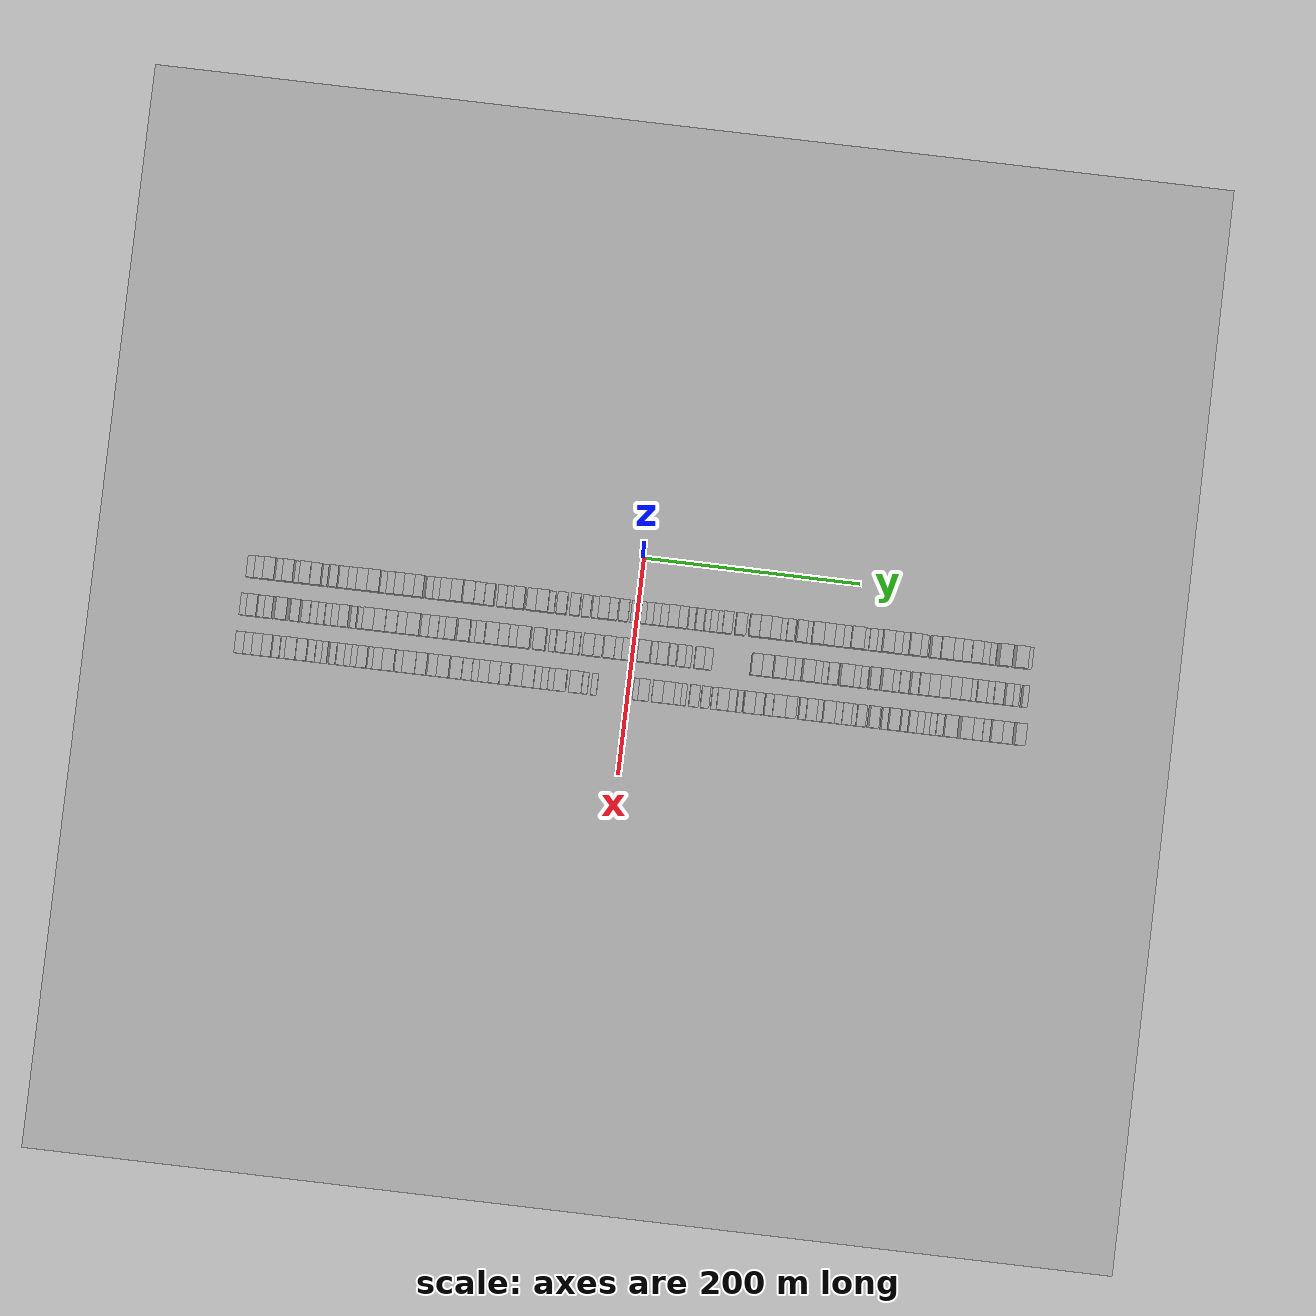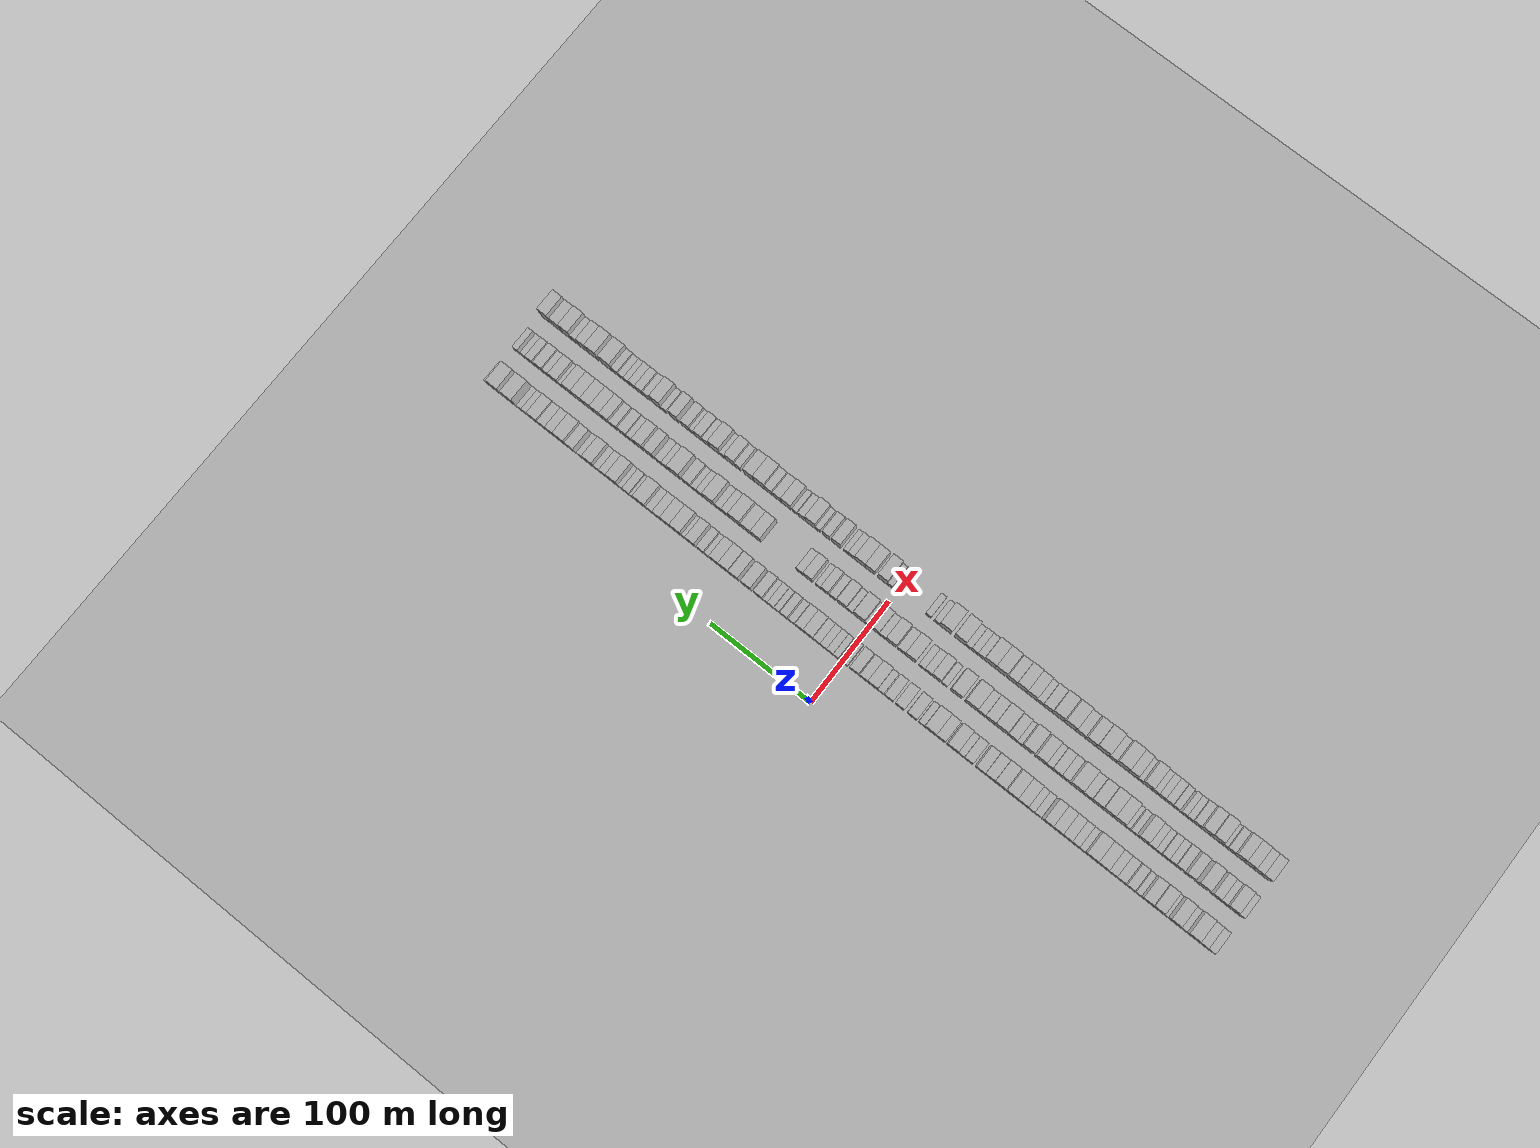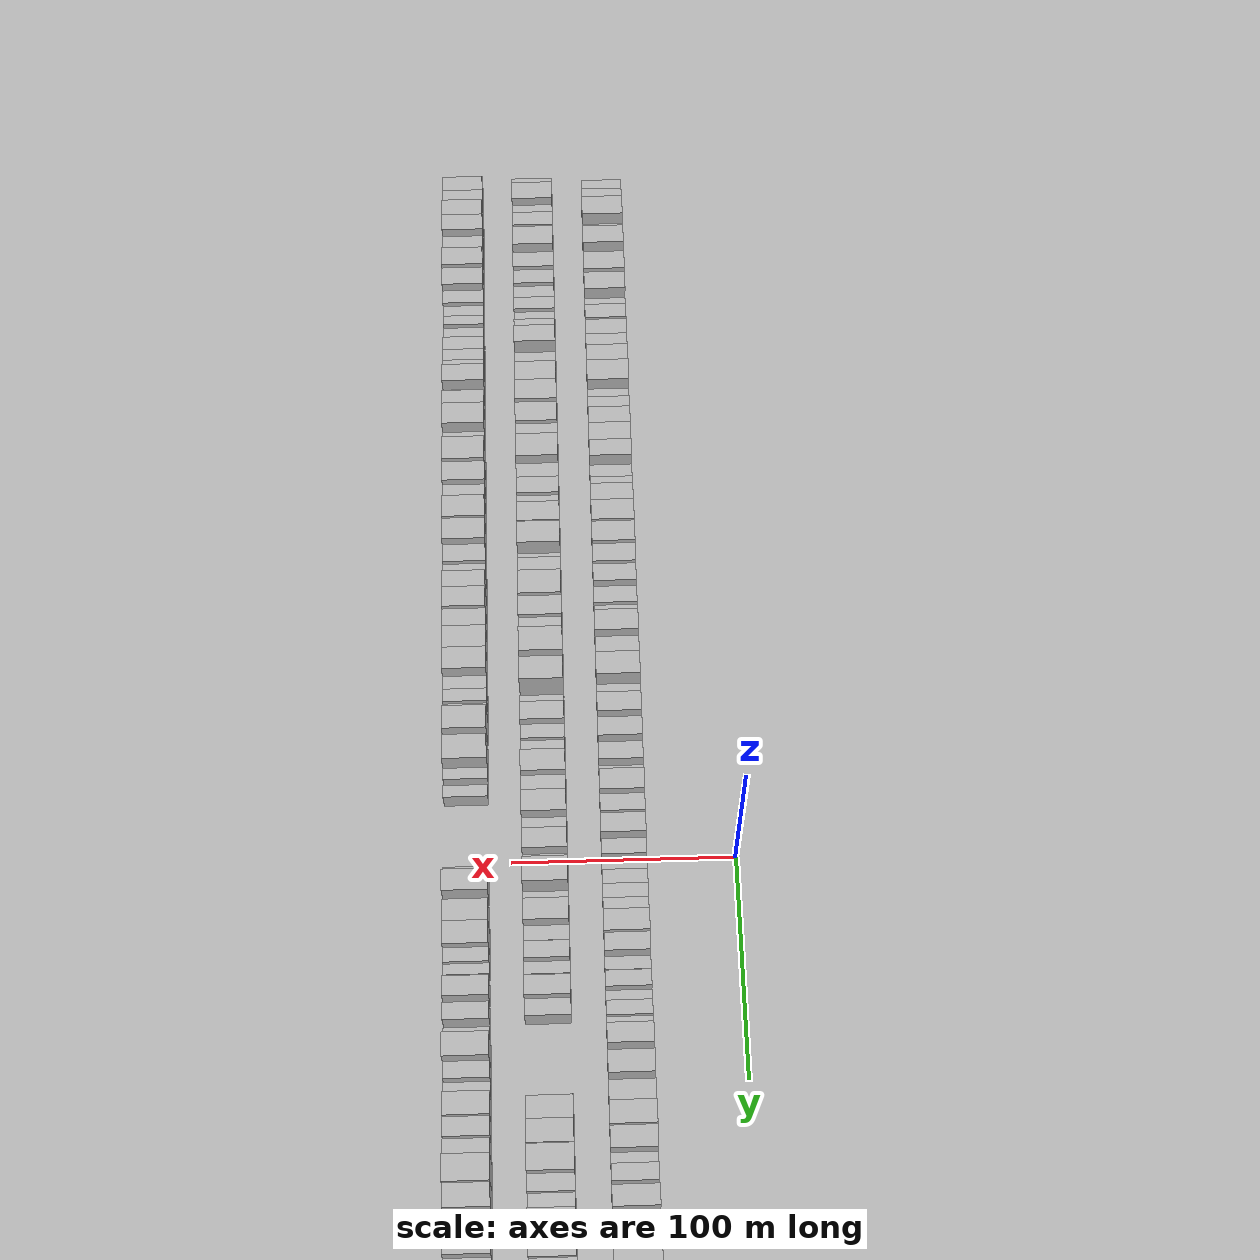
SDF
<?xml version="1.0" encoding="utf-8"?>

<sdf version="1.6">

   <world name="default">

      <gui fullscreen="0">

         <camera name="user_camera">

            <pose>-15 0 4.57585 0 0 0</pose>

            <view_controller>orbit</view_controller>

         </camera>

      </gui>

      <scene>

         <sky>

           <clouds>

             <speed>12</speed>

           </clouds>

         </sky>

         <ambient>0.4 0.4 0.4 1</ambient>

         <background>0.7 0.7 0.7 1</background>

         <shadows>1</shadows>

      </scene>

      <gravity>0 0 -9.8066</gravity>

      <magnetic_field>6e-06 2.3e-05 -4.2e-05</magnetic_field>

      <physics default="0" name="default_physics" type="ode">

         <ode>

            <solver>

               <type>quick</type>

               <iters>10</iters>

               <sor>1.0</sor>

               <use_dynamic_moi_rescaling>0</use_dynamic_moi_rescaling>

            </solver>

            <constraints>

               <cfm>0</cfm>

               <erp>0.2</erp>

               <contact_max_correcting_vel>100</contact_max_correcting_vel>

               <contact_surface_layer>0.001</contact_surface_layer>

            </constraints>

         </ode>

         <max_step_size>0.004</max_step_size>

         <real_time_factor>1</real_time_factor>

         <real_time_update_rate>250</real_time_update_rate>

      </physics>

      <light name="sun" type="directional">

         <cast_shadows>1</cast_shadows>

         <pose>0 0 10 0 0 0</pose>

         <diffuse>0.8 0.8 0.8 1</diffuse>

         <specular>0.2 0.2 0.2 1</specular>

         <attenuation>

            <range>1000</range>

            <constant>0.9</constant>

            <linear>0.01</linear>

            <quadratic>0.001</quadratic>

         </attenuation>

         <direction>-0.5 0.1 -0.9</direction>

      </light>

      <include>

         <name>ground_plane_1</name>

         <uri>model://HANNAS_ground_plane</uri>

         <pose>0 0 0  0 0 0</pose>

      </include>

      <include>

         <name>ground_plane_2</name>

         <uri>model://HANNAS_ground_plane</uri>

         <pose>100 0 0  0 0 0</pose>

      </include>

      <model name="building_1">

         <static>1</static>

         <pose frame="">50.0000 -354.3258 0 0.000000 0.000000 0.000000</pose>

         <link name="link">

            <pose frame="">0 0 7.50 0 0 0</pose>

            <collision name="collision">

               <geometry>

                  <box>

                     <size>20.0000 7.3484 15.0000</size>

                  </box>

               </geometry>

               <max_contacts>10</max_contacts>

               <surface>

                  <contact>

                     <ode/>

                  </contact>

                  <bounce/>

                  <friction>

                     <torsional>

                        <ode/>

                     </torsional>

                     <ode/>

                  </friction>

               </surface>

            </collision>

            <visual name="visual">

               <cast_shadows>0</cast_shadows>

               <geometry>

                  <box>

                     <size>20.0000 7.3484 15.0000</size>

                  </box>

               </geometry>

               <material>

                  <script>

                     <uri>model://HANNAS_wall/materials/scripts</uri>

                     <uri>model://HANNAS_wall/materials/textures</uri>

                     <name>vrc/HANNAS_wall</name>

                  </script>

               </material>

            </visual>

            <self_collide>0</self_collide>

            <enable_wind>0</enable_wind>

            <kinematic>0</kinematic>

         </link>

      </model>

      <model name="building_2">

         <static>1</static>

         <pose frame="">50.0000 -346.2138 0 0.000000 0.000000 0.000000</pose>

         <link name="link">

            <pose frame="">0 0 9.00 0 0 0</pose>

            <collision name="collision">

               <geometry>

                  <box>

                     <size>20.0000 8.8757 18.0000</size>

                  </box>

               </geometry>

               <max_contacts>10</max_contacts>

               <surface>

                  <contact>

                     <ode/>

                  </contact>

                  <bounce/>

                  <friction>

                     <torsional>

                        <ode/>

                     </torsional>

                     <ode/>

                  </friction>

               </surface>

            </collision>

            <visual name="visual">

               <cast_shadows>0</cast_shadows>

               <geometry>

                  <box>

                     <size>20.0000 8.8757 18.0000</size>

                  </box>

               </geometry>

               <material>

                  <script>

                     <uri>model://HANNAS_wall/materials/scripts</uri>

                     <uri>model://HANNAS_wall/materials/textures</uri>

                     <name>vrc/HANNAS_wall</name>

                  </script>

               </material>

            </visual>

            <self_collide>0</self_collide>

            <enable_wind>0</enable_wind>

            <kinematic>0</kinematic>

         </link>

      </model>

      <model name="building_3">

         <static>1</static>

         <pose frame="">50.0000 -336.5271 0 0.000000 0.000000 0.000000</pose>

         <link name="link">

            <pose frame="">0 0 12.00 0 0 0</pose>

            <collision name="collision">

               <geometry>

                  <box>

                     <size>20.0000 10.4978 24.0000</size>

                  </box>

               </geometry>

               <max_contacts>10</max_contacts>

               <surface>

                  <contact>

                     <ode/>

                  </contact>

                  <bounce/>

                  <friction>

                     <torsional>

                        <ode/>

                     </torsional>

                     <ode/>

                  </friction>

               </surface>

            </collision>

            <visual name="visual">

               <cast_shadows>0</cast_shadows>

               <geometry>

                  <box>

                     <size>20.0000 10.4978 24.0000</size>

                  </box>

               </geometry>

               <material>

                  <script>

                     <uri>model://HANNAS_wall/materials/scripts</uri>

                     <uri>model://HANNAS_wall/materials/textures</uri>

                     <name>vrc/HANNAS_wall</name>

                  </script>

               </material>

            </visual>

            <self_collide>0</self_collide>

            <enable_wind>0</enable_wind>

            <kinematic>0</kinematic>

         </link>

      </model>

      <model name="building_4">

         <static>1</static>

         <pose frame="">50.0000 -327.7138 0 0.000000 0.000000 0.000000</pose>

         <link name="link">

            <pose frame="">0 0 7.50 0 0 0</pose>

            <collision name="collision">

               <geometry>

                  <box>

                     <size>20.0000 7.1287 15.0000</size>

                  </box>

               </geometry>

               <max_contacts>10</max_contacts>

               <surface>

                  <contact>

                     <ode/>

                  </contact>

                  <bounce/>

                  <friction>

                     <torsional>

                        <ode/>

                     </torsional>

                     <ode/>

                  </friction>

               </surface>

            </collision>

            <visual name="visual">

               <cast_shadows>0</cast_shadows>

               <geometry>

                  <box>

                     <size>20.0000 7.1287 15.0000</size>

                  </box>

               </geometry>

               <material>

                  <script>

                     <uri>model://HANNAS_wall/materials/scripts</uri>

                     <uri>model://HANNAS_wall/materials/textures</uri>

                     <name>vrc/HANNAS_wall</name>

                  </script>

               </material>

            </visual>

            <self_collide>0</self_collide>

            <enable_wind>0</enable_wind>

            <kinematic>0</kinematic>

         </link>

      </model>

      <model name="building_5">

         <static>1</static>

         <pose frame="">50.0000 -319.2572 0 0.000000 0.000000 0.000000</pose>

         <link name="link">

            <pose frame="">0 0 12.00 0 0 0</pose>

            <collision name="collision">

               <geometry>

                  <box>

                     <size>20.0000 9.7846 24.0000</size>

                  </box>

               </geometry>

               <max_contacts>10</max_contacts>

               <surface>

                  <contact>

                     <ode/>

                  </contact>

                  <bounce/>

                  <friction>

                     <torsional>

                        <ode/>

                     </torsional>

                     <ode/>

                  </friction>

               </surface>

            </collision>

            <visual name="visual">

               <cast_shadows>0</cast_shadows>

               <geometry>

                  <box>

                     <size>20.0000 9.7846 24.0000</size>

                  </box>

               </geometry>

               <material>

                  <script>

                     <uri>model://HANNAS_wall/materials/scripts</uri>

                     <uri>model://HANNAS_wall/materials/textures</uri>

                     <name>vrc/HANNAS_wall</name>

                  </script>

               </material>

            </visual>

            <self_collide>0</self_collide>

            <enable_wind>0</enable_wind>

            <kinematic>0</kinematic>

         </link>

      </model>

      <model name="building_6">

         <static>1</static>

         <pose frame="">50.0000 -311.5698 0 0.000000 0.000000 0.000000</pose>

         <link name="link">

            <pose frame="">0 0 6.00 0 0 0</pose>

            <collision name="collision">

               <geometry>

                  <box>

                     <size>20.0000 5.5903 12.0000</size>

                  </box>

               </geometry>

               <max_contacts>10</max_contacts>

               <surface>

                  <contact>

                     <ode/>

                  </contact>

                  <bounce/>

                  <friction>

                     <torsional>

                        <ode/>

                     </torsional>

                     <ode/>

                  </friction>

               </surface>

            </collision>

            <visual name="visual">

               <cast_shadows>0</cast_shadows>

               <geometry>

                  <box>

                     <size>20.0000 5.5903 12.0000</size>

                  </box>

               </geometry>

               <material>

                  <script>

                     <uri>model://HANNAS_wall/materials/scripts</uri>

                     <uri>model://HANNAS_wall/materials/textures</uri>

                     <name>vrc/HANNAS_wall</name>

                  </script>

               </material>

            </visual>

            <self_collide>0</self_collide>

            <enable_wind>0</enable_wind>

            <kinematic>0</kinematic>

         </link>

      </model>

      <model name="building_7">

         <static>1</static>

         <pose frame="">50.0000 -303.7993 0 0.000000 0.000000 0.000000</pose>

         <link name="link">

            <pose frame="">0 0 12.00 0 0 0</pose>

            <collision name="collision">

               <geometry>

                  <box>

                     <size>20.0000 9.9505 24.0000</size>

                  </box>

               </geometry>

               <max_contacts>10</max_contacts>

               <surface>

                  <contact>

                     <ode/>

                  </contact>

                  <bounce/>

                  <friction>

                     <torsional>

                        <ode/>

                     </torsional>

                     <ode/>

                  </friction>

               </surface>

            </collision>

            <visual name="visual">

               <cast_shadows>0</cast_shadows>

               <geometry>

                  <box>

                     <size>20.0000 9.9505 24.0000</size>

                  </box>

               </geometry>

               <material>

                  <script>

                     <uri>model://HANNAS_wall/materials/scripts</uri>

                     <uri>model://HANNAS_wall/materials/textures</uri>

                     <name>vrc/HANNAS_wall</name>

                  </script>

               </material>

            </visual>

            <self_collide>0</self_collide>

            <enable_wind>0</enable_wind>

            <kinematic>0</kinematic>

         </link>

      </model>

      <model name="building_8">

         <static>1</static>

         <pose frame="">50.0000 -294.0024 0 0.000000 0.000000 0.000000</pose>

         <link name="link">

            <pose frame="">0 0 10.50 0 0 0</pose>

            <collision name="collision">

               <geometry>

                  <box>

                     <size>20.0000 9.6435 21.0000</size>

                  </box>

               </geometry>

               <max_contacts>10</max_contacts>

               <surface>

                  <contact>

                     <ode/>

                  </contact>

                  <bounce/>

                  <friction>

                     <torsional>

                        <ode/>

                     </torsional>

                     <ode/>

                  </friction>

               </surface>

            </collision>

            <visual name="visual">

               <cast_shadows>0</cast_shadows>

               <geometry>

                  <box>

                     <size>20.0000 9.6435 21.0000</size>

                  </box>

               </geometry>

               <material>

                  <script>

                     <uri>model://HANNAS_wall/materials/scripts</uri>

                     <uri>model://HANNAS_wall/materials/textures</uri>

                     <name>vrc/HANNAS_wall</name>

                  </script>

               </material>

            </visual>

            <self_collide>0</self_collide>

            <enable_wind>0</enable_wind>

            <kinematic>0</kinematic>

         </link>

      </model>

      <model name="building_9">

         <static>1</static>

         <pose frame="">50.0000 -286.5787 0 0.000000 0.000000 0.000000</pose>

         <link name="link">

            <pose frame="">0 0 6.00 0 0 0</pose>

            <collision name="collision">

               <geometry>

                  <box>

                     <size>20.0000 5.2039 12.0000</size>

                  </box>

               </geometry>

               <max_contacts>10</max_contacts>

               <surface>

                  <contact>

                     <ode/>

                  </contact>

                  <bounce/>

                  <friction>

                     <torsional>

                        <ode/>

                     </torsional>

                     <ode/>

                  </friction>

               </surface>

            </collision>

            <visual name="visual">

               <cast_shadows>0</cast_shadows>

               <geometry>

                  <box>

                     <size>20.0000 5.2039 12.0000</size>

                  </box>

               </geometry>

               <material>

                  <script>

                     <uri>model://HANNAS_wall/materials/scripts</uri>

                     <uri>model://HANNAS_wall/materials/textures</uri>

                     <name>vrc/HANNAS_wall</name>

                  </script>

               </material>

            </visual>

            <self_collide>0</self_collide>

            <enable_wind>0</enable_wind>

            <kinematic>0</kinematic>

         </link>

      </model>

      <model name="building_10">

         <static>1</static>

         <pose frame="">50.0000 -278.1410 0 0.000000 0.000000 0.000000</pose>

         <link name="link">

            <pose frame="">0 0 9.00 0 0 0</pose>

            <collision name="collision">

               <geometry>

                  <box>

                     <size>20.0000 7.6714 18.0000</size>

                  </box>

               </geometry>

               <max_contacts>10</max_contacts>

               <surface>

                  <contact>

                     <ode/>

                  </contact>

                  <bounce/>

                  <friction>

                     <torsional>

                        <ode/>

                     </torsional>

                     <ode/>

                  </friction>

               </surface>

            </collision>

            <visual name="visual">

               <cast_shadows>0</cast_shadows>

               <geometry>

                  <box>

                     <size>20.0000 7.6714 18.0000</size>

                  </box>

               </geometry>

               <material>

                  <script>

                     <uri>model://HANNAS_wall/materials/scripts</uri>

                     <uri>model://HANNAS_wall/materials/textures</uri>

                     <name>vrc/HANNAS_wall</name>

                  </script>

               </material>

            </visual>

            <self_collide>0</self_collide>

            <enable_wind>0</enable_wind>

            <kinematic>0</kinematic>

         </link>

      </model>

      <model name="building_11">

         <static>1</static>

         <pose frame="">50.0000 -269.1408 0 0.000000 0.000000 0.000000</pose>

         <link name="link">

            <pose frame="">0 0 9.00 0 0 0</pose>

            <collision name="collision">

               <geometry>

                  <box>

                     <size>20.0000 8.3290 18.0000</size>

                  </box>

               </geometry>

               <max_contacts>10</max_contacts>

               <surface>

                  <contact>

                     <ode/>

                  </contact>

                  <bounce/>

                  <friction>

                     <torsional>

                        <ode/>

                     </torsional>

                     <ode/>

                  </friction>

               </surface>

            </collision>

            <visual name="visual">

               <cast_shadows>0</cast_shadows>

               <geometry>

                  <box>

                     <size>20.0000 8.3290 18.0000</size>

                  </box>

               </geometry>

               <material>

                  <script>

                     <uri>model://HANNAS_wall/materials/scripts</uri>

                     <uri>model://HANNAS_wall/materials/textures</uri>

                     <name>vrc/HANNAS_wall</name>

                  </script>

               </material>

            </visual>

            <self_collide>0</self_collide>

            <enable_wind>0</enable_wind>

            <kinematic>0</kinematic>

         </link>

      </model>

      <model name="building_12">

         <static>1</static>

         <pose frame="">50.0000 -260.9460 0 0.000000 0.000000 0.000000</pose>

         <link name="link">

            <pose frame="">0 0 9.00 0 0 0</pose>

            <collision name="collision">

               <geometry>

                  <box>

                     <size>20.0000 8.0607 18.0000</size>

                  </box>

               </geometry>

               <max_contacts>10</max_contacts>

               <surface>

                  <contact>

                     <ode/>

                  </contact>

                  <bounce/>

                  <friction>

                     <torsional>

                        <ode/>

                     </torsional>

                     <ode/>

                  </friction>

               </surface>

            </collision>

            <visual name="visual">

               <cast_shadows>0</cast_shadows>

               <geometry>

                  <box>

                     <size>20.0000 8.0607 18.0000</size>

                  </box>

               </geometry>

               <material>

                  <script>

                     <uri>model://HANNAS_wall/materials/scripts</uri>

                     <uri>model://HANNAS_wall/materials/textures</uri>

                     <name>vrc/HANNAS_wall</name>

                  </script>

               </material>

            </visual>

            <self_collide>0</self_collide>

            <enable_wind>0</enable_wind>

            <kinematic>0</kinematic>

         </link>

      </model>

      <model name="building_13">

         <static>1</static>

         <pose frame="">50.0000 -251.7134 0 0.000000 0.000000 0.000000</pose>

         <link name="link">

            <pose frame="">0 0 10.50 0 0 0</pose>

            <collision name="collision">

               <geometry>

                  <box>

                     <size>20.0000 10.4045 21.0000</size>

                  </box>

               </geometry>

               <max_contacts>10</max_contacts>

               <surface>

                  <contact>

                     <ode/>

                  </contact>

                  <bounce/>

                  <friction>

                     <torsional>

                        <ode/>

                     </torsional>

                     <ode/>

                  </friction>

               </surface>

            </collision>

            <visual name="visual">

               <cast_shadows>0</cast_shadows>

               <geometry>

                  <box>

                     <size>20.0000 10.4045 21.0000</size>

                  </box>

               </geometry>

               <material>

                  <script>

                     <uri>model://HANNAS_wall/materials/scripts</uri>

                     <uri>model://HANNAS_wall/materials/textures</uri>

                     <name>vrc/HANNAS_wall</name>

                  </script>

               </material>

            </visual>

            <self_collide>0</self_collide>

            <enable_wind>0</enable_wind>

            <kinematic>0</kinematic>

         </link>

      </model>

      <model name="building_14">

         <static>1</static>

         <pose frame="">50.0000 -240.9820 0 0.000000 0.000000 0.000000</pose>

         <link name="link">

            <pose frame="">0 0 12.00 0 0 0</pose>

            <collision name="collision">

               <geometry>

                  <box>

                     <size>20.0000 11.0583 24.0000</size>

                  </box>

               </geometry>

               <max_contacts>10</max_contacts>

               <surface>

                  <contact>

                     <ode/>

                  </contact>

                  <bounce/>

                  <friction>

                     <torsional>

                        <ode/>

                     </torsional>

                     <ode/>

                  </friction>

               </surface>

            </collision>

            <visual name="visual">

               <cast_shadows>0</cast_shadows>

               <geometry>

                  <box>

                     <size>20.0000 11.0583 24.0000</size>

                  </box>

               </geometry>

               <material>

                  <script>

                     <uri>model://HANNAS_wall/materials/scripts</uri>

                     <uri>model://HANNAS_wall/materials/textures</uri>

                     <name>vrc/HANNAS_wall</name>

                  </script>

               </material>

            </visual>

            <self_collide>0</self_collide>

            <enable_wind>0</enable_wind>

            <kinematic>0</kinematic>

         </link>

      </model>

      <model name="building_15">

         <static>1</static>

         <pose frame="">50.0000 -232.4243 0 0.000000 0.000000 0.000000</pose>

         <link name="link">

            <pose frame="">0 0 7.50 0 0 0</pose>

            <collision name="collision">

               <geometry>

                  <box>

                     <size>20.0000 6.0572 15.0000</size>

                  </box>

               </geometry>

               <max_contacts>10</max_contacts>

               <surface>

                  <contact>

                     <ode/>

                  </contact>

                  <bounce/>

                  <friction>

                     <torsional>

                        <ode/>

                     </torsional>

                     <ode/>

                  </friction>

               </surface>

            </collision>

            <visual name="visual">

               <cast_shadows>0</cast_shadows>

               <geometry>

                  <box>

                     <size>20.0000 6.0572 15.0000</size>

                  </box>

               </geometry>

               <material>

                  <script>

                     <uri>model://HANNAS_wall/materials/scripts</uri>

                     <uri>model://HANNAS_wall/materials/textures</uri>

                     <name>vrc/HANNAS_wall</name>

                  </script>

               </material>

            </visual>

            <self_collide>0</self_collide>

            <enable_wind>0</enable_wind>

            <kinematic>0</kinematic>

         </link>

      </model>

      <model name="building_16">

         <static>1</static>

         <pose frame="">50.0000 -225.7133 0 0.000000 0.000000 0.000000</pose>

         <link name="link">

            <pose frame="">0 0 9.00 0 0 0</pose>

            <collision name="collision">

               <geometry>

                  <box>

                     <size>20.0000 7.3649 18.0000</size>

                  </box>

               </geometry>

               <max_contacts>10</max_contacts>

               <surface>

                  <contact>

                     <ode/>

                  </contact>

                  <bounce/>

                  <friction>

                     <torsional>

                        <ode/>

                     </torsional>

                     <ode/>

                  </friction>

               </surface>

            </collision>

            <visual name="visual">

               <cast_shadows>0</cast_shadows>

               <geometry>

                  <box>

                     <size>20.0000 7.3649 18.0000</size>

                  </box>

               </geometry>

               <material>

                  <script>

                     <uri>model://HANNAS_wall/materials/scripts</uri>

                     <uri>model://HANNAS_wall/materials/textures</uri>

                     <name>vrc/HANNAS_wall</name>

                  </script>

               </material>

            </visual>

            <self_collide>0</self_collide>

            <enable_wind>0</enable_wind>

            <kinematic>0</kinematic>

         </link>

      </model>

      <model name="building_17">

         <static>1</static>

         <pose frame="">50.0000 -217.7505 0 0.000000 0.000000 0.000000</pose>

         <link name="link">

            <pose frame="">0 0 10.50 0 0 0</pose>

            <collision name="collision">

               <geometry>

                  <box>

                     <size>20.0000 8.5607 21.0000</size>

                  </box>

               </geometry>

               <max_contacts>10</max_contacts>

               <surface>

                  <contact>

                     <ode/>

                  </contact>

                  <bounce/>

                  <friction>

                     <torsional>

                        <ode/>

                     </torsional>

                     <ode/>

                  </friction>

               </surface>

            </collision>

            <visual name="visual">

               <cast_shadows>0</cast_shadows>

               <geometry>

                  <box>

                     <size>20.0000 8.5607 21.0000</size>

                  </box>

               </geometry>

               <material>

                  <script>

                     <uri>model://HANNAS_wall/materials/scripts</uri>

                     <uri>model://HANNAS_wall/materials/textures</uri>

                     <name>vrc/HANNAS_wall</name>

                  </script>

               </material>

            </visual>

            <self_collide>0</self_collide>

            <enable_wind>0</enable_wind>

            <kinematic>0</kinematic>

         </link>

      </model>

      <model name="building_18">

         <static>1</static>

         <pose frame="">50.0000 -208.8012 0 0.000000 0.000000 0.000000</pose>

         <link name="link">

            <pose frame="">0 0 10.50 0 0 0</pose>

            <collision name="collision">

               <geometry>

                  <box>

                     <size>20.0000 9.3379 21.0000</size>

                  </box>

               </geometry>

               <max_contacts>10</max_contacts>

               <surface>

                  <contact>

                     <ode/>

                  </contact>

                  <bounce/>

                  <friction>

                     <torsional>

                        <ode/>

                     </torsional>

                     <ode/>

                  </friction>

               </surface>

            </collision>

            <visual name="visual">

               <cast_shadows>0</cast_shadows>

               <geometry>

                  <box>

                     <size>20.0000 9.3379 21.0000</size>

                  </box>

               </geometry>

               <material>

                  <script>

                     <uri>model://HANNAS_wall/materials/scripts</uri>

                     <uri>model://HANNAS_wall/materials/textures</uri>

                     <name>vrc/HANNAS_wall</name>

                  </script>

               </material>

            </visual>

            <self_collide>0</self_collide>

            <enable_wind>0</enable_wind>

            <kinematic>0</kinematic>

         </link>

      </model>

      <model name="building_19">

         <static>1</static>

         <pose frame="">50.0000 -199.8368 0 0.000000 0.000000 0.000000</pose>

         <link name="link">

            <pose frame="">0 0 10.50 0 0 0</pose>

            <collision name="collision">

               <geometry>

                  <box>

                     <size>20.0000 8.5909 21.0000</size>

                  </box>

               </geometry>

               <max_contacts>10</max_contacts>

               <surface>

                  <contact>

                     <ode/>

                  </contact>

                  <bounce/>

                  <friction>

                     <torsional>

                        <ode/>

                     </torsional>

                     <ode/>

                  </friction>

               </surface>

            </collision>

            <visual name="visual">

               <cast_shadows>0</cast_shadows>

               <geometry>

                  <box>

                     <size>20.0000 8.5909 21.0000</size>

                  </box>

               </geometry>

               <material>

                  <script>

                     <uri>model://HANNAS_wall/materials/scripts</uri>

                     <uri>model://HANNAS_wall/materials/textures</uri>

                     <name>vrc/HANNAS_wall</name>

                  </script>

               </material>

            </visual>

            <self_collide>0</self_collide>

            <enable_wind>0</enable_wind>

            <kinematic>0</kinematic>

         </link>

      </model>

      <model name="building_20">

         <static>1</static>

         <pose frame="">50.0000 -190.3306 0 0.000000 0.000000 0.000000</pose>

         <link name="link">

            <pose frame="">0 0 7.50 0 0 0</pose>

            <collision name="collision">

               <geometry>

                  <box>

                     <size>20.0000 6.4213 15.0000</size>

                  </box>

               </geometry>

               <max_contacts>10</max_contacts>

               <surface>

                  <contact>

                     <ode/>

                  </contact>

                  <bounce/>

                  <friction>

                     <torsional>

                        <ode/>

                     </torsional>

                     <ode/>

                  </friction>

               </surface>

            </collision>

            <visual name="visual">

               <cast_shadows>0</cast_shadows>

               <geometry>

                  <box>

                     <size>20.0000 6.4213 15.0000</size>

                  </box>

               </geometry>

               <material>

                  <script>

                     <uri>model://HANNAS_wall/materials/scripts</uri>

                     <uri>model://HANNAS_wall/materials/textures</uri>

                     <name>vrc/HANNAS_wall</name>

                  </script>

               </material>

            </visual>

            <self_collide>0</self_collide>

            <enable_wind>0</enable_wind>

            <kinematic>0</kinematic>

         </link>

      </model>

      <model name="building_21">

         <static>1</static>

         <pose frame="">50.0000 -183.7870 0 0.000000 0.000000 0.000000</pose>

         <link name="link">

            <pose frame="">0 0 7.50 0 0 0</pose>

            <collision name="collision">

               <geometry>

                  <box>

                     <size>20.0000 6.6659 15.0000</size>

                  </box>

               </geometry>

               <max_contacts>10</max_contacts>

               <surface>

                  <contact>

                     <ode/>

                  </contact>

                  <bounce/>

                  <friction>

                     <torsional>

                        <ode/>

                     </torsional>

                     <ode/>

                  </friction>

               </surface>

            </collision>

            <visual name="visual">

               <cast_shadows>0</cast_shadows>

               <geometry>

                  <box>

                     <size>20.0000 6.6659 15.0000</size>

                  </box>

               </geometry>

               <material>

                  <script>

                     <uri>model://HANNAS_wall/materials/scripts</uri>

                     <uri>model://HANNAS_wall/materials/textures</uri>

                     <name>vrc/HANNAS_wall</name>

                  </script>

               </material>

            </visual>

            <self_collide>0</self_collide>

            <enable_wind>0</enable_wind>

            <kinematic>0</kinematic>

         </link>

      </model>

      <model name="building_22">

         <static>1</static>

         <pose frame="">50.0000 -175.3186 0 0.000000 0.000000 0.000000</pose>

         <link name="link">

            <pose frame="">0 0 10.50 0 0 0</pose>

            <collision name="collision">

               <geometry>

                  <box>

                     <size>20.0000 10.2709 21.0000</size>

                  </box>

               </geometry>

               <max_contacts>10</max_contacts>

               <surface>

                  <contact>

                     <ode/>

                  </contact>

                  <bounce/>

                  <friction>

                     <torsional>

                        <ode/>

                     </torsional>

                     <ode/>

                  </friction>

               </surface>

            </collision>

            <visual name="visual">

               <cast_shadows>0</cast_shadows>

               <geometry>

                  <box>

                     <size>20.0000 10.2709 21.0000</size>

                  </box>

               </geometry>

               <material>

                  <script>

                     <uri>model://HANNAS_wall/materials/scripts</uri>

                     <uri>model://HANNAS_wall/materials/textures</uri>

                     <name>vrc/HANNAS_wall</name>

                  </script>

               </material>

            </visual>

            <self_collide>0</self_collide>

            <enable_wind>0</enable_wind>

            <kinematic>0</kinematic>

         </link>

      </model>

      <model name="building_23">

         <static>1</static>

         <pose frame="">50.0000 -164.9860 0 0.000000 0.000000 0.000000</pose>

         <link name="link">

            <pose frame="">0 0 12.00 0 0 0</pose>

            <collision name="collision">

               <geometry>

                  <box>

                     <size>20.0000 10.3942 24.0000</size>

                  </box>

               </geometry>

               <max_contacts>10</max_contacts>

               <surface>

                  <contact>

                     <ode/>

                  </contact>

                  <bounce/>

                  <friction>

                     <torsional>

                        <ode/>

                     </torsional>

                     <ode/>

                  </friction>

               </surface>

            </collision>

            <visual name="visual">

               <cast_shadows>0</cast_shadows>

               <geometry>

                  <box>

                     <size>20.0000 10.3942 24.0000</size>

                  </box>

               </geometry>

               <material>

                  <script>

                     <uri>model://HANNAS_wall/materials/scripts</uri>

                     <uri>model://HANNAS_wall/materials/textures</uri>

                     <name>vrc/HANNAS_wall</name>

                  </script>

               </material>

            </visual>

            <self_collide>0</self_collide>

            <enable_wind>0</enable_wind>

            <kinematic>0</kinematic>

         </link>

      </model>

      <model name="building_24">

         <static>1</static>

         <pose frame="">50.0000 -153.6538 0 0.000000 0.000000 0.000000</pose>

         <link name="link">

            <pose frame="">0 0 12.00 0 0 0</pose>

            <collision name="collision">

               <geometry>

                  <box>

                     <size>20.0000 10.2702 24.0000</size>

                  </box>

               </geometry>

               <max_contacts>10</max_contacts>

               <surface>

                  <contact>

                     <ode/>

                  </contact>

                  <bounce/>

                  <friction>

                     <torsional>

                        <ode/>

                     </torsional>

                     <ode/>

                  </friction>

               </surface>

            </collision>

            <visual name="visual">

               <cast_shadows>0</cast_shadows>

               <geometry>

                  <box>

                     <size>20.0000 10.2702 24.0000</size>

                  </box>

               </geometry>

               <material>

                  <script>

                     <uri>model://HANNAS_wall/materials/scripts</uri>

                     <uri>model://HANNAS_wall/materials/textures</uri>

                     <name>vrc/HANNAS_wall</name>

                  </script>

               </material>

            </visual>

            <self_collide>0</self_collide>

            <enable_wind>0</enable_wind>

            <kinematic>0</kinematic>

         </link>

      </model>

      <model name="building_25">

         <static>1</static>

         <pose frame="">50.0000 -143.9821 0 0.000000 0.000000 0.000000</pose>

         <link name="link">

            <pose frame="">0 0 10.50 0 0 0</pose>

            <collision name="collision">

               <geometry>

                  <box>

                     <size>20.0000 9.0734 21.0000</size>

                  </box>

               </geometry>

               <max_contacts>10</max_contacts>

               <surface>

                  <contact>

                     <ode/>

                  </contact>

                  <bounce/>

                  <friction>

                     <torsional>

                        <ode/>

                     </torsional>

                     <ode/>

                  </friction>

               </surface>

            </collision>

            <visual name="visual">

               <cast_shadows>0</cast_shadows>

               <geometry>

                  <box>

                     <size>20.0000 9.0734 21.0000</size>

                  </box>

               </geometry>

               <material>

                  <script>

                     <uri>model://HANNAS_wall/materials/scripts</uri>

                     <uri>model://HANNAS_wall/materials/textures</uri>

                     <name>vrc/HANNAS_wall</name>

                  </script>

               </material>

            </visual>

            <self_collide>0</self_collide>

            <enable_wind>0</enable_wind>

            <kinematic>0</kinematic>

         </link>

      </model>

      <model name="building_26">

         <static>1</static>

         <pose frame="">50.0000 -135.1392 0 0.000000 0.000000 0.000000</pose>

         <link name="link">

            <pose frame="">0 0 9.00 0 0 0</pose>

            <collision name="collision">

               <geometry>

                  <box>

                     <size>20.0000 8.6123 18.0000</size>

                  </box>

               </geometry>

               <max_contacts>10</max_contacts>

               <surface>

                  <contact>

                     <ode/>

                  </contact>

                  <bounce/>

                  <friction>

                     <torsional>

                        <ode/>

                     </torsional>

                     <ode/>

                  </friction>

               </surface>

            </collision>

            <visual name="visual">

               <cast_shadows>0</cast_shadows>

               <geometry>

                  <box>

                     <size>20.0000 8.6123 18.0000</size>

                  </box>

               </geometry>

               <material>

                  <script>

                     <uri>model://HANNAS_wall/materials/scripts</uri>

                     <uri>model://HANNAS_wall/materials/textures</uri>

                     <name>vrc/HANNAS_wall</name>

                  </script>

               </material>

            </visual>

            <self_collide>0</self_collide>

            <enable_wind>0</enable_wind>

            <kinematic>0</kinematic>

         </link>

      </model>

      <model name="building_27">

         <static>1</static>

         <pose frame="">50.0000 -123.6976 0 0.000000 0.000000 0.000000</pose>

         <link name="link">

            <pose frame="">0 0 9.00 0 0 0</pose>

            <collision name="collision">

               <geometry>

                  <box>

                     <size>20.0000 8.2710 18.0000</size>

                  </box>

               </geometry>

               <max_contacts>10</max_contacts>

               <surface>

                  <contact>

                     <ode/>

                  </contact>

                  <bounce/>

                  <friction>

                     <torsional>

                        <ode/>

                     </torsional>

                     <ode/>

                  </friction>

               </surface>

            </collision>

            <visual name="visual">

               <cast_shadows>0</cast_shadows>

               <geometry>

                  <box>

                     <size>20.0000 8.2710 18.0000</size>

                  </box>

               </geometry>

               <material>

                  <script>

                     <uri>model://HANNAS_wall/materials/scripts</uri>

                     <uri>model://HANNAS_wall/materials/textures</uri>

                     <name>vrc/HANNAS_wall</name>

                  </script>

               </material>

            </visual>

            <self_collide>0</self_collide>

            <enable_wind>0</enable_wind>

            <kinematic>0</kinematic>

         </link>

      </model>

      <model name="building_28">

         <static>1</static>

         <pose frame="">50.0000 -116.3931 0 0.000000 0.000000 0.000000</pose>

         <link name="link">

            <pose frame="">0 0 7.50 0 0 0</pose>

            <collision name="collision">

               <geometry>

                  <box>

                     <size>20.0000 6.3378 15.0000</size>

                  </box>

               </geometry>

               <max_contacts>10</max_contacts>

               <surface>

                  <contact>

                     <ode/>

                  </contact>

                  <bounce/>

                  <friction>

                     <torsional>

                        <ode/>

                     </torsional>

                     <ode/>

                  </friction>

               </surface>

            </collision>

            <visual name="visual">

               <cast_shadows>0</cast_shadows>

               <geometry>

                  <box>

                     <size>20.0000 6.3378 15.0000</size>

                  </box>

               </geometry>

               <material>

                  <script>

                     <uri>model://HANNAS_wall/materials/scripts</uri>

                     <uri>model://HANNAS_wall/materials/textures</uri>

                     <name>vrc/HANNAS_wall</name>

                  </script>

               </material>

            </visual>

            <self_collide>0</self_collide>

            <enable_wind>0</enable_wind>

            <kinematic>0</kinematic>

         </link>

      </model>

      <model name="building_29">

         <static>1</static>

         <pose frame="">50.0000 -108.0899 0 0.000000 0.000000 0.000000</pose>

         <link name="link">

            <pose frame="">0 0 12.00 0 0 0</pose>

            <collision name="collision">

               <geometry>

                  <box>

                     <size>20.0000 10.2686 24.0000</size>

                  </box>

               </geometry>

               <max_contacts>10</max_contacts>

               <surface>

                  <contact>

                     <ode/>

                  </contact>

                  <bounce/>

                  <friction>

                     <torsional>

                        <ode/>

                     </torsional>

                     <ode/>

                  </friction>

               </surface>

            </collision>

            <visual name="visual">

               <cast_shadows>0</cast_shadows>

               <geometry>

                  <box>

                     <size>20.0000 10.2686 24.0000</size>

                  </box>

               </geometry>

               <material>

                  <script>

                     <uri>model://HANNAS_wall/materials/scripts</uri>

                     <uri>model://HANNAS_wall/materials/textures</uri>

                     <name>vrc/HANNAS_wall</name>

                  </script>

               </material>

            </visual>

            <self_collide>0</self_collide>

            <enable_wind>0</enable_wind>

            <kinematic>0</kinematic>

         </link>

      </model>

      <model name="building_30">

         <static>1</static>

         <pose frame="">50.0000 -96.5013 0 0.000000 0.000000 0.000000</pose>

         <link name="link">

            <pose frame="">0 0 10.50 0 0 0</pose>

            <collision name="collision">

               <geometry>

                  <box>

                     <size>20.0000 8.9086 21.0000</size>

                  </box>

               </geometry>

               <max_contacts>10</max_contacts>

               <surface>

                  <contact>

                     <ode/>

                  </contact>

                  <bounce/>

                  <friction>

                     <torsional>

                        <ode/>

                     </torsional>

                     <ode/>

                  </friction>

               </surface>

            </collision>

            <visual name="visual">

               <cast_shadows>0</cast_shadows>

               <geometry>

                  <box>

                     <size>20.0000 8.9086 21.0000</size>

                  </box>

               </geometry>

               <material>

                  <script>

                     <uri>model://HANNAS_wall/materials/scripts</uri>

                     <uri>model://HANNAS_wall/materials/textures</uri>

                     <name>vrc/HANNAS_wall</name>

                  </script>

               </material>

            </visual>

            <self_collide>0</self_collide>

            <enable_wind>0</enable_wind>

            <kinematic>0</kinematic>

         </link>

      </model>

      <model name="building_31">

         <static>1</static>

         <pose frame="">50.0000 -86.5494 0 0.000000 0.000000 0.000000</pose>

         <link name="link">

            <pose frame="">0 0 12.00 0 0 0</pose>

            <collision name="collision">

               <geometry>

                  <box>

                     <size>20.0000 10.9953 24.0000</size>

                  </box>

               </geometry>

               <max_contacts>10</max_contacts>

               <surface>

                  <contact>

                     <ode/>

                  </contact>

                  <bounce/>

                  <friction>

                     <torsional>

                        <ode/>

                     </torsional>

                     <ode/>

                  </friction>

               </surface>

            </collision>

            <visual name="visual">

               <cast_shadows>0</cast_shadows>

               <geometry>

                  <box>

                     <size>20.0000 10.9953 24.0000</size>

                  </box>

               </geometry>

               <material>

                  <script>

                     <uri>model://HANNAS_wall/materials/scripts</uri>

                     <uri>model://HANNAS_wall/materials/textures</uri>

                     <name>vrc/HANNAS_wall</name>

                  </script>

               </material>

            </visual>

            <self_collide>0</self_collide>

            <enable_wind>0</enable_wind>

            <kinematic>0</kinematic>

         </link>

      </model>

      <model name="building_32">

         <static>1</static>

         <pose frame="">50.0000 -78.2267 0 0.000000 0.000000 0.000000</pose>

         <link name="link">

            <pose frame="">0 0 6.00 0 0 0</pose>

            <collision name="collision">

               <geometry>

                  <box>

                     <size>20.0000 5.6502 12.0000</size>

                  </box>

               </geometry>

               <max_contacts>10</max_contacts>

               <surface>

                  <contact>

                     <ode/>

                  </contact>

                  <bounce/>

                  <friction>

                     <torsional>

                        <ode/>

                     </torsional>

                     <ode/>

                  </friction>

               </surface>

            </collision>

            <visual name="visual">

               <cast_shadows>0</cast_shadows>

               <geometry>

                  <box>

                     <size>20.0000 5.6502 12.0000</size>

                  </box>

               </geometry>

               <material>

                  <script>

                     <uri>model://HANNAS_wall/materials/scripts</uri>

                     <uri>model://HANNAS_wall/materials/textures</uri>

                     <name>vrc/HANNAS_wall</name>

                  </script>

               </material>

            </visual>

            <self_collide>0</self_collide>

            <enable_wind>0</enable_wind>

            <kinematic>0</kinematic>

         </link>

      </model>

      <model name="building_33">

         <static>1</static>

         <pose frame="">50.0000 -68.7945 0 0.000000 0.000000 0.000000</pose>

         <link name="link">

            <pose frame="">0 0 10.50 0 0 0</pose>

            <collision name="collision">

               <geometry>

                  <box>

                     <size>20.0000 9.2141 21.0000</size>

                  </box>

               </geometry>

               <max_contacts>10</max_contacts>

               <surface>

                  <contact>

                     <ode/>

                  </contact>

                  <bounce/>

                  <friction>

                     <torsional>

                        <ode/>

                     </torsional>

                     <ode/>

                  </friction>

               </surface>

            </collision>

            <visual name="visual">

               <cast_shadows>0</cast_shadows>

               <geometry>

                  <box>

                     <size>20.0000 9.2141 21.0000</size>

                  </box>

               </geometry>

               <material>

                  <script>

                     <uri>model://HANNAS_wall/materials/scripts</uri>

                     <uri>model://HANNAS_wall/materials/textures</uri>

                     <name>vrc/HANNAS_wall</name>

                  </script>

               </material>

            </visual>

            <self_collide>0</self_collide>

            <enable_wind>0</enable_wind>

            <kinematic>0</kinematic>

         </link>

      </model>

      <model name="building_34">

         <static>1</static>

         <pose frame="">50.0000 -56.7587 0 0.000000 0.000000 0.000000</pose>

         <link name="link">

            <pose frame="">0 0 10.50 0 0 0</pose>

            <collision name="collision">

               <geometry>

                  <box>

                     <size>20.0000 8.8575 21.0000</size>

                  </box>

               </geometry>

               <max_contacts>10</max_contacts>

               <surface>

                  <contact>

                     <ode/>

                  </contact>

                  <bounce/>

                  <friction>

                     <torsional>

                        <ode/>

                     </torsional>

                     <ode/>

                  </friction>

               </surface>

            </collision>

            <visual name="visual">

               <cast_shadows>0</cast_shadows>

               <geometry>

                  <box>

                     <size>20.0000 8.8575 21.0000</size>

                  </box>

               </geometry>

               <material>

                  <script>

                     <uri>model://HANNAS_wall/materials/scripts</uri>

                     <uri>model://HANNAS_wall/materials/textures</uri>

                     <name>vrc/HANNAS_wall</name>

                  </script>

               </material>

            </visual>

            <self_collide>0</self_collide>

            <enable_wind>0</enable_wind>

            <kinematic>0</kinematic>

         </link>

      </model>

      <model name="building_35">

         <static>1</static>

         <pose frame="">50.0000 -46.2053 0 0.000000 0.000000 0.000000</pose>

         <link name="link">

            <pose frame="">0 0 9.00 0 0 0</pose>

            <collision name="collision">

               <geometry>

                  <box>

                     <size>20.0000 8.2493 18.0000</size>

                  </box>

               </geometry>

               <max_contacts>10</max_contacts>

               <surface>

                  <contact>

                     <ode/>

                  </contact>

                  <bounce/>

                  <friction>

                     <torsional>

                        <ode/>

                     </torsional>

                     <ode/>

                  </friction>

               </surface>

            </collision>

            <visual name="visual">

               <cast_shadows>0</cast_shadows>

               <geometry>

                  <box>

                     <size>20.0000 8.2493 18.0000</size>

                  </box>

               </geometry>

               <material>

                  <script>

                     <uri>model://HANNAS_wall/materials/scripts</uri>

                     <uri>model://HANNAS_wall/materials/textures</uri>

                     <name>vrc/HANNAS_wall</name>

                  </script>

               </material>

            </visual>

            <self_collide>0</self_collide>

            <enable_wind>0</enable_wind>

            <kinematic>0</kinematic>

         </link>

      </model>

      <model name="building_36">

         <static>1</static>

         <pose frame="">50.0000 -38.1359 0 0.000000 0.000000 0.000000</pose>

         <link name="link">

            <pose frame="">0 0 6.00 0 0 0</pose>

            <collision name="collision">

               <geometry>

                  <box>

                     <size>20.0000 5.8894 12.0000</size>

                  </box>

               </geometry>

               <max_contacts>10</max_contacts>

               <surface>

                  <contact>

                     <ode/>

                  </contact>

                  <bounce/>

                  <friction>

                     <torsional>

                        <ode/>

                     </torsional>

                     <ode/>

                  </friction>

               </surface>

            </collision>

            <visual name="visual">

               <cast_shadows>0</cast_shadows>

               <geometry>

                  <box>

                     <size>20.0000 5.8894 12.0000</size>

                  </box>

               </geometry>

               <material>

                  <script>

                     <uri>model://HANNAS_wall/materials/scripts</uri>

                     <uri>model://HANNAS_wall/materials/textures</uri>

                     <name>vrc/HANNAS_wall</name>

                  </script>

               </material>

            </visual>

            <self_collide>0</self_collide>

            <enable_wind>0</enable_wind>

            <kinematic>0</kinematic>

         </link>

      </model>

      <model name="building_37">

         <static>1</static>

         <pose frame="">50.0000 -30.3143 0 0.000000 0.000000 0.000000</pose>

         <link name="link">

            <pose frame="">0 0 12.00 0 0 0</pose>

            <collision name="collision">

               <geometry>

                  <box>

                     <size>20.0000 9.7538 24.0000</size>

                  </box>

               </geometry>

               <max_contacts>10</max_contacts>

               <surface>

                  <contact>

                     <ode/>

                  </contact>

                  <bounce/>

                  <friction>

                     <torsional>

                        <ode/>

                     </torsional>

                     <ode/>

                  </friction>

               </surface>

            </collision>

            <visual name="visual">

               <cast_shadows>0</cast_shadows>

               <geometry>

                  <box>

                     <size>20.0000 9.7538 24.0000</size>

                  </box>

               </geometry>

               <material>

                  <script>

                     <uri>model://HANNAS_wall/materials/scripts</uri>

                     <uri>model://HANNAS_wall/materials/textures</uri>

                     <name>vrc/HANNAS_wall</name>

                  </script>

               </material>

            </visual>

            <self_collide>0</self_collide>

            <enable_wind>0</enable_wind>

            <kinematic>0</kinematic>

         </link>

      </model>

      <model name="building_38">

         <static>1</static>

         <pose frame="">50.0000 -21.4955 0 0.000000 0.000000 0.000000</pose>

         <link name="link">

            <pose frame="">0 0 9.00 0 0 0</pose>

            <collision name="collision">

               <geometry>

                  <box>

                     <size>20.0000 7.8839 18.0000</size>

                  </box>

               </geometry>

               <max_contacts>10</max_contacts>

               <surface>

                  <contact>

                     <ode/>

                  </contact>

                  <bounce/>

                  <friction>

                     <torsional>

                        <ode/>

                     </torsional>

                     <ode/>

                  </friction>

               </surface>

            </collision>

            <visual name="visual">

               <cast_shadows>0</cast_shadows>

               <geometry>

                  <box>

                     <size>20.0000 7.8839 18.0000</size>

                  </box>

               </geometry>

               <material>

                  <script>

                     <uri>model://HANNAS_wall/materials/scripts</uri>

                     <uri>model://HANNAS_wall/materials/textures</uri>

                     <name>vrc/HANNAS_wall</name>

                  </script>

               </material>

            </visual>

            <self_collide>0</self_collide>

            <enable_wind>0</enable_wind>

            <kinematic>0</kinematic>

         </link>

      </model>

      <model name="building_39">

         <static>1</static>

         <pose frame="">50.0000 -12.0647 0 0.000000 0.000000 0.000000</pose>

         <link name="link">

            <pose frame="">0 0 9.00 0 0 0</pose>

            <collision name="collision">

               <geometry>

                  <box>

                     <size>20.0000 8.9779 18.0000</size>

                  </box>

               </geometry>

               <max_contacts>10</max_contacts>

               <surface>

                  <contact>

                     <ode/>

                  </contact>

                  <bounce/>

                  <friction>

                     <torsional>

                        <ode/>

                     </torsional>

                     <ode/>

                  </friction>

               </surface>

            </collision>

            <visual name="visual">

               <cast_shadows>0</cast_shadows>

               <geometry>

                  <box>

                     <size>20.0000 8.9779 18.0000</size>

                  </box>

               </geometry>

               <material>

                  <script>

                     <uri>model://HANNAS_wall/materials/scripts</uri>

                     <uri>model://HANNAS_wall/materials/textures</uri>

                     <name>vrc/HANNAS_wall</name>

                  </script>

               </material>

            </visual>

            <self_collide>0</self_collide>

            <enable_wind>0</enable_wind>

            <kinematic>0</kinematic>

         </link>

      </model>

      <model name="building_40">

         <static>1</static>

         <pose frame="">50.0000 -1.9716 0 0.000000 0.000000 0.000000</pose>

         <link name="link">

            <pose frame="">0 0 7.50 0 0 0</pose>

            <collision name="collision">

               <geometry>

                  <box>

                     <size>20.0000 7.2081 15.0000</size>

                  </box>

               </geometry>

               <max_contacts>10</max_contacts>

               <surface>

                  <contact>

                     <ode/>

                  </contact>

                  <bounce/>

                  <friction>

                     <torsional>

                        <ode/>

                     </torsional>

                     <ode/>

                  </friction>

               </surface>

            </collision>

            <visual name="visual">

               <cast_shadows>0</cast_shadows>

               <geometry>

                  <box>

                     <size>20.0000 7.2081 15.0000</size>

                  </box>

               </geometry>

               <material>

                  <script>

                     <uri>model://HANNAS_wall/materials/scripts</uri>

                     <uri>model://HANNAS_wall/materials/textures</uri>

                     <name>vrc/HANNAS_wall</name>

                  </script>

               </material>

            </visual>

            <self_collide>0</self_collide>

            <enable_wind>0</enable_wind>

            <kinematic>0</kinematic>

         </link>

      </model>

      <model name="building_41">

         <static>1</static>

         <pose frame="">50.0000 6.1950 0 0.000000 0.000000 0.000000</pose>

         <link name="link">

            <pose frame="">0 0 6.00 0 0 0</pose>

            <collision name="collision">

               <geometry>

                  <box>

                     <size>20.0000 5.1251 12.0000</size>

                  </box>

               </geometry>

               <max_contacts>10</max_contacts>

               <surface>

                  <contact>

                     <ode/>

                  </contact>

                  <bounce/>

                  <friction>

                     <torsional>

                        <ode/>

                     </torsional>

                     <ode/>

                  </friction>

               </surface>

            </collision>

            <visual name="visual">

               <cast_shadows>0</cast_shadows>

               <geometry>

                  <box>

                     <size>20.0000 5.1251 12.0000</size>

                  </box>

               </geometry>

               <material>

                  <script>

                     <uri>model://HANNAS_wall/materials/scripts</uri>

                     <uri>model://HANNAS_wall/materials/textures</uri>

                     <name>vrc/HANNAS_wall</name>

                  </script>

               </material>

            </visual>

            <self_collide>0</self_collide>

            <enable_wind>0</enable_wind>

            <kinematic>0</kinematic>

         </link>

      </model>

      <model name="building_42">

         <static>1</static>

         <pose frame="">50.0000 11.9786 0 0.000000 0.000000 0.000000</pose>

         <link name="link">

            <pose frame="">0 0 7.50 0 0 0</pose>

            <collision name="collision">

               <geometry>

                  <box>

                     <size>20.0000 6.4421 15.0000</size>

                  </box>

               </geometry>

               <max_contacts>10</max_contacts>

               <surface>

                  <contact>

                     <ode/>

                  </contact>

                  <bounce/>

                  <friction>

                     <torsional>

                        <ode/>

                     </torsional>

                     <ode/>

                  </friction>

               </surface>

            </collision>

            <visual name="visual">

               <cast_shadows>0</cast_shadows>

               <geometry>

                  <box>

                     <size>20.0000 6.4421 15.0000</size>

                  </box>

               </geometry>

               <material>

                  <script>

                     <uri>model://HANNAS_wall/materials/scripts</uri>

                     <uri>model://HANNAS_wall/materials/textures</uri>

                     <name>vrc/HANNAS_wall</name>

                  </script>

               </material>

            </visual>

            <self_collide>0</self_collide>

            <enable_wind>0</enable_wind>

            <kinematic>0</kinematic>

         </link>

      </model>

      <model name="building_43">

         <static>1</static>

         <pose frame="">50.0000 18.4639 0 0.000000 0.000000 0.000000</pose>

         <link name="link">

            <pose frame="">0 0 7.50 0 0 0</pose>

            <collision name="collision">

               <geometry>

                  <box>

                     <size>20.0000 6.5285 15.0000</size>

                  </box>

               </geometry>

               <max_contacts>10</max_contacts>

               <surface>

                  <contact>

                     <ode/>

                  </contact>

                  <bounce/>

                  <friction>

                     <torsional>

                        <ode/>

                     </torsional>

                     <ode/>

                  </friction>

               </surface>

            </collision>

            <visual name="visual">

               <cast_shadows>0</cast_shadows>

               <geometry>

                  <box>

                     <size>20.0000 6.5285 15.0000</size>

                  </box>

               </geometry>

               <material>

                  <script>

                     <uri>model://HANNAS_wall/materials/scripts</uri>

                     <uri>model://HANNAS_wall/materials/textures</uri>

                     <name>vrc/HANNAS_wall</name>

                  </script>

               </material>

            </visual>

            <self_collide>0</self_collide>

            <enable_wind>0</enable_wind>

            <kinematic>0</kinematic>

         </link>

      </model>

      <model name="building_44">

         <static>1</static>

         <pose frame="">50.0000 25.2288 0 0.000000 0.000000 0.000000</pose>

         <link name="link">

            <pose frame="">0 0 7.50 0 0 0</pose>

            <collision name="collision">

               <geometry>

                  <box>

                     <size>20.0000 7.0013 15.0000</size>

                  </box>

               </geometry>

               <max_contacts>10</max_contacts>

               <surface>

                  <contact>

                     <ode/>

                  </contact>

                  <bounce/>

                  <friction>

                     <torsional>

                        <ode/>

                     </torsional>

                     <ode/>

                  </friction>

               </surface>

            </collision>

            <visual name="visual">

               <cast_shadows>0</cast_shadows>

               <geometry>

                  <box>

                     <size>20.0000 7.0013 15.0000</size>

                  </box>

               </geometry>

               <material>

                  <script>

                     <uri>model://HANNAS_wall/materials/scripts</uri>

                     <uri>model://HANNAS_wall/materials/textures</uri>

                     <name>vrc/HANNAS_wall</name>

                  </script>

               </material>

            </visual>

            <self_collide>0</self_collide>

            <enable_wind>0</enable_wind>

            <kinematic>0</kinematic>

         </link>

      </model>

      <model name="building_45">

         <static>1</static>

         <pose frame="">50.0000 33.5426 0 0.000000 0.000000 0.000000</pose>

         <link name="link">

            <pose frame="">0 0 10.50 0 0 0</pose>

            <collision name="collision">

               <geometry>

                  <box>

                     <size>20.0000 9.6263 21.0000</size>

                  </box>

               </geometry>

               <max_contacts>10</max_contacts>

               <surface>

                  <contact>

                     <ode/>

                  </contact>

                  <bounce/>

                  <friction>

                     <torsional>

                        <ode/>

                     </torsional>

                     <ode/>

                  </friction>

               </surface>

            </collision>

            <visual name="visual">

               <cast_shadows>0</cast_shadows>

               <geometry>

                  <box>

                     <size>20.0000 9.6263 21.0000</size>

                  </box>

               </geometry>

               <material>

                  <script>

                     <uri>model://HANNAS_wall/materials/scripts</uri>

                     <uri>model://HANNAS_wall/materials/textures</uri>

                     <name>vrc/HANNAS_wall</name>

                  </script>

               </material>

            </visual>

            <self_collide>0</self_collide>

            <enable_wind>0</enable_wind>

            <kinematic>0</kinematic>

         </link>

      </model>

      <model name="building_46">

         <static>1</static>

         <pose frame="">50.0000 42.3673 0 0.000000 0.000000 0.000000</pose>

         <link name="link">

            <pose frame="">0 0 9.00 0 0 0</pose>

            <collision name="collision">

               <geometry>

                  <box>

                     <size>20.0000 8.0232 18.0000</size>

                  </box>

               </geometry>

               <max_contacts>10</max_contacts>

               <surface>

                  <contact>

                     <ode/>

                  </contact>

                  <bounce/>

                  <friction>

                     <torsional>

                        <ode/>

                     </torsional>

                     <ode/>

                  </friction>

               </surface>

            </collision>

            <visual name="visual">

               <cast_shadows>0</cast_shadows>

               <geometry>

                  <box>

                     <size>20.0000 8.0232 18.0000</size>

                  </box>

               </geometry>

               <material>

                  <script>

                     <uri>model://HANNAS_wall/materials/scripts</uri>

                     <uri>model://HANNAS_wall/materials/textures</uri>

                     <name>vrc/HANNAS_wall</name>

                  </script>

               </material>

            </visual>

            <self_collide>0</self_collide>

            <enable_wind>0</enable_wind>

            <kinematic>0</kinematic>

         </link>

      </model>

      <model name="building_47">

         <static>1</static>

         <pose frame="">50.0000 50.3440 0 0.000000 0.000000 0.000000</pose>

         <link name="link">

            <pose frame="">0 0 6.00 0 0 0</pose>

            <collision name="collision">

               <geometry>

                  <box>

                     <size>20.0000 5.9301 12.0000</size>

                  </box>

               </geometry>

               <max_contacts>10</max_contacts>

               <surface>

                  <contact>

                     <ode/>

                  </contact>

                  <bounce/>

                  <friction>

                     <torsional>

                        <ode/>

                     </torsional>

                     <ode/>

                  </friction>

               </surface>

            </collision>

            <visual name="visual">

               <cast_shadows>0</cast_shadows>

               <geometry>

                  <box>

                     <size>20.0000 5.9301 12.0000</size>

                  </box>

               </geometry>

               <material>

                  <script>

                     <uri>model://HANNAS_wall/materials/scripts</uri>

                     <uri>model://HANNAS_wall/materials/textures</uri>

                     <name>vrc/HANNAS_wall</name>

                  </script>

               </material>

            </visual>

            <self_collide>0</self_collide>

            <enable_wind>0</enable_wind>

            <kinematic>0</kinematic>

         </link>

      </model>

      <model name="building_48">

         <static>1</static>

         <pose frame="">50.0000 57.8671 0 0.000000 0.000000 0.000000</pose>

         <link name="link">

            <pose frame="">0 0 7.50 0 0 0</pose>

            <collision name="collision">

               <geometry>

                  <box>

                     <size>20.0000 7.1160 15.0000</size>

                  </box>

               </geometry>

               <max_contacts>10</max_contacts>

               <surface>

                  <contact>

                     <ode/>

                  </contact>

                  <bounce/>

                  <friction>

                     <torsional>

                        <ode/>

                     </torsional>

                     <ode/>

                  </friction>

               </surface>

            </collision>

            <visual name="visual">

               <cast_shadows>0</cast_shadows>

               <geometry>

                  <box>

                     <size>20.0000 7.1160 15.0000</size>

                  </box>

               </geometry>

               <material>

                  <script>

                     <uri>model://HANNAS_wall/materials/scripts</uri>

                     <uri>model://HANNAS_wall/materials/textures</uri>

                     <name>vrc/HANNAS_wall</name>

                  </script>

               </material>

            </visual>

            <self_collide>0</self_collide>

            <enable_wind>0</enable_wind>

            <kinematic>0</kinematic>

         </link>

      </model>

      <model name="building_49">

         <static>1</static>

         <pose frame="">50.0000 64.9874 0 0.000000 0.000000 0.000000</pose>

         <link name="link">

            <pose frame="">0 0 6.00 0 0 0</pose>

            <collision name="collision">

               <geometry>

                  <box>

                     <size>20.0000 5.1248 12.0000</size>

                  </box>

               </geometry>

               <max_contacts>10</max_contacts>

               <surface>

                  <contact>

                     <ode/>

                  </contact>

                  <bounce/>

                  <friction>

                     <torsional>

                        <ode/>

                     </torsional>

                     <ode/>

                  </friction>

               </surface>

            </collision>

            <visual name="visual">

               <cast_shadows>0</cast_shadows>

               <geometry>

                  <box>

                     <size>20.0000 5.1248 12.0000</size>

                  </box>

               </geometry>

               <material>

                  <script>

                     <uri>model://HANNAS_wall/materials/scripts</uri>

                     <uri>model://HANNAS_wall/materials/textures</uri>

                     <name>vrc/HANNAS_wall</name>

                  </script>

               </material>

            </visual>

            <self_collide>0</self_collide>

            <enable_wind>0</enable_wind>

            <kinematic>0</kinematic>

         </link>

      </model>

      <model name="building_50">

         <static>1</static>

         <pose frame="">50.0000 70.7639 0 0.000000 0.000000 0.000000</pose>

         <link name="link">

            <pose frame="">0 0 7.50 0 0 0</pose>

            <collision name="collision">

               <geometry>

                  <box>

                     <size>20.0000 6.4280 15.0000</size>

                  </box>

               </geometry>

               <max_contacts>10</max_contacts>

               <surface>

                  <contact>

                     <ode/>

                  </contact>

                  <bounce/>

                  <friction>

                     <torsional>

                        <ode/>

                     </torsional>

                     <ode/>

                  </friction>

               </surface>

            </collision>

            <visual name="visual">

               <cast_shadows>0</cast_shadows>

               <geometry>

                  <box>

                     <size>20.0000 6.4280 15.0000</size>

                  </box>

               </geometry>

               <material>

                  <script>

                     <uri>model://HANNAS_wall/materials/scripts</uri>

                     <uri>model://HANNAS_wall/materials/textures</uri>

                     <name>vrc/HANNAS_wall</name>

                  </script>

               </material>

            </visual>

            <self_collide>0</self_collide>

            <enable_wind>0</enable_wind>

            <kinematic>0</kinematic>

         </link>

      </model>

      <model name="building_51">

         <static>1</static>

         <pose frame="">50.0000 76.4098 0 0.000000 0.000000 0.000000</pose>

         <link name="link">

            <pose frame="">0 0 6.00 0 0 0</pose>

            <collision name="collision">

               <geometry>

                  <box>

                     <size>20.0000 4.8638 12.0000</size>

                  </box>

               </geometry>

               <max_contacts>10</max_contacts>

               <surface>

                  <contact>

                     <ode/>

                  </contact>

                  <bounce/>

                  <friction>

                     <torsional>

                        <ode/>

                     </torsional>

                     <ode/>

                  </friction>

               </surface>

            </collision>

            <visual name="visual">

               <cast_shadows>0</cast_shadows>

               <geometry>

                  <box>

                     <size>20.0000 4.8638 12.0000</size>

                  </box>

               </geometry>

               <material>

                  <script>

                     <uri>model://HANNAS_wall/materials/scripts</uri>

                     <uri>model://HANNAS_wall/materials/textures</uri>

                     <name>vrc/HANNAS_wall</name>

                  </script>

               </material>

            </visual>

            <self_collide>0</self_collide>

            <enable_wind>0</enable_wind>

            <kinematic>0</kinematic>

         </link>

      </model>

      <model name="building_52">

         <static>1</static>

         <pose frame="">50.0000 83.1823 0 0.000000 0.000000 0.000000</pose>

         <link name="link">

            <pose frame="">0 0 10.50 0 0 0</pose>

            <collision name="collision">

               <geometry>

                  <box>

                     <size>20.0000 8.6812 21.0000</size>

                  </box>

               </geometry>

               <max_contacts>10</max_contacts>

               <surface>

                  <contact>

                     <ode/>

                  </contact>

                  <bounce/>

                  <friction>

                     <torsional>

                        <ode/>

                     </torsional>

                     <ode/>

                  </friction>

               </surface>

            </collision>

            <visual name="visual">

               <cast_shadows>0</cast_shadows>

               <geometry>

                  <box>

                     <size>20.0000 8.6812 21.0000</size>

                  </box>

               </geometry>

               <material>

                  <script>

                     <uri>model://HANNAS_wall/materials/scripts</uri>

                     <uri>model://HANNAS_wall/materials/textures</uri>

                     <name>vrc/HANNAS_wall</name>

                  </script>

               </material>

            </visual>

            <self_collide>0</self_collide>

            <enable_wind>0</enable_wind>

            <kinematic>0</kinematic>

         </link>

      </model>

      <model name="building_53">

         <static>1</static>

         <pose frame="">50.0000 95.4053 0 0.000000 0.000000 0.000000</pose>

         <link name="link">

            <pose frame="">0 0 10.50 0 0 0</pose>

            <collision name="collision">

               <geometry>

                  <box>

                     <size>20.0000 9.7649 21.0000</size>

                  </box>

               </geometry>

               <max_contacts>10</max_contacts>

               <surface>

                  <contact>

                     <ode/>

                  </contact>

                  <bounce/>

                  <friction>

                     <torsional>

                        <ode/>

                     </torsional>

                     <ode/>

                  </friction>

               </surface>

            </collision>

            <visual name="visual">

               <cast_shadows>0</cast_shadows>

               <geometry>

                  <box>

                     <size>20.0000 9.7649 21.0000</size>

                  </box>

               </geometry>

               <material>

                  <script>

                     <uri>model://HANNAS_wall/materials/scripts</uri>

                     <uri>model://HANNAS_wall/materials/textures</uri>

                     <name>vrc/HANNAS_wall</name>

                  </script>

               </material>

            </visual>

            <self_collide>0</self_collide>

            <enable_wind>0</enable_wind>

            <kinematic>0</kinematic>

         </link>

      </model>

      <model name="building_54">

         <static>1</static>

         <pose frame="">50.0000 107.9294 0 0.000000 0.000000 0.000000</pose>

         <link name="link">

            <pose frame="">0 0 10.50 0 0 0</pose>

            <collision name="collision">

               <geometry>

                  <box>

                     <size>20.0000 9.2832 21.0000</size>

                  </box>

               </geometry>

               <max_contacts>10</max_contacts>

               <surface>

                  <contact>

                     <ode/>

                  </contact>

                  <bounce/>

                  <friction>

                     <torsional>

                        <ode/>

                     </torsional>

                     <ode/>

                  </friction>

               </surface>

            </collision>

            <visual name="visual">

               <cast_shadows>0</cast_shadows>

               <geometry>

                  <box>

                     <size>20.0000 9.2832 21.0000</size>

                  </box>

               </geometry>

               <material>

                  <script>

                     <uri>model://HANNAS_wall/materials/scripts</uri>

                     <uri>model://HANNAS_wall/materials/textures</uri>

                     <name>vrc/HANNAS_wall</name>

                  </script>

               </material>

            </visual>

            <self_collide>0</self_collide>

            <enable_wind>0</enable_wind>

            <kinematic>0</kinematic>

         </link>

      </model>

      <model name="building_55">

         <static>1</static>

         <pose frame="">50.0000 117.5048 0 0.000000 0.000000 0.000000</pose>

         <link name="link">

            <pose frame="">0 0 12.00 0 0 0</pose>

            <collision name="collision">

               <geometry>

                  <box>

                     <size>20.0000 9.8676 24.0000</size>

                  </box>

               </geometry>

               <max_contacts>10</max_contacts>

               <surface>

                  <contact>

                     <ode/>

                  </contact>

                  <bounce/>

                  <friction>

                     <torsional>

                        <ode/>

                     </torsional>

                     <ode/>

                  </friction>

               </surface>

            </collision>

            <visual name="visual">

               <cast_shadows>0</cast_shadows>

               <geometry>

                  <box>

                     <size>20.0000 9.8676 24.0000</size>

                  </box>

               </geometry>

               <material>

                  <script>

                     <uri>model://HANNAS_wall/materials/scripts</uri>

                     <uri>model://HANNAS_wall/materials/textures</uri>

                     <name>vrc/HANNAS_wall</name>

                  </script>

               </material>

            </visual>

            <self_collide>0</self_collide>

            <enable_wind>0</enable_wind>

            <kinematic>0</kinematic>

         </link>

      </model>

      <model name="building_56">

         <static>1</static>

         <pose frame="">50.0000 127.1332 0 0.000000 0.000000 0.000000</pose>

         <link name="link">

            <pose frame="">0 0 10.50 0 0 0</pose>

            <collision name="collision">

               <geometry>

                  <box>

                     <size>20.0000 9.3893 21.0000</size>

                  </box>

               </geometry>

               <max_contacts>10</max_contacts>

               <surface>

                  <contact>

                     <ode/>

                  </contact>

                  <bounce/>

                  <friction>

                     <torsional>

                        <ode/>

                     </torsional>

                     <ode/>

                  </friction>

               </surface>

            </collision>

            <visual name="visual">

               <cast_shadows>0</cast_shadows>

               <geometry>

                  <box>

                     <size>20.0000 9.3893 21.0000</size>

                  </box>

               </geometry>

               <material>

                  <script>

                     <uri>model://HANNAS_wall/materials/scripts</uri>

                     <uri>model://HANNAS_wall/materials/textures</uri>

                     <name>vrc/HANNAS_wall</name>

                  </script>

               </material>

            </visual>

            <self_collide>0</self_collide>

            <enable_wind>0</enable_wind>

            <kinematic>0</kinematic>

         </link>

      </model>

      <model name="building_57">

         <static>1</static>

         <pose frame="">50.0000 134.6720 0 0.000000 0.000000 0.000000</pose>

         <link name="link">

            <pose frame="">0 0 6.00 0 0 0</pose>

            <collision name="collision">

               <geometry>

                  <box>

                     <size>20.0000 5.6883 12.0000</size>

                  </box>

               </geometry>

               <max_contacts>10</max_contacts>

               <surface>

                  <contact>

                     <ode/>

                  </contact>

                  <bounce/>

                  <friction>

                     <torsional>

                        <ode/>

                     </torsional>

                     <ode/>

                  </friction>

               </surface>

            </collision>

            <visual name="visual">

               <cast_shadows>0</cast_shadows>

               <geometry>

                  <box>

                     <size>20.0000 5.6883 12.0000</size>

                  </box>

               </geometry>

               <material>

                  <script>

                     <uri>model://HANNAS_wall/materials/scripts</uri>

                     <uri>model://HANNAS_wall/materials/textures</uri>

                     <name>vrc/HANNAS_wall</name>

                  </script>

               </material>

            </visual>

            <self_collide>0</self_collide>

            <enable_wind>0</enable_wind>

            <kinematic>0</kinematic>

         </link>

      </model>

      <model name="building_58">

         <static>1</static>

         <pose frame="">50.0000 141.1566 0 0.000000 0.000000 0.000000</pose>

         <link name="link">

            <pose frame="">0 0 9.00 0 0 0</pose>

            <collision name="collision">

               <geometry>

                  <box>

                     <size>20.0000 7.2809 18.0000</size>

                  </box>

               </geometry>

               <max_contacts>10</max_contacts>

               <surface>

                  <contact>

                     <ode/>

                  </contact>

                  <bounce/>

                  <friction>

                     <torsional>

                        <ode/>

                     </torsional>

                     <ode/>

                  </friction>

               </surface>

            </collision>

            <visual name="visual">

               <cast_shadows>0</cast_shadows>

               <geometry>

                  <box>

                     <size>20.0000 7.2809 18.0000</size>

                  </box>

               </geometry>

               <material>

                  <script>

                     <uri>model://HANNAS_wall/materials/scripts</uri>

                     <uri>model://HANNAS_wall/materials/textures</uri>

                     <name>vrc/HANNAS_wall</name>

                  </script>

               </material>

            </visual>

            <self_collide>0</self_collide>

            <enable_wind>0</enable_wind>

            <kinematic>0</kinematic>

         </link>

      </model>

      <model name="building_59">

         <static>1</static>

         <pose frame="">50.0000 151.2535 0 0.000000 0.000000 0.000000</pose>

         <link name="link">

            <pose frame="">0 0 10.50 0 0 0</pose>

            <collision name="collision">

               <geometry>

                  <box>

                     <size>20.0000 8.9128 21.0000</size>

                  </box>

               </geometry>

               <max_contacts>10</max_contacts>

               <surface>

                  <contact>

                     <ode/>

                  </contact>

                  <bounce/>

                  <friction>

                     <torsional>

                        <ode/>

                     </torsional>

                     <ode/>

                  </friction>

               </surface>

            </collision>

            <visual name="visual">

               <cast_shadows>0</cast_shadows>

               <geometry>

                  <box>

                     <size>20.0000 8.9128 21.0000</size>

                  </box>

               </geometry>

               <material>

                  <script>

                     <uri>model://HANNAS_wall/materials/scripts</uri>

                     <uri>model://HANNAS_wall/materials/textures</uri>

                     <name>vrc/HANNAS_wall</name>

                  </script>

               </material>

            </visual>

            <self_collide>0</self_collide>

            <enable_wind>0</enable_wind>

            <kinematic>0</kinematic>

         </link>

      </model>

      <model name="building_60">

         <static>1</static>

         <pose frame="">50.0000 158.1866 0 0.000000 0.000000 0.000000</pose>

         <link name="link">

            <pose frame="">0 0 6.00 0 0 0</pose>

            <collision name="collision">

               <geometry>

                  <box>

                     <size>20.0000 4.9535 12.0000</size>

                  </box>

               </geometry>

               <max_contacts>10</max_contacts>

               <surface>

                  <contact>

                     <ode/>

                  </contact>

                  <bounce/>

                  <friction>

                     <torsional>

                        <ode/>

                     </torsional>

                     <ode/>

                  </friction>

               </surface>

            </collision>

            <visual name="visual">

               <cast_shadows>0</cast_shadows>

               <geometry>

                  <box>

                     <size>20.0000 4.9535 12.0000</size>

                  </box>

               </geometry>

               <material>

                  <script>

                     <uri>model://HANNAS_wall/materials/scripts</uri>

                     <uri>model://HANNAS_wall/materials/textures</uri>

                     <name>vrc/HANNAS_wall</name>

                  </script>

               </material>

            </visual>

            <self_collide>0</self_collide>

            <enable_wind>0</enable_wind>

            <kinematic>0</kinematic>

         </link>

      </model>

      <model name="building_61">

         <static>1</static>

         <pose frame="">50.0000 165.9094 0 0.000000 0.000000 0.000000</pose>

         <link name="link">

            <pose frame="">0 0 12.00 0 0 0</pose>

            <collision name="collision">

               <geometry>

                  <box>

                     <size>20.0000 10.4921 24.0000</size>

                  </box>

               </geometry>

               <max_contacts>10</max_contacts>

               <surface>

                  <contact>

                     <ode/>

                  </contact>

                  <bounce/>

                  <friction>

                     <torsional>

                        <ode/>

                     </torsional>

                     <ode/>

                  </friction>

               </surface>

            </collision>

            <visual name="visual">

               <cast_shadows>0</cast_shadows>

               <geometry>

                  <box>

                     <size>20.0000 10.4921 24.0000</size>

                  </box>

               </geometry>

               <material>

                  <script>

                     <uri>model://HANNAS_wall/materials/scripts</uri>

                     <uri>model://HANNAS_wall/materials/textures</uri>

                     <name>vrc/HANNAS_wall</name>

                  </script>

               </material>

            </visual>

            <self_collide>0</self_collide>

            <enable_wind>0</enable_wind>

            <kinematic>0</kinematic>

         </link>

      </model>

      <model name="building_62">

         <static>1</static>

         <pose frame="">50.0000 176.1283 0 0.000000 0.000000 0.000000</pose>

         <link name="link">

            <pose frame="">0 0 10.50 0 0 0</pose>

            <collision name="collision">

               <geometry>

                  <box>

                     <size>20.0000 9.9456 21.0000</size>

                  </box>

               </geometry>

               <max_contacts>10</max_contacts>

               <surface>

                  <contact>

                     <ode/>

                  </contact>

                  <bounce/>

                  <friction>

                     <torsional>

                        <ode/>

                     </torsional>

                     <ode/>

                  </friction>

               </surface>

            </collision>

            <visual name="visual">

               <cast_shadows>0</cast_shadows>

               <geometry>

                  <box>

                     <size>20.0000 9.9456 21.0000</size>

                  </box>

               </geometry>

               <material>

                  <script>

                     <uri>model://HANNAS_wall/materials/scripts</uri>

                     <uri>model://HANNAS_wall/materials/textures</uri>

                     <name>vrc/HANNAS_wall</name>

                  </script>

               </material>

            </visual>

            <self_collide>0</self_collide>

            <enable_wind>0</enable_wind>

            <kinematic>0</kinematic>

         </link>

      </model>

      <model name="building_63">

         <static>1</static>

         <pose frame="">50.0000 185.1918 0 0.000000 0.000000 0.000000</pose>

         <link name="link">

            <pose frame="">0 0 9.00 0 0 0</pose>

            <collision name="collision">

               <geometry>

                  <box>

                     <size>20.0000 8.1815 18.0000</size>

                  </box>

               </geometry>

               <max_contacts>10</max_contacts>

               <surface>

                  <contact>

                     <ode/>

                  </contact>

                  <bounce/>

                  <friction>

                     <torsional>

                        <ode/>

                     </torsional>

                     <ode/>

                  </friction>

               </surface>

            </collision>

            <visual name="visual">

               <cast_shadows>0</cast_shadows>

               <geometry>

                  <box>

                     <size>20.0000 8.1815 18.0000</size>

                  </box>

               </geometry>

               <material>

                  <script>

                     <uri>model://HANNAS_wall/materials/scripts</uri>

                     <uri>model://HANNAS_wall/materials/textures</uri>

                     <name>vrc/HANNAS_wall</name>

                  </script>

               </material>

            </visual>

            <self_collide>0</self_collide>

            <enable_wind>0</enable_wind>

            <kinematic>0</kinematic>

         </link>

      </model>

      <model name="building_64">

         <static>1</static>

         <pose frame="">50.0000 192.7966 0 0.000000 0.000000 0.000000</pose>

         <link name="link">

            <pose frame="">0 0 7.50 0 0 0</pose>

            <collision name="collision">

               <geometry>

                  <box>

                     <size>20.0000 7.0280 15.0000</size>

                  </box>

               </geometry>

               <max_contacts>10</max_contacts>

               <surface>

                  <contact>

                     <ode/>

                  </contact>

                  <bounce/>

                  <friction>

                     <torsional>

                        <ode/>

                     </torsional>

                     <ode/>

                  </friction>

               </surface>

            </collision>

            <visual name="visual">

               <cast_shadows>0</cast_shadows>

               <geometry>

                  <box>

                     <size>20.0000 7.0280 15.0000</size>

                  </box>

               </geometry>

               <material>

                  <script>

                     <uri>model://HANNAS_wall/materials/scripts</uri>

                     <uri>model://HANNAS_wall/materials/textures</uri>

                     <name>vrc/HANNAS_wall</name>

                  </script>

               </material>

            </visual>

            <self_collide>0</self_collide>

            <enable_wind>0</enable_wind>

            <kinematic>0</kinematic>

         </link>

      </model>

      <model name="building_65">

         <static>1</static>

         <pose frame="">50.0000 202.1692 0 0.000000 0.000000 0.000000</pose>

         <link name="link">

            <pose frame="">0 0 12.00 0 0 0</pose>

            <collision name="collision">

               <geometry>

                  <box>

                     <size>20.0000 11.7173 24.0000</size>

                  </box>

               </geometry>

               <max_contacts>10</max_contacts>

               <surface>

                  <contact>

                     <ode/>

                  </contact>

                  <bounce/>

                  <friction>

                     <torsional>

                        <ode/>

                     </torsional>

                     <ode/>

                  </friction>

               </surface>

            </collision>

            <visual name="visual">

               <cast_shadows>0</cast_shadows>

               <geometry>

                  <box>

                     <size>20.0000 11.7173 24.0000</size>

                  </box>

               </geometry>

               <material>

                  <script>

                     <uri>model://HANNAS_wall/materials/scripts</uri>

                     <uri>model://HANNAS_wall/materials/textures</uri>

                     <name>vrc/HANNAS_wall</name>

                  </script>

               </material>

            </visual>

            <self_collide>0</self_collide>

            <enable_wind>0</enable_wind>

            <kinematic>0</kinematic>

         </link>

      </model>

      <model name="building_66">

         <static>1</static>

         <pose frame="">50.0000 210.6475 0 0.000000 0.000000 0.000000</pose>

         <link name="link">

            <pose frame="">0 0 6.00 0 0 0</pose>

            <collision name="collision">

               <geometry>

                  <box>

                     <size>20.0000 5.2393 12.0000</size>

                  </box>

               </geometry>

               <max_contacts>10</max_contacts>

               <surface>

                  <contact>

                     <ode/>

                  </contact>

                  <bounce/>

                  <friction>

                     <torsional>

                        <ode/>

                     </torsional>

                     <ode/>

                  </friction>

               </surface>

            </collision>

            <visual name="visual">

               <cast_shadows>0</cast_shadows>

               <geometry>

                  <box>

                     <size>20.0000 5.2393 12.0000</size>

                  </box>

               </geometry>

               <material>

                  <script>

                     <uri>model://HANNAS_wall/materials/scripts</uri>

                     <uri>model://HANNAS_wall/materials/textures</uri>

                     <name>vrc/HANNAS_wall</name>

                  </script>

               </material>

            </visual>

            <self_collide>0</self_collide>

            <enable_wind>0</enable_wind>

            <kinematic>0</kinematic>

         </link>

      </model>

      <model name="building_67">

         <static>1</static>

         <pose frame="">50.0000 216.7601 0 0.000000 0.000000 0.000000</pose>

         <link name="link">

            <pose frame="">0 0 7.50 0 0 0</pose>

            <collision name="collision">

               <geometry>

                  <box>

                     <size>20.0000 6.9859 15.0000</size>

                  </box>

               </geometry>

               <max_contacts>10</max_contacts>

               <surface>

                  <contact>

                     <ode/>

                  </contact>

                  <bounce/>

                  <friction>

                     <torsional>

                        <ode/>

                     </torsional>

                     <ode/>

                  </friction>

               </surface>

            </collision>

            <visual name="visual">

               <cast_shadows>0</cast_shadows>

               <geometry>

                  <box>

                     <size>20.0000 6.9859 15.0000</size>

                  </box>

               </geometry>

               <material>

                  <script>

                     <uri>model://HANNAS_wall/materials/scripts</uri>

                     <uri>model://HANNAS_wall/materials/textures</uri>

                     <name>vrc/HANNAS_wall</name>

                  </script>

               </material>

            </visual>

            <self_collide>0</self_collide>

            <enable_wind>0</enable_wind>

            <kinematic>0</kinematic>

         </link>

      </model>

      <model name="building_68">

         <static>1</static>

         <pose frame="">50.0000 222.6624 0 0.000000 0.000000 0.000000</pose>

         <link name="link">

            <pose frame="">0 0 6.00 0 0 0</pose>

            <collision name="collision">

               <geometry>

                  <box>

                     <size>20.0000 4.8188 12.0000</size>

                  </box>

               </geometry>

               <max_contacts>10</max_contacts>

               <surface>

                  <contact>

                     <ode/>

                  </contact>

                  <bounce/>

                  <friction>

                     <torsional>

                        <ode/>

                     </torsional>

                     <ode/>

                  </friction>

               </surface>

            </collision>

            <visual name="visual">

               <cast_shadows>0</cast_shadows>

               <geometry>

                  <box>

                     <size>20.0000 4.8188 12.0000</size>

                  </box>

               </geometry>

               <material>

                  <script>

                     <uri>model://HANNAS_wall/materials/scripts</uri>

                     <uri>model://HANNAS_wall/materials/textures</uri>

                     <name>vrc/HANNAS_wall</name>

                  </script>

               </material>

            </visual>

            <self_collide>0</self_collide>

            <enable_wind>0</enable_wind>

            <kinematic>0</kinematic>

         </link>

      </model>

      <model name="building_69">

         <static>1</static>

         <pose frame="">50.0000 230.1951 0 0.000000 0.000000 0.000000</pose>

         <link name="link">

            <pose frame="">0 0 12.00 0 0 0</pose>

            <collision name="collision">

               <geometry>

                  <box>

                     <size>20.0000 10.2465 24.0000</size>

                  </box>

               </geometry>

               <max_contacts>10</max_contacts>

               <surface>

                  <contact>

                     <ode/>

                  </contact>

                  <bounce/>

                  <friction>

                     <torsional>

                        <ode/>

                     </torsional>

                     <ode/>

                  </friction>

               </surface>

            </collision>

            <visual name="visual">

               <cast_shadows>0</cast_shadows>

               <geometry>

                  <box>

                     <size>20.0000 10.2465 24.0000</size>

                  </box>

               </geometry>

               <material>

                  <script>

                     <uri>model://HANNAS_wall/materials/scripts</uri>

                     <uri>model://HANNAS_wall/materials/textures</uri>

                     <name>vrc/HANNAS_wall</name>

                  </script>

               </material>

            </visual>

            <self_collide>0</self_collide>

            <enable_wind>0</enable_wind>

            <kinematic>0</kinematic>

         </link>

      </model>

      <model name="building_70">

         <static>1</static>

         <pose frame="">50.0000 239.2846 0 0.000000 0.000000 0.000000</pose>

         <link name="link">

            <pose frame="">0 0 9.00 0 0 0</pose>

            <collision name="collision">

               <geometry>

                  <box>

                     <size>20.0000 7.9326 18.0000</size>

                  </box>

               </geometry>

               <max_contacts>10</max_contacts>

               <surface>

                  <contact>

                     <ode/>

                  </contact>

                  <bounce/>

                  <friction>

                     <torsional>

                        <ode/>

                     </torsional>

                     <ode/>

                  </friction>

               </surface>

            </collision>

            <visual name="visual">

               <cast_shadows>0</cast_shadows>

               <geometry>

                  <box>

                     <size>20.0000 7.9326 18.0000</size>

                  </box>

               </geometry>

               <material>

                  <script>

                     <uri>model://HANNAS_wall/materials/scripts</uri>

                     <uri>model://HANNAS_wall/materials/textures</uri>

                     <name>vrc/HANNAS_wall</name>

                  </script>

               </material>

            </visual>

            <self_collide>0</self_collide>

            <enable_wind>0</enable_wind>

            <kinematic>0</kinematic>

         </link>

      </model>

      <model name="building_71">

         <static>1</static>

         <pose frame="">50.0000 246.4208 0 0.000000 0.000000 0.000000</pose>

         <link name="link">

            <pose frame="">0 0 7.50 0 0 0</pose>

            <collision name="collision">

               <geometry>

                  <box>

                     <size>20.0000 6.3398 15.0000</size>

                  </box>

               </geometry>

               <max_contacts>10</max_contacts>

               <surface>

                  <contact>

                     <ode/>

                  </contact>

                  <bounce/>

                  <friction>

                     <torsional>

                        <ode/>

                     </torsional>

                     <ode/>

                  </friction>

               </surface>

            </collision>

            <visual name="visual">

               <cast_shadows>0</cast_shadows>

               <geometry>

                  <box>

                     <size>20.0000 6.3398 15.0000</size>

                  </box>

               </geometry>

               <material>

                  <script>

                     <uri>model://HANNAS_wall/materials/scripts</uri>

                     <uri>model://HANNAS_wall/materials/textures</uri>

                     <name>vrc/HANNAS_wall</name>

                  </script>

               </material>

            </visual>

            <self_collide>0</self_collide>

            <enable_wind>0</enable_wind>

            <kinematic>0</kinematic>

         </link>

      </model>

      <model name="building_72">

         <static>1</static>

         <pose frame="">50.0000 254.5148 0 0.000000 0.000000 0.000000</pose>

         <link name="link">

            <pose frame="">0 0 12.00 0 0 0</pose>

            <collision name="collision">

               <geometry>

                  <box>

                     <size>20.0000 9.8482 24.0000</size>

                  </box>

               </geometry>

               <max_contacts>10</max_contacts>

               <surface>

                  <contact>

                     <ode/>

                  </contact>

                  <bounce/>

                  <friction>

                     <torsional>

                        <ode/>

                     </torsional>

                     <ode/>

                  </friction>

               </surface>

            </collision>

            <visual name="visual">

               <cast_shadows>0</cast_shadows>

               <geometry>

                  <box>

                     <size>20.0000 9.8482 24.0000</size>

                  </box>

               </geometry>

               <material>

                  <script>

                     <uri>model://HANNAS_wall/materials/scripts</uri>

                     <uri>model://HANNAS_wall/materials/textures</uri>

                     <name>vrc/HANNAS_wall</name>

                  </script>

               </material>

            </visual>

            <self_collide>0</self_collide>

            <enable_wind>0</enable_wind>

            <kinematic>0</kinematic>

         </link>

      </model>

      <model name="building_73">

         <static>1</static>

         <pose frame="">50.0000 263.0748 0 0.000000 0.000000 0.000000</pose>

         <link name="link">

            <pose frame="">0 0 7.50 0 0 0</pose>

            <collision name="collision">

               <geometry>

                  <box>

                     <size>20.0000 7.2717 15.0000</size>

                  </box>

               </geometry>

               <max_contacts>10</max_contacts>

               <surface>

                  <contact>

                     <ode/>

                  </contact>

                  <bounce/>

                  <friction>

                     <torsional>

                        <ode/>

                     </torsional>

                     <ode/>

                  </friction>

               </surface>

            </collision>

            <visual name="visual">

               <cast_shadows>0</cast_shadows>

               <geometry>

                  <box>

                     <size>20.0000 7.2717 15.0000</size>

                  </box>

               </geometry>

               <material>

                  <script>

                     <uri>model://HANNAS_wall/materials/scripts</uri>

                     <uri>model://HANNAS_wall/materials/textures</uri>

                     <name>vrc/HANNAS_wall</name>

                  </script>

               </material>

            </visual>

            <self_collide>0</self_collide>

            <enable_wind>0</enable_wind>

            <kinematic>0</kinematic>

         </link>

      </model>

      <model name="building_74">

         <static>1</static>

         <pose frame="">50.0000 274.0269 0 0.000000 0.000000 0.000000</pose>

         <link name="link">

            <pose frame="">0 0 9.00 0 0 0</pose>

            <collision name="collision">

               <geometry>

                  <box>

                     <size>20.0000 8.6325 18.0000</size>

                  </box>

               </geometry>

               <max_contacts>10</max_contacts>

               <surface>

                  <contact>

                     <ode/>

                  </contact>

                  <bounce/>

                  <friction>

                     <torsional>

                        <ode/>

                     </torsional>

                     <ode/>

                  </friction>

               </surface>

            </collision>

            <visual name="visual">

               <cast_shadows>0</cast_shadows>

               <geometry>

                  <box>

                     <size>20.0000 8.6325 18.0000</size>

                  </box>

               </geometry>

               <material>

                  <script>

                     <uri>model://HANNAS_wall/materials/scripts</uri>

                     <uri>model://HANNAS_wall/materials/textures</uri>

                     <name>vrc/HANNAS_wall</name>

                  </script>

               </material>

            </visual>

            <self_collide>0</self_collide>

            <enable_wind>0</enable_wind>

            <kinematic>0</kinematic>

         </link>

      </model>

      <model name="building_75">

         <static>1</static>

         <pose frame="">50.0000 283.8667 0 0.000000 0.000000 0.000000</pose>

         <link name="link">

            <pose frame="">0 0 12.00 0 0 0</pose>

            <collision name="collision">

               <geometry>

                  <box>

                     <size>20.0000 11.0470 24.0000</size>

                  </box>

               </geometry>

               <max_contacts>10</max_contacts>

               <surface>

                  <contact>

                     <ode/>

                  </contact>

                  <bounce/>

                  <friction>

                     <torsional>

                        <ode/>

                     </torsional>

                     <ode/>

                  </friction>

               </surface>

            </collision>

            <visual name="visual">

               <cast_shadows>0</cast_shadows>

               <geometry>

                  <box>

                     <size>20.0000 11.0470 24.0000</size>

                  </box>

               </geometry>

               <material>

                  <script>

                     <uri>model://HANNAS_wall/materials/scripts</uri>

                     <uri>model://HANNAS_wall/materials/textures</uri>

                     <name>vrc/HANNAS_wall</name>

                  </script>

               </material>

            </visual>

            <self_collide>0</self_collide>

            <enable_wind>0</enable_wind>

            <kinematic>0</kinematic>

         </link>

      </model>

      <model name="building_76">

         <static>1</static>

         <pose frame="">50.0000 293.6061 0 0.000000 0.000000 0.000000</pose>

         <link name="link">

            <pose frame="">0 0 10.50 0 0 0</pose>

            <collision name="collision">

               <geometry>

                  <box>

                     <size>20.0000 8.4318 21.0000</size>

                  </box>

               </geometry>

               <max_contacts>10</max_contacts>

               <surface>

                  <contact>

                     <ode/>

                  </contact>

                  <bounce/>

                  <friction>

                     <torsional>

                        <ode/>

                     </torsional>

                     <ode/>

                  </friction>

               </surface>

            </collision>

            <visual name="visual">

               <cast_shadows>0</cast_shadows>

               <geometry>

                  <box>

                     <size>20.0000 8.4318 21.0000</size>

                  </box>

               </geometry>

               <material>

                  <script>

                     <uri>model://HANNAS_wall/materials/scripts</uri>

                     <uri>model://HANNAS_wall/materials/textures</uri>

                     <name>vrc/HANNAS_wall</name>

                  </script>

               </material>

            </visual>

            <self_collide>0</self_collide>

            <enable_wind>0</enable_wind>

            <kinematic>0</kinematic>

         </link>

      </model>

      <model name="building_77">

         <static>1</static>

         <pose frame="">50.0000 302.2431 0 0.000000 0.000000 0.000000</pose>

         <link name="link">

            <pose frame="">0 0 9.00 0 0 0</pose>

            <collision name="collision">

               <geometry>

                  <box>

                     <size>20.0000 8.8422 18.0000</size>

                  </box>

               </geometry>

               <max_contacts>10</max_contacts>

               <surface>

                  <contact>

                     <ode/>

                  </contact>

                  <bounce/>

                  <friction>

                     <torsional>

                        <ode/>

                     </torsional>

                     <ode/>

                  </friction>

               </surface>

            </collision>

            <visual name="visual">

               <cast_shadows>0</cast_shadows>

               <geometry>

                  <box>

                     <size>20.0000 8.8422 18.0000</size>

                  </box>

               </geometry>

               <material>

                  <script>

                     <uri>model://HANNAS_wall/materials/scripts</uri>

                     <uri>model://HANNAS_wall/materials/textures</uri>

                     <name>vrc/HANNAS_wall</name>

                  </script>

               </material>

            </visual>

            <self_collide>0</self_collide>

            <enable_wind>0</enable_wind>

            <kinematic>0</kinematic>

         </link>

      </model>

      <model name="building_78">

         <static>1</static>

         <pose frame="">50.0000 311.5995 0 0.000000 0.000000 0.000000</pose>

         <link name="link">

            <pose frame="">0 0 10.50 0 0 0</pose>

            <collision name="collision">

               <geometry>

                  <box>

                     <size>20.0000 9.8705 21.0000</size>

                  </box>

               </geometry>

               <max_contacts>10</max_contacts>

               <surface>

                  <contact>

                     <ode/>

                  </contact>

                  <bounce/>

                  <friction>

                     <torsional>

                        <ode/>

                     </torsional>

                     <ode/>

                  </friction>

               </surface>

            </collision>

            <visual name="visual">

               <cast_shadows>0</cast_shadows>

               <geometry>

                  <box>

                     <size>20.0000 9.8705 21.0000</size>

                  </box>

               </geometry>

               <material>

                  <script>

                     <uri>model://HANNAS_wall/materials/scripts</uri>

                     <uri>model://HANNAS_wall/materials/textures</uri>

                     <name>vrc/HANNAS_wall</name>

                  </script>

               </material>

            </visual>

            <self_collide>0</self_collide>

            <enable_wind>0</enable_wind>

            <kinematic>0</kinematic>

         </link>

      </model>

      <model name="building_79">

         <static>1</static>

         <pose frame="">50.0000 320.0405 0 0.000000 0.000000 0.000000</pose>

         <link name="link">

            <pose frame="">0 0 7.50 0 0 0</pose>

            <collision name="collision">

               <geometry>

                  <box>

                     <size>20.0000 7.0115 15.0000</size>

                  </box>

               </geometry>

               <max_contacts>10</max_contacts>

               <surface>

                  <contact>

                     <ode/>

                  </contact>

                  <bounce/>

                  <friction>

                     <torsional>

                        <ode/>

                     </torsional>

                     <ode/>

                  </friction>

               </surface>

            </collision>

            <visual name="visual">

               <cast_shadows>0</cast_shadows>

               <geometry>

                  <box>

                     <size>20.0000 7.0115 15.0000</size>

                  </box>

               </geometry>

               <material>

                  <script>

                     <uri>model://HANNAS_wall/materials/scripts</uri>

                     <uri>model://HANNAS_wall/materials/textures</uri>

                     <name>vrc/HANNAS_wall</name>

                  </script>

               </material>

            </visual>

            <self_collide>0</self_collide>

            <enable_wind>0</enable_wind>

            <kinematic>0</kinematic>

         </link>

      </model>

      <model name="building_80">

         <static>1</static>

         <pose frame="">50.0000 326.5141 0 0.000000 0.000000 0.000000</pose>

         <link name="link">

            <pose frame="">0 0 6.00 0 0 0</pose>

            <collision name="collision">

               <geometry>

                  <box>

                     <size>20.0000 5.9358 12.0000</size>

                  </box>

               </geometry>

               <max_contacts>10</max_contacts>

               <surface>

                  <contact>

                     <ode/>

                  </contact>

                  <bounce/>

                  <friction>

                     <torsional>

                        <ode/>

                     </torsional>

                     <ode/>

                  </friction>

               </surface>

            </collision>

            <visual name="visual">

               <cast_shadows>0</cast_shadows>

               <geometry>

                  <box>

                     <size>20.0000 5.9358 12.0000</size>

                  </box>

               </geometry>

               <material>

                  <script>

                     <uri>model://HANNAS_wall/materials/scripts</uri>

                     <uri>model://HANNAS_wall/materials/textures</uri>

                     <name>vrc/HANNAS_wall</name>

                  </script>

               </material>

            </visual>

            <self_collide>0</self_collide>

            <enable_wind>0</enable_wind>

            <kinematic>0</kinematic>

         </link>

      </model>

      <model name="building_81">

         <static>1</static>

         <pose frame="">50.0000 337.3531 0 0.000000 0.000000 0.000000</pose>

         <link name="link">

            <pose frame="">0 0 12.00 0 0 0</pose>

            <collision name="collision">

               <geometry>

                  <box>

                     <size>20.0000 11.7420 24.0000</size>

                  </box>

               </geometry>

               <max_contacts>10</max_contacts>

               <surface>

                  <contact>

                     <ode/>

                  </contact>

                  <bounce/>

                  <friction>

                     <torsional>

                        <ode/>

                     </torsional>

                     <ode/>

                  </friction>

               </surface>

            </collision>

            <visual name="visual">

               <cast_shadows>0</cast_shadows>

               <geometry>

                  <box>

                     <size>20.0000 11.7420 24.0000</size>

                  </box>

               </geometry>

               <material>

                  <script>

                     <uri>model://HANNAS_wall/materials/scripts</uri>

                     <uri>model://HANNAS_wall/materials/textures</uri>

                     <name>vrc/HANNAS_wall</name>

                  </script>

               </material>

            </visual>

            <self_collide>0</self_collide>

            <enable_wind>0</enable_wind>

            <kinematic>0</kinematic>

         </link>

      </model>

      <model name="building_82">

         <static>1</static>

         <pose frame="">50.0000 351.9843 0 0.000000 0.000000 0.000000</pose>

         <link name="link">

            <pose frame="">0 0 12.00 0 0 0</pose>

            <collision name="collision">

               <geometry>

                  <box>

                     <size>20.0000 11.5206 24.0000</size>

                  </box>

               </geometry>

               <max_contacts>10</max_contacts>

               <surface>

                  <contact>

                     <ode/>

                  </contact>

                  <bounce/>

                  <friction>

                     <torsional>

                        <ode/>

                     </torsional>

                     <ode/>

                  </friction>

               </surface>

            </collision>

            <visual name="visual">

               <cast_shadows>0</cast_shadows>

               <geometry>

                  <box>

                     <size>20.0000 11.5206 24.0000</size>

                  </box>

               </geometry>

               <material>

                  <script>

                     <uri>model://HANNAS_wall/materials/scripts</uri>

                     <uri>model://HANNAS_wall/materials/textures</uri>

                     <name>vrc/HANNAS_wall</name>

                  </script>

               </material>

            </visual>

            <self_collide>0</self_collide>

            <enable_wind>0</enable_wind>

            <kinematic>0</kinematic>

         </link>

      </model>

      <model name="building_83">

         <static>1</static>

         <pose frame="">50.0000 360.3884 0 0.000000 0.000000 0.000000</pose>

         <link name="link">

            <pose frame="">0 0 6.00 0 0 0</pose>

            <collision name="collision">

               <geometry>

                  <box>

                     <size>20.0000 5.2876 12.0000</size>

                  </box>

               </geometry>

               <max_contacts>10</max_contacts>

               <surface>

                  <contact>

                     <ode/>

                  </contact>

                  <bounce/>

                  <friction>

                     <torsional>

                        <ode/>

                     </torsional>

                     <ode/>

                  </friction>

               </surface>

            </collision>

            <visual name="visual">

               <cast_shadows>0</cast_shadows>

               <geometry>

                  <box>

                     <size>20.0000 5.2876 12.0000</size>

                  </box>

               </geometry>

               <material>

                  <script>

                     <uri>model://HANNAS_wall/materials/scripts</uri>

                     <uri>model://HANNAS_wall/materials/textures</uri>

                     <name>vrc/HANNAS_wall</name>

                  </script>

               </material>

            </visual>

            <self_collide>0</self_collide>

            <enable_wind>0</enable_wind>

            <kinematic>0</kinematic>

         </link>

      </model>

      <model name="building_84">

         <static>1</static>

         <pose frame="">85.0000 -356.7188 0 0.000000 0.000000 0.000000</pose>

         <link name="link">

            <pose frame="">0 0 7.50 0 0 0</pose>

            <collision name="collision">

               <geometry>

                  <box>

                     <size>20.0000 6.5623 15.0000</size>

                  </box>

               </geometry>

               <max_contacts>10</max_contacts>

               <surface>

                  <contact>

                     <ode/>

                  </contact>

                  <bounce/>

                  <friction>

                     <torsional>

                        <ode/>

                     </torsional>

                     <ode/>

                  </friction>

               </surface>

            </collision>

            <visual name="visual">

               <cast_shadows>0</cast_shadows>

               <geometry>

                  <box>

                     <size>20.0000 6.5623 15.0000</size>

                  </box>

               </geometry>

               <material>

                  <script>

                     <uri>model://HANNAS_wall/materials/scripts</uri>

                     <uri>model://HANNAS_wall/materials/textures</uri>

                     <name>vrc/HANNAS_wall</name>

                  </script>

               </material>

            </visual>

            <self_collide>0</self_collide>

            <enable_wind>0</enable_wind>

            <kinematic>0</kinematic>

         </link>

      </model>

      <model name="building_85">

         <static>1</static>

         <pose frame="">85.0000 -348.6110 0 0.000000 0.000000 0.000000</pose>

         <link name="link">

            <pose frame="">0 0 10.50 0 0 0</pose>

            <collision name="collision">

               <geometry>

                  <box>

                     <size>20.0000 9.6533 21.0000</size>

                  </box>

               </geometry>

               <max_contacts>10</max_contacts>

               <surface>

                  <contact>

                     <ode/>

                  </contact>

                  <bounce/>

                  <friction>

                     <torsional>

                        <ode/>

                     </torsional>

                     <ode/>

                  </friction>

               </surface>

            </collision>

            <visual name="visual">

               <cast_shadows>0</cast_shadows>

               <geometry>

                  <box>

                     <size>20.0000 9.6533 21.0000</size>

                  </box>

               </geometry>

               <material>

                  <script>

                     <uri>model://HANNAS_wall/materials/scripts</uri>

                     <uri>model://HANNAS_wall/materials/textures</uri>

                     <name>vrc/HANNAS_wall</name>

                  </script>

               </material>

            </visual>

            <self_collide>0</self_collide>

            <enable_wind>0</enable_wind>

            <kinematic>0</kinematic>

         </link>

      </model>

      <model name="building_86">

         <static>1</static>

         <pose frame="">85.0000 -340.6303 0 0.000000 0.000000 0.000000</pose>

         <link name="link">

            <pose frame="">0 0 7.50 0 0 0</pose>

            <collision name="collision">

               <geometry>

                  <box>

                     <size>20.0000 6.3082 15.0000</size>

                  </box>

               </geometry>

               <max_contacts>10</max_contacts>

               <surface>

                  <contact>

                     <ode/>

                  </contact>

                  <bounce/>

                  <friction>

                     <torsional>

                        <ode/>

                     </torsional>

                     <ode/>

                  </friction>

               </surface>

            </collision>

            <visual name="visual">

               <cast_shadows>0</cast_shadows>

               <geometry>

                  <box>

                     <size>20.0000 6.3082 15.0000</size>

                  </box>

               </geometry>

               <material>

                  <script>

                     <uri>model://HANNAS_wall/materials/scripts</uri>

                     <uri>model://HANNAS_wall/materials/textures</uri>

                     <name>vrc/HANNAS_wall</name>

                  </script>

               </material>

            </visual>

            <self_collide>0</self_collide>

            <enable_wind>0</enable_wind>

            <kinematic>0</kinematic>

         </link>

      </model>

      <model name="building_87">

         <static>1</static>

         <pose frame="">85.0000 -333.6993 0 0.000000 0.000000 0.000000</pose>

         <link name="link">

            <pose frame="">0 0 9.00 0 0 0</pose>

            <collision name="collision">

               <geometry>

                  <box>

                     <size>20.0000 7.5539 18.0000</size>

                  </box>

               </geometry>

               <max_contacts>10</max_contacts>

               <surface>

                  <contact>

                     <ode/>

                  </contact>

                  <bounce/>

                  <friction>

                     <torsional>

                        <ode/>

                     </torsional>

                     <ode/>

                  </friction>

               </surface>

            </collision>

            <visual name="visual">

               <cast_shadows>0</cast_shadows>

               <geometry>

                  <box>

                     <size>20.0000 7.5539 18.0000</size>

                  </box>

               </geometry>

               <material>

                  <script>

                     <uri>model://HANNAS_wall/materials/scripts</uri>

                     <uri>model://HANNAS_wall/materials/textures</uri>

                     <name>vrc/HANNAS_wall</name>

                  </script>

               </material>

            </visual>

            <self_collide>0</self_collide>

            <enable_wind>0</enable_wind>

            <kinematic>0</kinematic>

         </link>

      </model>

      <model name="building_88">

         <static>1</static>

         <pose frame="">85.0000 -321.6888 0 0.000000 0.000000 0.000000</pose>

         <link name="link">

            <pose frame="">0 0 10.50 0 0 0</pose>

            <collision name="collision">

               <geometry>

                  <box>

                     <size>20.0000 10.4671 21.0000</size>

                  </box>

               </geometry>

               <max_contacts>10</max_contacts>

               <surface>

                  <contact>

                     <ode/>

                  </contact>

                  <bounce/>

                  <friction>

                     <torsional>

                        <ode/>

                     </torsional>

                     <ode/>

                  </friction>

               </surface>

            </collision>

            <visual name="visual">

               <cast_shadows>0</cast_shadows>

               <geometry>

                  <box>

                     <size>20.0000 10.4671 21.0000</size>

                  </box>

               </geometry>

               <material>

                  <script>

                     <uri>model://HANNAS_wall/materials/scripts</uri>

                     <uri>model://HANNAS_wall/materials/textures</uri>

                     <name>vrc/HANNAS_wall</name>

                  </script>

               </material>

            </visual>

            <self_collide>0</self_collide>

            <enable_wind>0</enable_wind>

            <kinematic>0</kinematic>

         </link>

      </model>

      <model name="building_89">

         <static>1</static>

         <pose frame="">85.0000 -309.2676 0 0.000000 0.000000 0.000000</pose>

         <link name="link">

            <pose frame="">0 0 9.00 0 0 0</pose>

            <collision name="collision">

               <geometry>

                  <box>

                     <size>20.0000 8.3754 18.0000</size>

                  </box>

               </geometry>

               <max_contacts>10</max_contacts>

               <surface>

                  <contact>

                     <ode/>

                  </contact>

                  <bounce/>

                  <friction>

                     <torsional>

                        <ode/>

                     </torsional>

                     <ode/>

                  </friction>

               </surface>

            </collision>

            <visual name="visual">

               <cast_shadows>0</cast_shadows>

               <geometry>

                  <box>

                     <size>20.0000 8.3754 18.0000</size>

                  </box>

               </geometry>

               <material>

                  <script>

                     <uri>model://HANNAS_wall/materials/scripts</uri>

                     <uri>model://HANNAS_wall/materials/textures</uri>

                     <name>vrc/HANNAS_wall</name>

                  </script>

               </material>

            </visual>

            <self_collide>0</self_collide>

            <enable_wind>0</enable_wind>

            <kinematic>0</kinematic>

         </link>

      </model>

      <model name="building_90">

         <static>1</static>

         <pose frame="">85.0000 -299.2535 0 0.000000 0.000000 0.000000</pose>

         <link name="link">

            <pose frame="">0 0 9.00 0 0 0</pose>

            <collision name="collision">

               <geometry>

                  <box>

                     <size>20.0000 7.6528 18.0000</size>

                  </box>

               </geometry>

               <max_contacts>10</max_contacts>

               <surface>

                  <contact>

                     <ode/>

                  </contact>

                  <bounce/>

                  <friction>

                     <torsional>

                        <ode/>

                     </torsional>

                     <ode/>

                  </friction>

               </surface>

            </collision>

            <visual name="visual">

               <cast_shadows>0</cast_shadows>

               <geometry>

                  <box>

                     <size>20.0000 7.6528 18.0000</size>

                  </box>

               </geometry>

               <material>

                  <script>

                     <uri>model://HANNAS_wall/materials/scripts</uri>

                     <uri>model://HANNAS_wall/materials/textures</uri>

                     <name>vrc/HANNAS_wall</name>

                  </script>

               </material>

            </visual>

            <self_collide>0</self_collide>

            <enable_wind>0</enable_wind>

            <kinematic>0</kinematic>

         </link>

      </model>

      <model name="building_91">

         <static>1</static>

         <pose frame="">85.0000 -292.2383 0 0.000000 0.000000 0.000000</pose>

         <link name="link">

            <pose frame="">0 0 7.50 0 0 0</pose>

            <collision name="collision">

               <geometry>

                  <box>

                     <size>20.0000 6.3775 15.0000</size>

                  </box>

               </geometry>

               <max_contacts>10</max_contacts>

               <surface>

                  <contact>

                     <ode/>

                  </contact>

                  <bounce/>

                  <friction>

                     <torsional>

                        <ode/>

                     </torsional>

                     <ode/>

                  </friction>

               </surface>

            </collision>

            <visual name="visual">

               <cast_shadows>0</cast_shadows>

               <geometry>

                  <box>

                     <size>20.0000 6.3775 15.0000</size>

                  </box>

               </geometry>

               <material>

                  <script>

                     <uri>model://HANNAS_wall/materials/scripts</uri>

                     <uri>model://HANNAS_wall/materials/textures</uri>

                     <name>vrc/HANNAS_wall</name>

                  </script>

               </material>

            </visual>

            <self_collide>0</self_collide>

            <enable_wind>0</enable_wind>

            <kinematic>0</kinematic>

         </link>

      </model>

      <model name="building_92">

         <static>1</static>

         <pose frame="">85.0000 -285.6836 0 0.000000 0.000000 0.000000</pose>

         <link name="link">

            <pose frame="">0 0 7.50 0 0 0</pose>

            <collision name="collision">

               <geometry>

                  <box>

                     <size>20.0000 6.7319 15.0000</size>

                  </box>

               </geometry>

               <max_contacts>10</max_contacts>

               <surface>

                  <contact>

                     <ode/>

                  </contact>

                  <bounce/>

                  <friction>

                     <torsional>

                        <ode/>

                     </torsional>

                     <ode/>

                  </friction>

               </surface>

            </collision>

            <visual name="visual">

               <cast_shadows>0</cast_shadows>

               <geometry>

                  <box>

                     <size>20.0000 6.7319 15.0000</size>

                  </box>

               </geometry>

               <material>

                  <script>

                     <uri>model://HANNAS_wall/materials/scripts</uri>

                     <uri>model://HANNAS_wall/materials/textures</uri>

                     <name>vrc/HANNAS_wall</name>

                  </script>

               </material>

            </visual>

            <self_collide>0</self_collide>

            <enable_wind>0</enable_wind>

            <kinematic>0</kinematic>

         </link>

      </model>

      <model name="building_93">

         <static>1</static>

         <pose frame="">85.0000 -279.3406 0 0.000000 0.000000 0.000000</pose>

         <link name="link">

            <pose frame="">0 0 6.00 0 0 0</pose>

            <collision name="collision">

               <geometry>

                  <box>

                     <size>20.0000 5.9542 12.0000</size>

                  </box>

               </geometry>

               <max_contacts>10</max_contacts>

               <surface>

                  <contact>

                     <ode/>

                  </contact>

                  <bounce/>

                  <friction>

                     <torsional>

                        <ode/>

                     </torsional>

                     <ode/>

                  </friction>

               </surface>

            </collision>

            <visual name="visual">

               <cast_shadows>0</cast_shadows>

               <geometry>

                  <box>

                     <size>20.0000 5.9542 12.0000</size>

                  </box>

               </geometry>

               <material>

                  <script>

                     <uri>model://HANNAS_wall/materials/scripts</uri>

                     <uri>model://HANNAS_wall/materials/textures</uri>

                     <name>vrc/HANNAS_wall</name>

                  </script>

               </material>

            </visual>

            <self_collide>0</self_collide>

            <enable_wind>0</enable_wind>

            <kinematic>0</kinematic>

         </link>

      </model>

      <model name="building_94">

         <static>1</static>

         <pose frame="">85.0000 -272.6984 0 0.000000 0.000000 0.000000</pose>

         <link name="link">

            <pose frame="">0 0 7.50 0 0 0</pose>

            <collision name="collision">

               <geometry>

                  <box>

                     <size>20.0000 7.3302 15.0000</size>

                  </box>

               </geometry>

               <max_contacts>10</max_contacts>

               <surface>

                  <contact>

                     <ode/>

                  </contact>

                  <bounce/>

                  <friction>

                     <torsional>

                        <ode/>

                     </torsional>

                     <ode/>

                  </friction>

               </surface>

            </collision>

            <visual name="visual">

               <cast_shadows>0</cast_shadows>

               <geometry>

                  <box>

                     <size>20.0000 7.3302 15.0000</size>

                  </box>

               </geometry>

               <material>

                  <script>

                     <uri>model://HANNAS_wall/materials/scripts</uri>

                     <uri>model://HANNAS_wall/materials/textures</uri>

                     <name>vrc/HANNAS_wall</name>

                  </script>

               </material>

            </visual>

            <self_collide>0</self_collide>

            <enable_wind>0</enable_wind>

            <kinematic>0</kinematic>

         </link>

      </model>

      <model name="building_95">

         <static>1</static>

         <pose frame="">85.0000 -264.5172 0 0.000000 0.000000 0.000000</pose>

         <link name="link">

            <pose frame="">0 0 10.50 0 0 0</pose>

            <collision name="collision">

               <geometry>

                  <box>

                     <size>20.0000 9.0321 21.0000</size>

                  </box>

               </geometry>

               <max_contacts>10</max_contacts>

               <surface>

                  <contact>

                     <ode/>

                  </contact>

                  <bounce/>

                  <friction>

                     <torsional>

                        <ode/>

                     </torsional>

                     <ode/>

                  </friction>

               </surface>

            </collision>

            <visual name="visual">

               <cast_shadows>0</cast_shadows>

               <geometry>

                  <box>

                     <size>20.0000 9.0321 21.0000</size>

                  </box>

               </geometry>

               <material>

                  <script>

                     <uri>model://HANNAS_wall/materials/scripts</uri>

                     <uri>model://HANNAS_wall/materials/textures</uri>

                     <name>vrc/HANNAS_wall</name>

                  </script>

               </material>

            </visual>

            <self_collide>0</self_collide>

            <enable_wind>0</enable_wind>

            <kinematic>0</kinematic>

         </link>

      </model>

      <model name="building_96">

         <static>1</static>

         <pose frame="">85.0000 -256.2616 0 0.000000 0.000000 0.000000</pose>

         <link name="link">

            <pose frame="">0 0 6.00 0 0 0</pose>

            <collision name="collision">

               <geometry>

                  <box>

                     <size>20.0000 5.4791 12.0000</size>

                  </box>

               </geometry>

               <max_contacts>10</max_contacts>

               <surface>

                  <contact>

                     <ode/>

                  </contact>

                  <bounce/>

                  <friction>

                     <torsional>

                        <ode/>

                     </torsional>

                     <ode/>

                  </friction>

               </surface>

            </collision>

            <visual name="visual">

               <cast_shadows>0</cast_shadows>

               <geometry>

                  <box>

                     <size>20.0000 5.4791 12.0000</size>

                  </box>

               </geometry>

               <material>

                  <script>

                     <uri>model://HANNAS_wall/materials/scripts</uri>

                     <uri>model://HANNAS_wall/materials/textures</uri>

                     <name>vrc/HANNAS_wall</name>

                  </script>

               </material>

            </visual>

            <self_collide>0</self_collide>

            <enable_wind>0</enable_wind>

            <kinematic>0</kinematic>

         </link>

      </model>

      <model name="building_97">

         <static>1</static>

         <pose frame="">85.0000 -250.0909 0 0.000000 0.000000 0.000000</pose>

         <link name="link">

            <pose frame="">0 0 6.00 0 0 0</pose>

            <collision name="collision">

               <geometry>

                  <box>

                     <size>20.0000 4.8623 12.0000</size>

                  </box>

               </geometry>

               <max_contacts>10</max_contacts>

               <surface>

                  <contact>

                     <ode/>

                  </contact>

                  <bounce/>

                  <friction>

                     <torsional>

                        <ode/>

                     </torsional>

                     <ode/>

                  </friction>

               </surface>

            </collision>

            <visual name="visual">

               <cast_shadows>0</cast_shadows>

               <geometry>

                  <box>

                     <size>20.0000 4.8623 12.0000</size>

                  </box>

               </geometry>

               <material>

                  <script>

                     <uri>model://HANNAS_wall/materials/scripts</uri>

                     <uri>model://HANNAS_wall/materials/textures</uri>

                     <name>vrc/HANNAS_wall</name>

                  </script>

               </material>

            </visual>

            <self_collide>0</self_collide>

            <enable_wind>0</enable_wind>

            <kinematic>0</kinematic>

         </link>

      </model>

      <model name="building_98">

         <static>1</static>

         <pose frame="">85.0000 -241.6155 0 0.000000 0.000000 0.000000</pose>

         <link name="link">

            <pose frame="">0 0 12.00 0 0 0</pose>

            <collision name="collision">

               <geometry>

                  <box>

                     <size>20.0000 10.0884 24.0000</size>

                  </box>

               </geometry>

               <max_contacts>10</max_contacts>

               <surface>

                  <contact>

                     <ode/>

                  </contact>

                  <bounce/>

                  <friction>

                     <torsional>

                        <ode/>

                     </torsional>

                     <ode/>

                  </friction>

               </surface>

            </collision>

            <visual name="visual">

               <cast_shadows>0</cast_shadows>

               <geometry>

                  <box>

                     <size>20.0000 10.0884 24.0000</size>

                  </box>

               </geometry>

               <material>

                  <script>

                     <uri>model://HANNAS_wall/materials/scripts</uri>

                     <uri>model://HANNAS_wall/materials/textures</uri>

                     <name>vrc/HANNAS_wall</name>

                  </script>

               </material>

            </visual>

            <self_collide>0</self_collide>

            <enable_wind>0</enable_wind>

            <kinematic>0</kinematic>

         </link>

      </model>

      <model name="building_99">

         <static>1</static>

         <pose frame="">85.0000 -231.1836 0 0.000000 0.000000 0.000000</pose>

         <link name="link">

            <pose frame="">0 0 12.00 0 0 0</pose>

            <collision name="collision">

               <geometry>

                  <box>

                     <size>20.0000 10.7754 24.0000</size>

                  </box>

               </geometry>

               <max_contacts>10</max_contacts>

               <surface>

                  <contact>

                     <ode/>

                  </contact>

                  <bounce/>

                  <friction>

                     <torsional>

                        <ode/>

                     </torsional>

                     <ode/>

                  </friction>

               </surface>

            </collision>

            <visual name="visual">

               <cast_shadows>0</cast_shadows>

               <geometry>

                  <box>

                     <size>20.0000 10.7754 24.0000</size>

                  </box>

               </geometry>

               <material>

                  <script>

                     <uri>model://HANNAS_wall/materials/scripts</uri>

                     <uri>model://HANNAS_wall/materials/textures</uri>

                     <name>vrc/HANNAS_wall</name>

                  </script>

               </material>

            </visual>

            <self_collide>0</self_collide>

            <enable_wind>0</enable_wind>

            <kinematic>0</kinematic>

         </link>

      </model>

      <model name="building_100">

         <static>1</static>

         <pose frame="">85.0000 -220.6271 0 0.000000 0.000000 0.000000</pose>

         <link name="link">

            <pose frame="">0 0 10.50 0 0 0</pose>

            <collision name="collision">

               <geometry>

                  <box>

                     <size>20.0000 10.3378 21.0000</size>

                  </box>

               </geometry>

               <max_contacts>10</max_contacts>

               <surface>

                  <contact>

                     <ode/>

                  </contact>

                  <bounce/>

                  <friction>

                     <torsional>

                        <ode/>

                     </torsional>

                     <ode/>

                  </friction>

               </surface>

            </collision>

            <visual name="visual">

               <cast_shadows>0</cast_shadows>

               <geometry>

                  <box>

                     <size>20.0000 10.3378 21.0000</size>

                  </box>

               </geometry>

               <material>

                  <script>

                     <uri>model://HANNAS_wall/materials/scripts</uri>

                     <uri>model://HANNAS_wall/materials/textures</uri>

                     <name>vrc/HANNAS_wall</name>

                  </script>

               </material>

            </visual>

            <self_collide>0</self_collide>

            <enable_wind>0</enable_wind>

            <kinematic>0</kinematic>

         </link>

      </model>

      <model name="building_101">

         <static>1</static>

         <pose frame="">85.0000 -211.0805 0 0.000000 0.000000 0.000000</pose>

         <link name="link">

            <pose frame="">0 0 9.00 0 0 0</pose>

            <collision name="collision">

               <geometry>

                  <box>

                     <size>20.0000 8.7554 18.0000</size>

                  </box>

               </geometry>

               <max_contacts>10</max_contacts>

               <surface>

                  <contact>

                     <ode/>

                  </contact>

                  <bounce/>

                  <friction>

                     <torsional>

                        <ode/>

                     </torsional>

                     <ode/>

                  </friction>

               </surface>

            </collision>

            <visual name="visual">

               <cast_shadows>0</cast_shadows>

               <geometry>

                  <box>

                     <size>20.0000 8.7554 18.0000</size>

                  </box>

               </geometry>

               <material>

                  <script>

                     <uri>model://HANNAS_wall/materials/scripts</uri>

                     <uri>model://HANNAS_wall/materials/textures</uri>

                     <name>vrc/HANNAS_wall</name>

                  </script>

               </material>

            </visual>

            <self_collide>0</self_collide>

            <enable_wind>0</enable_wind>

            <kinematic>0</kinematic>

         </link>

      </model>

      <model name="building_102">

         <static>1</static>

         <pose frame="">85.0000 -200.7238 0 0.000000 0.000000 0.000000</pose>

         <link name="link">

            <pose frame="">0 0 12.00 0 0 0</pose>

            <collision name="collision">

               <geometry>

                  <box>

                     <size>20.0000 11.9579 24.0000</size>

                  </box>

               </geometry>

               <max_contacts>10</max_contacts>

               <surface>

                  <contact>

                     <ode/>

                  </contact>

                  <bounce/>

                  <friction>

                     <torsional>

                        <ode/>

                     </torsional>

                     <ode/>

                  </friction>

               </surface>

            </collision>

            <visual name="visual">

               <cast_shadows>0</cast_shadows>

               <geometry>

                  <box>

                     <size>20.0000 11.9579 24.0000</size>

                  </box>

               </geometry>

               <material>

                  <script>

                     <uri>model://HANNAS_wall/materials/scripts</uri>

                     <uri>model://HANNAS_wall/materials/textures</uri>

                     <name>vrc/HANNAS_wall</name>

                  </script>

               </material>

            </visual>

            <self_collide>0</self_collide>

            <enable_wind>0</enable_wind>

            <kinematic>0</kinematic>

         </link>

      </model>

      <model name="building_103">

         <static>1</static>

         <pose frame="">85.0000 -190.1305 0 0.000000 0.000000 0.000000</pose>

         <link name="link">

            <pose frame="">0 0 9.00 0 0 0</pose>

            <collision name="collision">

               <geometry>

                  <box>

                     <size>20.0000 7.2286 18.0000</size>

                  </box>

               </geometry>

               <max_contacts>10</max_contacts>

               <surface>

                  <contact>

                     <ode/>

                  </contact>

                  <bounce/>

                  <friction>

                     <torsional>

                        <ode/>

                     </torsional>

                     <ode/>

                  </friction>

               </surface>

            </collision>

            <visual name="visual">

               <cast_shadows>0</cast_shadows>

               <geometry>

                  <box>

                     <size>20.0000 7.2286 18.0000</size>

                  </box>

               </geometry>

               <material>

                  <script>

                     <uri>model://HANNAS_wall/materials/scripts</uri>

                     <uri>model://HANNAS_wall/materials/textures</uri>

                     <name>vrc/HANNAS_wall</name>

                  </script>

               </material>

            </visual>

            <self_collide>0</self_collide>

            <enable_wind>0</enable_wind>

            <kinematic>0</kinematic>

         </link>

      </model>

      <model name="building_104">

         <static>1</static>

         <pose frame="">85.0000 -182.2547 0 0.000000 0.000000 0.000000</pose>

         <link name="link">

            <pose frame="">0 0 9.00 0 0 0</pose>

            <collision name="collision">

               <geometry>

                  <box>

                     <size>20.0000 8.5231 18.0000</size>

                  </box>

               </geometry>

               <max_contacts>10</max_contacts>

               <surface>

                  <contact>

                     <ode/>

                  </contact>

                  <bounce/>

                  <friction>

                     <torsional>

                        <ode/>

                     </torsional>

                     <ode/>

                  </friction>

               </surface>

            </collision>

            <visual name="visual">

               <cast_shadows>0</cast_shadows>

               <geometry>

                  <box>

                     <size>20.0000 8.5231 18.0000</size>

                  </box>

               </geometry>

               <material>

                  <script>

                     <uri>model://HANNAS_wall/materials/scripts</uri>

                     <uri>model://HANNAS_wall/materials/textures</uri>

                     <name>vrc/HANNAS_wall</name>

                  </script>

               </material>

            </visual>

            <self_collide>0</self_collide>

            <enable_wind>0</enable_wind>

            <kinematic>0</kinematic>

         </link>

      </model>

      <model name="building_105">

         <static>1</static>

         <pose frame="">85.0000 -174.8266 0 0.000000 0.000000 0.000000</pose>

         <link name="link">

            <pose frame="">0 0 7.50 0 0 0</pose>

            <collision name="collision">

               <geometry>

                  <box>

                     <size>20.0000 6.3332 15.0000</size>

                  </box>

               </geometry>

               <max_contacts>10</max_contacts>

               <surface>

                  <contact>

                     <ode/>

                  </contact>

                  <bounce/>

                  <friction>

                     <torsional>

                        <ode/>

                     </torsional>

                     <ode/>

                  </friction>

               </surface>

            </collision>

            <visual name="visual">

               <cast_shadows>0</cast_shadows>

               <geometry>

                  <box>

                     <size>20.0000 6.3332 15.0000</size>

                  </box>

               </geometry>

               <material>

                  <script>

                     <uri>model://HANNAS_wall/materials/scripts</uri>

                     <uri>model://HANNAS_wall/materials/textures</uri>

                     <name>vrc/HANNAS_wall</name>

                  </script>

               </material>

            </visual>

            <self_collide>0</self_collide>

            <enable_wind>0</enable_wind>

            <kinematic>0</kinematic>

         </link>

      </model>

      <model name="building_106">

         <static>1</static>

         <pose frame="">85.0000 -166.7384 0 0.000000 0.000000 0.000000</pose>

         <link name="link">

            <pose frame="">0 0 10.50 0 0 0</pose>

            <collision name="collision">

               <geometry>

                  <box>

                     <size>20.0000 9.8432 21.0000</size>

                  </box>

               </geometry>

               <max_contacts>10</max_contacts>

               <surface>

                  <contact>

                     <ode/>

                  </contact>

                  <bounce/>

                  <friction>

                     <torsional>

                        <ode/>

                     </torsional>

                     <ode/>

                  </friction>

               </surface>

            </collision>

            <visual name="visual">

               <cast_shadows>0</cast_shadows>

               <geometry>

                  <box>

                     <size>20.0000 9.8432 21.0000</size>

                  </box>

               </geometry>

               <material>

                  <script>

                     <uri>model://HANNAS_wall/materials/scripts</uri>

                     <uri>model://HANNAS_wall/materials/textures</uri>

                     <name>vrc/HANNAS_wall</name>

                  </script>

               </material>

            </visual>

            <self_collide>0</self_collide>

            <enable_wind>0</enable_wind>

            <kinematic>0</kinematic>

         </link>

      </model>

      <model name="building_107">

         <static>1</static>

         <pose frame="">85.0000 -154.3209 0 0.000000 0.000000 0.000000</pose>

         <link name="link">

            <pose frame="">0 0 12.00 0 0 0</pose>

            <collision name="collision">

               <geometry>

                  <box>

                     <size>20.0000 10.9917 24.0000</size>

                  </box>

               </geometry>

               <max_contacts>10</max_contacts>

               <surface>

                  <contact>

                     <ode/>

                  </contact>

                  <bounce/>

                  <friction>

                     <torsional>

                        <ode/>

                     </torsional>

                     <ode/>

                  </friction>

               </surface>

            </collision>

            <visual name="visual">

               <cast_shadows>0</cast_shadows>

               <geometry>

                  <box>

                     <size>20.0000 10.9917 24.0000</size>

                  </box>

               </geometry>

               <material>

                  <script>

                     <uri>model://HANNAS_wall/materials/scripts</uri>

                     <uri>model://HANNAS_wall/materials/textures</uri>

                     <name>vrc/HANNAS_wall</name>

                  </script>

               </material>

            </visual>

            <self_collide>0</self_collide>

            <enable_wind>0</enable_wind>

            <kinematic>0</kinematic>

         </link>

      </model>

      <model name="building_108">

         <static>1</static>

         <pose frame="">85.0000 -146.3477 0 0.000000 0.000000 0.000000</pose>

         <link name="link">

            <pose frame="">0 0 6.00 0 0 0</pose>

            <collision name="collision">

               <geometry>

                  <box>

                     <size>20.0000 4.9548 12.0000</size>

                  </box>

               </geometry>

               <max_contacts>10</max_contacts>

               <surface>

                  <contact>

                     <ode/>

                  </contact>

                  <bounce/>

                  <friction>

                     <torsional>

                        <ode/>

                     </torsional>

                     <ode/>

                  </friction>

               </surface>

            </collision>

            <visual name="visual">

               <cast_shadows>0</cast_shadows>

               <geometry>

                  <box>

                     <size>20.0000 4.9548 12.0000</size>

                  </box>

               </geometry>

               <material>

                  <script>

                     <uri>model://HANNAS_wall/materials/scripts</uri>

                     <uri>model://HANNAS_wall/materials/textures</uri>

                     <name>vrc/HANNAS_wall</name>

                  </script>

               </material>

            </visual>

            <self_collide>0</self_collide>

            <enable_wind>0</enable_wind>

            <kinematic>0</kinematic>

         </link>

      </model>

      <model name="building_109">

         <static>1</static>

         <pose frame="">85.0000 -139.6393 0 0.000000 0.000000 0.000000</pose>

         <link name="link">

            <pose frame="">0 0 9.00 0 0 0</pose>

            <collision name="collision">

               <geometry>

                  <box>

                     <size>20.0000 8.4619 18.0000</size>

                  </box>

               </geometry>

               <max_contacts>10</max_contacts>

               <surface>

                  <contact>

                     <ode/>

                  </contact>

                  <bounce/>

                  <friction>

                     <torsional>

                        <ode/>

                     </torsional>

                     <ode/>

                  </friction>

               </surface>

            </collision>

            <visual name="visual">

               <cast_shadows>0</cast_shadows>

               <geometry>

                  <box>

                     <size>20.0000 8.4619 18.0000</size>

                  </box>

               </geometry>

               <material>

                  <script>

                     <uri>model://HANNAS_wall/materials/scripts</uri>

                     <uri>model://HANNAS_wall/materials/textures</uri>

                     <name>vrc/HANNAS_wall</name>

                  </script>

               </material>

            </visual>

            <self_collide>0</self_collide>

            <enable_wind>0</enable_wind>

            <kinematic>0</kinematic>

         </link>

      </model>

      <model name="building_110">

         <static>1</static>

         <pose frame="">85.0000 -128.5204 0 0.000000 0.000000 0.000000</pose>

         <link name="link">

            <pose frame="">0 0 12.00 0 0 0</pose>

            <collision name="collision">

               <geometry>

                  <box>

                     <size>20.0000 11.7759 24.0000</size>

                  </box>

               </geometry>

               <max_contacts>10</max_contacts>

               <surface>

                  <contact>

                     <ode/>

                  </contact>

                  <bounce/>

                  <friction>

                     <torsional>

                        <ode/>

                     </torsional>

                     <ode/>

                  </friction>

               </surface>

            </collision>

            <visual name="visual">

               <cast_shadows>0</cast_shadows>

               <geometry>

                  <box>

                     <size>20.0000 11.7759 24.0000</size>

                  </box>

               </geometry>

               <material>

                  <script>

                     <uri>model://HANNAS_wall/materials/scripts</uri>

                     <uri>model://HANNAS_wall/materials/textures</uri>

                     <name>vrc/HANNAS_wall</name>

                  </script>

               </material>

            </visual>

            <self_collide>0</self_collide>

            <enable_wind>0</enable_wind>

            <kinematic>0</kinematic>

         </link>

      </model>

      <model name="building_111">

         <static>1</static>

         <pose frame="">85.0000 -117.8298 0 0.000000 0.000000 0.000000</pose>

         <link name="link">

            <pose frame="">0 0 10.50 0 0 0</pose>

            <collision name="collision">

               <geometry>

                  <box>

                     <size>20.0000 9.6054 21.0000</size>

                  </box>

               </geometry>

               <max_contacts>10</max_contacts>

               <surface>

                  <contact>

                     <ode/>

                  </contact>

                  <bounce/>

                  <friction>

                     <torsional>

                        <ode/>

                     </torsional>

                     <ode/>

                  </friction>

               </surface>

            </collision>

            <visual name="visual">

               <cast_shadows>0</cast_shadows>

               <geometry>

                  <box>

                     <size>20.0000 9.6054 21.0000</size>

                  </box>

               </geometry>

               <material>

                  <script>

                     <uri>model://HANNAS_wall/materials/scripts</uri>

                     <uri>model://HANNAS_wall/materials/textures</uri>

                     <name>vrc/HANNAS_wall</name>

                  </script>

               </material>

            </visual>

            <self_collide>0</self_collide>

            <enable_wind>0</enable_wind>

            <kinematic>0</kinematic>

         </link>

      </model>

      <model name="building_112">

         <static>1</static>

         <pose frame="">85.0000 -109.2893 0 0.000000 0.000000 0.000000</pose>

         <link name="link">

            <pose frame="">0 0 9.00 0 0 0</pose>

            <collision name="collision">

               <geometry>

                  <box>

                     <size>20.0000 7.4754 18.0000</size>

                  </box>

               </geometry>

               <max_contacts>10</max_contacts>

               <surface>

                  <contact>

                     <ode/>

                  </contact>

                  <bounce/>

                  <friction>

                     <torsional>

                        <ode/>

                     </torsional>

                     <ode/>

                  </friction>

               </surface>

            </collision>

            <visual name="visual">

               <cast_shadows>0</cast_shadows>

               <geometry>

                  <box>

                     <size>20.0000 7.4754 18.0000</size>

                  </box>

               </geometry>

               <material>

                  <script>

                     <uri>model://HANNAS_wall/materials/scripts</uri>

                     <uri>model://HANNAS_wall/materials/textures</uri>

                     <name>vrc/HANNAS_wall</name>

                  </script>

               </material>

            </visual>

            <self_collide>0</self_collide>

            <enable_wind>0</enable_wind>

            <kinematic>0</kinematic>

         </link>

      </model>

      <model name="building_113">

         <static>1</static>

         <pose frame="">85.0000 -99.6575 0 0.000000 0.000000 0.000000</pose>

         <link name="link">

            <pose frame="">0 0 12.00 0 0 0</pose>

            <collision name="collision">

               <geometry>

                  <box>

                     <size>20.0000 11.7882 24.0000</size>

                  </box>

               </geometry>

               <max_contacts>10</max_contacts>

               <surface>

                  <contact>

                     <ode/>

                  </contact>

                  <bounce/>

                  <friction>

                     <torsional>

                        <ode/>

                     </torsional>

                     <ode/>

                  </friction>

               </surface>

            </collision>

            <visual name="visual">

               <cast_shadows>0</cast_shadows>

               <geometry>

                  <box>

                     <size>20.0000 11.7882 24.0000</size>

                  </box>

               </geometry>

               <material>

                  <script>

                     <uri>model://HANNAS_wall/materials/scripts</uri>

                     <uri>model://HANNAS_wall/materials/textures</uri>

                     <name>vrc/HANNAS_wall</name>

                  </script>

               </material>

            </visual>

            <self_collide>0</self_collide>

            <enable_wind>0</enable_wind>

            <kinematic>0</kinematic>

         </link>

      </model>

      <model name="building_114">

         <static>1</static>

         <pose frame="">85.0000 -85.1665 0 0.000000 0.000000 0.000000</pose>

         <link name="link">

            <pose frame="">0 0 12.00 0 0 0</pose>

            <collision name="collision">

               <geometry>

                  <box>

                     <size>20.0000 11.1940 24.0000</size>

                  </box>

               </geometry>

               <max_contacts>10</max_contacts>

               <surface>

                  <contact>

                     <ode/>

                  </contact>

                  <bounce/>

                  <friction>

                     <torsional>

                        <ode/>

                     </torsional>

                     <ode/>

                  </friction>

               </surface>

            </collision>

            <visual name="visual">

               <cast_shadows>0</cast_shadows>

               <geometry>

                  <box>

                     <size>20.0000 11.1940 24.0000</size>

                  </box>

               </geometry>

               <material>

                  <script>

                     <uri>model://HANNAS_wall/materials/scripts</uri>

                     <uri>model://HANNAS_wall/materials/textures</uri>

                     <name>vrc/HANNAS_wall</name>

                  </script>

               </material>

            </visual>

            <self_collide>0</self_collide>

            <enable_wind>0</enable_wind>

            <kinematic>0</kinematic>

         </link>

      </model>

      <model name="building_115">

         <static>1</static>

         <pose frame="">85.0000 -73.6883 0 0.000000 0.000000 0.000000</pose>

         <link name="link">

            <pose frame="">0 0 6.00 0 0 0</pose>

            <collision name="collision">

               <geometry>

                  <box>

                     <size>20.0000 5.7625 12.0000</size>

                  </box>

               </geometry>

               <max_contacts>10</max_contacts>

               <surface>

                  <contact>

                     <ode/>

                  </contact>

                  <bounce/>

                  <friction>

                     <torsional>

                        <ode/>

                     </torsional>

                     <ode/>

                  </friction>

               </surface>

            </collision>

            <visual name="visual">

               <cast_shadows>0</cast_shadows>

               <geometry>

                  <box>

                     <size>20.0000 5.7625 12.0000</size>

                  </box>

               </geometry>

               <material>

                  <script>

                     <uri>model://HANNAS_wall/materials/scripts</uri>

                     <uri>model://HANNAS_wall/materials/textures</uri>

                     <name>vrc/HANNAS_wall</name>

                  </script>

               </material>

            </visual>

            <self_collide>0</self_collide>

            <enable_wind>0</enable_wind>

            <kinematic>0</kinematic>

         </link>

      </model>

      <model name="building_116">

         <static>1</static>

         <pose frame="">85.0000 -65.4773 0 0.000000 0.000000 0.000000</pose>

         <link name="link">

            <pose frame="">0 0 10.50 0 0 0</pose>

            <collision name="collision">

               <geometry>

                  <box>

                     <size>20.0000 8.6596 21.0000</size>

                  </box>

               </geometry>

               <max_contacts>10</max_contacts>

               <surface>

                  <contact>

                     <ode/>

                  </contact>

                  <bounce/>

                  <friction>

                     <torsional>

                        <ode/>

                     </torsional>

                     <ode/>

                  </friction>

               </surface>

            </collision>

            <visual name="visual">

               <cast_shadows>0</cast_shadows>

               <geometry>

                  <box>

                     <size>20.0000 8.6596 21.0000</size>

                  </box>

               </geometry>

               <material>

                  <script>

                     <uri>model://HANNAS_wall/materials/scripts</uri>

                     <uri>model://HANNAS_wall/materials/textures</uri>

                     <name>vrc/HANNAS_wall</name>

                  </script>

               </material>

            </visual>

            <self_collide>0</self_collide>

            <enable_wind>0</enable_wind>

            <kinematic>0</kinematic>

         </link>

      </model>

      <model name="building_117">

         <static>1</static>

         <pose frame="">85.0000 -57.7674 0 0.000000 0.000000 0.000000</pose>

         <link name="link">

            <pose frame="">0 0 7.50 0 0 0</pose>

            <collision name="collision">

               <geometry>

                  <box>

                     <size>20.0000 6.7602 15.0000</size>

                  </box>

               </geometry>

               <max_contacts>10</max_contacts>

               <surface>

                  <contact>

                     <ode/>

                  </contact>

                  <bounce/>

                  <friction>

                     <torsional>

                        <ode/>

                     </torsional>

                     <ode/>

                  </friction>

               </surface>

            </collision>

            <visual name="visual">

               <cast_shadows>0</cast_shadows>

               <geometry>

                  <box>

                     <size>20.0000 6.7602 15.0000</size>

                  </box>

               </geometry>

               <material>

                  <script>

                     <uri>model://HANNAS_wall/materials/scripts</uri>

                     <uri>model://HANNAS_wall/materials/textures</uri>

                     <name>vrc/HANNAS_wall</name>

                  </script>

               </material>

            </visual>

            <self_collide>0</self_collide>

            <enable_wind>0</enable_wind>

            <kinematic>0</kinematic>

         </link>

      </model>

      <model name="building_118">

         <static>1</static>

         <pose frame="">85.0000 -51.3932 0 0.000000 0.000000 0.000000</pose>

         <link name="link">

            <pose frame="">0 0 6.00 0 0 0</pose>

            <collision name="collision">

               <geometry>

                  <box>

                     <size>20.0000 5.9882 12.0000</size>

                  </box>

               </geometry>

               <max_contacts>10</max_contacts>

               <surface>

                  <contact>

                     <ode/>

                  </contact>

                  <bounce/>

                  <friction>

                     <torsional>

                        <ode/>

                     </torsional>

                     <ode/>

                  </friction>

               </surface>

            </collision>

            <visual name="visual">

               <cast_shadows>0</cast_shadows>

               <geometry>

                  <box>

                     <size>20.0000 5.9882 12.0000</size>

                  </box>

               </geometry>

               <material>

                  <script>

                     <uri>model://HANNAS_wall/materials/scripts</uri>

                     <uri>model://HANNAS_wall/materials/textures</uri>

                     <name>vrc/HANNAS_wall</name>

                  </script>

               </material>

            </visual>

            <self_collide>0</self_collide>

            <enable_wind>0</enable_wind>

            <kinematic>0</kinematic>

         </link>

      </model>

      <model name="building_119">

         <static>1</static>

         <pose frame="">85.0000 -40.3493 0 0.000000 0.000000 0.000000</pose>

         <link name="link">

            <pose frame="">0 0 12.00 0 0 0</pose>

            <collision name="collision">

               <geometry>

                  <box>

                     <size>20.0000 10.0996 24.0000</size>

                  </box>

               </geometry>

               <max_contacts>10</max_contacts>

               <surface>

                  <contact>

                     <ode/>

                  </contact>

                  <bounce/>

                  <friction>

                     <torsional>

                        <ode/>

                     </torsional>

                     <ode/>

                  </friction>

               </surface>

            </collision>

            <visual name="visual">

               <cast_shadows>0</cast_shadows>

               <geometry>

                  <box>

                     <size>20.0000 10.0996 24.0000</size>

                  </box>

               </geometry>

               <material>

                  <script>

                     <uri>model://HANNAS_wall/materials/scripts</uri>

                     <uri>model://HANNAS_wall/materials/textures</uri>

                     <name>vrc/HANNAS_wall</name>

                  </script>

               </material>

            </visual>

            <self_collide>0</self_collide>

            <enable_wind>0</enable_wind>

            <kinematic>0</kinematic>

         </link>

      </model>

      <model name="building_120">

         <static>1</static>

         <pose frame="">85.0000 -31.3136 0 0.000000 0.000000 0.000000</pose>

         <link name="link">

            <pose frame="">0 0 9.00 0 0 0</pose>

            <collision name="collision">

               <geometry>

                  <box>

                     <size>20.0000 7.9716 18.0000</size>

                  </box>

               </geometry>

               <max_contacts>10</max_contacts>

               <surface>

                  <contact>

                     <ode/>

                  </contact>

                  <bounce/>

                  <friction>

                     <torsional>

                        <ode/>

                     </torsional>

                     <ode/>

                  </friction>

               </surface>

            </collision>

            <visual name="visual">

               <cast_shadows>0</cast_shadows>

               <geometry>

                  <box>

                     <size>20.0000 7.9716 18.0000</size>

                  </box>

               </geometry>

               <material>

                  <script>

                     <uri>model://HANNAS_wall/materials/scripts</uri>

                     <uri>model://HANNAS_wall/materials/textures</uri>

                     <name>vrc/HANNAS_wall</name>

                  </script>

               </material>

            </visual>

            <self_collide>0</self_collide>

            <enable_wind>0</enable_wind>

            <kinematic>0</kinematic>

         </link>

      </model>

      <model name="building_121">

         <static>1</static>

         <pose frame="">85.0000 -21.3061 0 0.000000 0.000000 0.000000</pose>

         <link name="link">

            <pose frame="">0 0 12.00 0 0 0</pose>

            <collision name="collision">

               <geometry>

                  <box>

                     <size>20.0000 10.0435 24.0000</size>

                  </box>

               </geometry>

               <max_contacts>10</max_contacts>

               <surface>

                  <contact>

                     <ode/>

                  </contact>

                  <bounce/>

                  <friction>

                     <torsional>

                        <ode/>

                     </torsional>

                     <ode/>

                  </friction>

               </surface>

            </collision>

            <visual name="visual">

               <cast_shadows>0</cast_shadows>

               <geometry>

                  <box>

                     <size>20.0000 10.0435 24.0000</size>

                  </box>

               </geometry>

               <material>

                  <script>

                     <uri>model://HANNAS_wall/materials/scripts</uri>

                     <uri>model://HANNAS_wall/materials/textures</uri>

                     <name>vrc/HANNAS_wall</name>

                  </script>

               </material>

            </visual>

            <self_collide>0</self_collide>

            <enable_wind>0</enable_wind>

            <kinematic>0</kinematic>

         </link>

      </model>

      <model name="building_122">

         <static>1</static>

         <pose frame="">85.0000 -12.9126 0 0.000000 0.000000 0.000000</pose>

         <link name="link">

            <pose frame="">0 0 7.50 0 0 0</pose>

            <collision name="collision">

               <geometry>

                  <box>

                     <size>20.0000 6.7434 15.0000</size>

                  </box>

               </geometry>

               <max_contacts>10</max_contacts>

               <surface>

                  <contact>

                     <ode/>

                  </contact>

                  <bounce/>

                  <friction>

                     <torsional>

                        <ode/>

                     </torsional>

                     <ode/>

                  </friction>

               </surface>

            </collision>

            <visual name="visual">

               <cast_shadows>0</cast_shadows>

               <geometry>

                  <box>

                     <size>20.0000 6.7434 15.0000</size>

                  </box>

               </geometry>

               <material>

                  <script>

                     <uri>model://HANNAS_wall/materials/scripts</uri>

                     <uri>model://HANNAS_wall/materials/textures</uri>

                     <name>vrc/HANNAS_wall</name>

                  </script>

               </material>

            </visual>

            <self_collide>0</self_collide>

            <enable_wind>0</enable_wind>

            <kinematic>0</kinematic>

         </link>

      </model>

      <model name="building_123">

         <static>1</static>

         <pose frame="">85.0000 -4.8995 0 0.000000 0.000000 0.000000</pose>

         <link name="link">

            <pose frame="">0 0 10.50 0 0 0</pose>

            <collision name="collision">

               <geometry>

                  <box>

                     <size>20.0000 9.2829 21.0000</size>

                  </box>

               </geometry>

               <max_contacts>10</max_contacts>

               <surface>

                  <contact>

                     <ode/>

                  </contact>

                  <bounce/>

                  <friction>

                     <torsional>

                        <ode/>

                     </torsional>

                     <ode/>

                  </friction>

               </surface>

            </collision>

            <visual name="visual">

               <cast_shadows>0</cast_shadows>

               <geometry>

                  <box>

                     <size>20.0000 9.2829 21.0000</size>

                  </box>

               </geometry>

               <material>

                  <script>

                     <uri>model://HANNAS_wall/materials/scripts</uri>

                     <uri>model://HANNAS_wall/materials/textures</uri>

                     <name>vrc/HANNAS_wall</name>

                  </script>

               </material>

            </visual>

            <self_collide>0</self_collide>

            <enable_wind>0</enable_wind>

            <kinematic>0</kinematic>

         </link>

      </model>

      <model name="building_124">

         <static>1</static>

         <pose frame="">85.0000 2.2476 0 0.000000 0.000000 0.000000</pose>

         <link name="link">

            <pose frame="">0 0 6.00 0 0 0</pose>

            <collision name="collision">

               <geometry>

                  <box>

                     <size>20.0000 5.0112 12.0000</size>

                  </box>

               </geometry>

               <max_contacts>10</max_contacts>

               <surface>

                  <contact>

                     <ode/>

                  </contact>

                  <bounce/>

                  <friction>

                     <torsional>

                        <ode/>

                     </torsional>

                     <ode/>

                  </friction>

               </surface>

            </collision>

            <visual name="visual">

               <cast_shadows>0</cast_shadows>

               <geometry>

                  <box>

                     <size>20.0000 5.0112 12.0000</size>

                  </box>

               </geometry>

               <material>

                  <script>

                     <uri>model://HANNAS_wall/materials/scripts</uri>

                     <uri>model://HANNAS_wall/materials/textures</uri>

                     <name>vrc/HANNAS_wall</name>

                  </script>

               </material>

            </visual>

            <self_collide>0</self_collide>

            <enable_wind>0</enable_wind>

            <kinematic>0</kinematic>

         </link>

      </model>

      <model name="building_125">

         <static>1</static>

         <pose frame="">85.0000 10.3853 0 0.000000 0.000000 0.000000</pose>

         <link name="link">

            <pose frame="">0 0 12.00 0 0 0</pose>

            <collision name="collision">

               <geometry>

                  <box>

                     <size>20.0000 11.2641 24.0000</size>

                  </box>

               </geometry>

               <max_contacts>10</max_contacts>

               <surface>

                  <contact>

                     <ode/>

                  </contact>

                  <bounce/>

                  <friction>

                     <torsional>

                        <ode/>

                     </torsional>

                     <ode/>

                  </friction>

               </surface>

            </collision>

            <visual name="visual">

               <cast_shadows>0</cast_shadows>

               <geometry>

                  <box>

                     <size>20.0000 11.2641 24.0000</size>

                  </box>

               </geometry>

               <material>

                  <script>

                     <uri>model://HANNAS_wall/materials/scripts</uri>

                     <uri>model://HANNAS_wall/materials/textures</uri>

                     <name>vrc/HANNAS_wall</name>

                  </script>

               </material>

            </visual>

            <self_collide>0</self_collide>

            <enable_wind>0</enable_wind>

            <kinematic>0</kinematic>

         </link>

      </model>

      <model name="building_126">

         <static>1</static>

         <pose frame="">85.0000 19.9096 0 0.000000 0.000000 0.000000</pose>

         <link name="link">

            <pose frame="">0 0 6.00 0 0 0</pose>

            <collision name="collision">

               <geometry>

                  <box>

                     <size>20.0000 5.7844 12.0000</size>

                  </box>

               </geometry>

               <max_contacts>10</max_contacts>

               <surface>

                  <contact>

                     <ode/>

                  </contact>

                  <bounce/>

                  <friction>

                     <torsional>

                        <ode/>

                     </torsional>

                     <ode/>

                  </friction>

               </surface>

            </collision>

            <visual name="visual">

               <cast_shadows>0</cast_shadows>

               <geometry>

                  <box>

                     <size>20.0000 5.7844 12.0000</size>

                  </box>

               </geometry>

               <material>

                  <script>

                     <uri>model://HANNAS_wall/materials/scripts</uri>

                     <uri>model://HANNAS_wall/materials/textures</uri>

                     <name>vrc/HANNAS_wall</name>

                  </script>

               </material>

            </visual>

            <self_collide>0</self_collide>

            <enable_wind>0</enable_wind>

            <kinematic>0</kinematic>

         </link>

      </model>

      <model name="building_127">

         <static>1</static>

         <pose frame="">85.0000 27.5996 0 0.000000 0.000000 0.000000</pose>

         <link name="link">

            <pose frame="">0 0 10.50 0 0 0</pose>

            <collision name="collision">

               <geometry>

                  <box>

                     <size>20.0000 9.5958 21.0000</size>

                  </box>

               </geometry>

               <max_contacts>10</max_contacts>

               <surface>

                  <contact>

                     <ode/>

                  </contact>

                  <bounce/>

                  <friction>

                     <torsional>

                        <ode/>

                     </torsional>

                     <ode/>

                  </friction>

               </surface>

            </collision>

            <visual name="visual">

               <cast_shadows>0</cast_shadows>

               <geometry>

                  <box>

                     <size>20.0000 9.5958 21.0000</size>

                  </box>

               </geometry>

               <material>

                  <script>

                     <uri>model://HANNAS_wall/materials/scripts</uri>

                     <uri>model://HANNAS_wall/materials/textures</uri>

                     <name>vrc/HANNAS_wall</name>

                  </script>

               </material>

            </visual>

            <self_collide>0</self_collide>

            <enable_wind>0</enable_wind>

            <kinematic>0</kinematic>

         </link>

      </model>

      <model name="building_128">

         <static>1</static>

         <pose frame="">85.0000 36.7520 0 0.000000 0.000000 0.000000</pose>

         <link name="link">

            <pose frame="">0 0 7.50 0 0 0</pose>

            <collision name="collision">

               <geometry>

                  <box>

                     <size>20.0000 6.7089 15.0000</size>

                  </box>

               </geometry>

               <max_contacts>10</max_contacts>

               <surface>

                  <contact>

                     <ode/>

                  </contact>

                  <bounce/>

                  <friction>

                     <torsional>

                        <ode/>

                     </torsional>

                     <ode/>

                  </friction>

               </surface>

            </collision>

            <visual name="visual">

               <cast_shadows>0</cast_shadows>

               <geometry>

                  <box>

                     <size>20.0000 6.7089 15.0000</size>

                  </box>

               </geometry>

               <material>

                  <script>

                     <uri>model://HANNAS_wall/materials/scripts</uri>

                     <uri>model://HANNAS_wall/materials/textures</uri>

                     <name>vrc/HANNAS_wall</name>

                  </script>

               </material>

            </visual>

            <self_collide>0</self_collide>

            <enable_wind>0</enable_wind>

            <kinematic>0</kinematic>

         </link>

      </model>

      <model name="building_129">

         <static>1</static>

         <pose frame="">85.0000 44.8708 0 0.000000 0.000000 0.000000</pose>

         <link name="link">

            <pose frame="">0 0 9.00 0 0 0</pose>

            <collision name="collision">

               <geometry>

                  <box>

                     <size>20.0000 7.5288 18.0000</size>

                  </box>

               </geometry>

               <max_contacts>10</max_contacts>

               <surface>

                  <contact>

                     <ode/>

                  </contact>

                  <bounce/>

                  <friction>

                     <torsional>

                        <ode/>

                     </torsional>

                     <ode/>

                  </friction>

               </surface>

            </collision>

            <visual name="visual">

               <cast_shadows>0</cast_shadows>

               <geometry>

                  <box>

                     <size>20.0000 7.5288 18.0000</size>

                  </box>

               </geometry>

               <material>

                  <script>

                     <uri>model://HANNAS_wall/materials/scripts</uri>

                     <uri>model://HANNAS_wall/materials/textures</uri>

                     <name>vrc/HANNAS_wall</name>

                  </script>

               </material>

            </visual>

            <self_collide>0</self_collide>

            <enable_wind>0</enable_wind>

            <kinematic>0</kinematic>

         </link>

      </model>

      <model name="building_130">

         <static>1</static>

         <pose frame="">85.0000 51.3800 0 0.000000 0.000000 0.000000</pose>

         <link name="link">

            <pose frame="">0 0 6.00 0 0 0</pose>

            <collision name="collision">

               <geometry>

                  <box>

                     <size>20.0000 5.4895 12.0000</size>

                  </box>

               </geometry>

               <max_contacts>10</max_contacts>

               <surface>

                  <contact>

                     <ode/>

                  </contact>

                  <bounce/>

                  <friction>

                     <torsional>

                        <ode/>

                     </torsional>

                     <ode/>

                  </friction>

               </surface>

            </collision>

            <visual name="visual">

               <cast_shadows>0</cast_shadows>

               <geometry>

                  <box>

                     <size>20.0000 5.4895 12.0000</size>

                  </box>

               </geometry>

               <material>

                  <script>

                     <uri>model://HANNAS_wall/materials/scripts</uri>

                     <uri>model://HANNAS_wall/materials/textures</uri>

                     <name>vrc/HANNAS_wall</name>

                  </script>

               </material>

            </visual>

            <self_collide>0</self_collide>

            <enable_wind>0</enable_wind>

            <kinematic>0</kinematic>

         </link>

      </model>

      <model name="building_131">

         <static>1</static>

         <pose frame="">85.0000 61.4741 0 0.000000 0.000000 0.000000</pose>

         <link name="link">

            <pose frame="">0 0 10.50 0 0 0</pose>

            <collision name="collision">

               <geometry>

                  <box>

                     <size>20.0000 8.6987 21.0000</size>

                  </box>

               </geometry>

               <max_contacts>10</max_contacts>

               <surface>

                  <contact>

                     <ode/>

                  </contact>

                  <bounce/>

                  <friction>

                     <torsional>

                        <ode/>

                     </torsional>

                     <ode/>

                  </friction>

               </surface>

            </collision>

            <visual name="visual">

               <cast_shadows>0</cast_shadows>

               <geometry>

                  <box>

                     <size>20.0000 8.6987 21.0000</size>

                  </box>

               </geometry>

               <material>

                  <script>

                     <uri>model://HANNAS_wall/materials/scripts</uri>

                     <uri>model://HANNAS_wall/materials/textures</uri>

                     <name>vrc/HANNAS_wall</name>

                  </script>

               </material>

            </visual>

            <self_collide>0</self_collide>

            <enable_wind>0</enable_wind>

            <kinematic>0</kinematic>

         </link>

      </model>

      <model name="building_132">

         <static>1</static>

         <pose frame="">85.0000 69.5190 0 0.000000 0.000000 0.000000</pose>

         <link name="link">

            <pose frame="">0 0 7.50 0 0 0</pose>

            <collision name="collision">

               <geometry>

                  <box>

                     <size>20.0000 7.3911 15.0000</size>

                  </box>

               </geometry>

               <max_contacts>10</max_contacts>

               <surface>

                  <contact>

                     <ode/>

                  </contact>

                  <bounce/>

                  <friction>

                     <torsional>

                        <ode/>

                     </torsional>

                     <ode/>

                  </friction>

               </surface>

            </collision>

            <visual name="visual">

               <cast_shadows>0</cast_shadows>

               <geometry>

                  <box>

                     <size>20.0000 7.3911 15.0000</size>

                  </box>

               </geometry>

               <material>

                  <script>

                     <uri>model://HANNAS_wall/materials/scripts</uri>

                     <uri>model://HANNAS_wall/materials/textures</uri>

                     <name>vrc/HANNAS_wall</name>

                  </script>

               </material>

            </visual>

            <self_collide>0</self_collide>

            <enable_wind>0</enable_wind>

            <kinematic>0</kinematic>

         </link>

      </model>

      <model name="building_133">

         <static>1</static>

         <pose frame="">85.0000 113.7450 0 0.000000 0.000000 0.000000</pose>

         <link name="link">

            <pose frame="">0 0 10.50 0 0 0</pose>

            <collision name="collision">

               <geometry>

                  <box>

                     <size>20.0000 9.6870 21.0000</size>

                  </box>

               </geometry>

               <max_contacts>10</max_contacts>

               <surface>

                  <contact>

                     <ode/>

                  </contact>

                  <bounce/>

                  <friction>

                     <torsional>

                        <ode/>

                     </torsional>

                     <ode/>

                  </friction>

               </surface>

            </collision>

            <visual name="visual">

               <cast_shadows>0</cast_shadows>

               <geometry>

                  <box>

                     <size>20.0000 9.6870 21.0000</size>

                  </box>

               </geometry>

               <material>

                  <script>

                     <uri>model://HANNAS_wall/materials/scripts</uri>

                     <uri>model://HANNAS_wall/materials/textures</uri>

                     <name>vrc/HANNAS_wall</name>

                  </script>

               </material>

            </visual>

            <self_collide>0</self_collide>

            <enable_wind>0</enable_wind>

            <kinematic>0</kinematic>

         </link>

      </model>

      <model name="building_134">

         <static>1</static>

         <pose frame="">85.0000 123.5696 0 0.000000 0.000000 0.000000</pose>

         <link name="link">

            <pose frame="">0 0 10.50 0 0 0</pose>

            <collision name="collision">

               <geometry>

                  <box>

                     <size>20.0000 9.9623 21.0000</size>

                  </box>

               </geometry>

               <max_contacts>10</max_contacts>

               <surface>

                  <contact>

                     <ode/>

                  </contact>

                  <bounce/>

                  <friction>

                     <torsional>

                        <ode/>

                     </torsional>

                     <ode/>

                  </friction>

               </surface>

            </collision>

            <visual name="visual">

               <cast_shadows>0</cast_shadows>

               <geometry>

                  <box>

                     <size>20.0000 9.9623 21.0000</size>

                  </box>

               </geometry>

               <material>

                  <script>

                     <uri>model://HANNAS_wall/materials/scripts</uri>

                     <uri>model://HANNAS_wall/materials/textures</uri>

                     <name>vrc/HANNAS_wall</name>

                  </script>

               </material>

            </visual>

            <self_collide>0</self_collide>

            <enable_wind>0</enable_wind>

            <kinematic>0</kinematic>

         </link>

      </model>

      <model name="building_135">

         <static>1</static>

         <pose frame="">85.0000 135.1166 0 0.000000 0.000000 0.000000</pose>

         <link name="link">

            <pose frame="">0 0 12.00 0 0 0</pose>

            <collision name="collision">

               <geometry>

                  <box>

                     <size>20.0000 11.1317 24.0000</size>

                  </box>

               </geometry>

               <max_contacts>10</max_contacts>

               <surface>

                  <contact>

                     <ode/>

                  </contact>

                  <bounce/>

                  <friction>

                     <torsional>

                        <ode/>

                     </torsional>

                     <ode/>

                  </friction>

               </surface>

            </collision>

            <visual name="visual">

               <cast_shadows>0</cast_shadows>

               <geometry>

                  <box>

                     <size>20.0000 11.1317 24.0000</size>

                  </box>

               </geometry>

               <material>

                  <script>

                     <uri>model://HANNAS_wall/materials/scripts</uri>

                     <uri>model://HANNAS_wall/materials/textures</uri>

                     <name>vrc/HANNAS_wall</name>

                  </script>

               </material>

            </visual>

            <self_collide>0</self_collide>

            <enable_wind>0</enable_wind>

            <kinematic>0</kinematic>

         </link>

      </model>

      <model name="building_136">

         <static>1</static>

         <pose frame="">85.0000 144.4341 0 0.000000 0.000000 0.000000</pose>

         <link name="link">

            <pose frame="">0 0 9.00 0 0 0</pose>

            <collision name="collision">

               <geometry>

                  <box>

                     <size>20.0000 7.5032 18.0000</size>

                  </box>

               </geometry>

               <max_contacts>10</max_contacts>

               <surface>

                  <contact>

                     <ode/>

                  </contact>

                  <bounce/>

                  <friction>

                     <torsional>

                        <ode/>

                     </torsional>

                     <ode/>

                  </friction>

               </surface>

            </collision>

            <visual name="visual">

               <cast_shadows>0</cast_shadows>

               <geometry>

                  <box>

                     <size>20.0000 7.5032 18.0000</size>

                  </box>

               </geometry>

               <material>

                  <script>

                     <uri>model://HANNAS_wall/materials/scripts</uri>

                     <uri>model://HANNAS_wall/materials/textures</uri>

                     <name>vrc/HANNAS_wall</name>

                  </script>

               </material>

            </visual>

            <self_collide>0</self_collide>

            <enable_wind>0</enable_wind>

            <kinematic>0</kinematic>

         </link>

      </model>

      <model name="building_137">

         <static>1</static>

         <pose frame="">85.0000 151.4910 0 0.000000 0.000000 0.000000</pose>

         <link name="link">

            <pose frame="">0 0 7.50 0 0 0</pose>

            <collision name="collision">

               <geometry>

                  <box>

                     <size>20.0000 6.6108 15.0000</size>

                  </box>

               </geometry>

               <max_contacts>10</max_contacts>

               <surface>

                  <contact>

                     <ode/>

                  </contact>

                  <bounce/>

                  <friction>

                     <torsional>

                        <ode/>

                     </torsional>

                     <ode/>

                  </friction>

               </surface>

            </collision>

            <visual name="visual">

               <cast_shadows>0</cast_shadows>

               <geometry>

                  <box>

                     <size>20.0000 6.6108 15.0000</size>

                  </box>

               </geometry>

               <material>

                  <script>

                     <uri>model://HANNAS_wall/materials/scripts</uri>

                     <uri>model://HANNAS_wall/materials/textures</uri>

                     <name>vrc/HANNAS_wall</name>

                  </script>

               </material>

            </visual>

            <self_collide>0</self_collide>

            <enable_wind>0</enable_wind>

            <kinematic>0</kinematic>

         </link>

      </model>

      <model name="building_138">

         <static>1</static>

         <pose frame="">85.0000 161.2479 0 0.000000 0.000000 0.000000</pose>

         <link name="link">

            <pose frame="">0 0 12.00 0 0 0</pose>

            <collision name="collision">

               <geometry>

                  <box>

                     <size>20.0000 10.9029 24.0000</size>

                  </box>

               </geometry>

               <max_contacts>10</max_contacts>

               <surface>

                  <contact>

                     <ode/>

                  </contact>

                  <bounce/>

                  <friction>

                     <torsional>

                        <ode/>

                     </torsional>

                     <ode/>

                  </friction>

               </surface>

            </collision>

            <visual name="visual">

               <cast_shadows>0</cast_shadows>

               <geometry>

                  <box>

                     <size>20.0000 10.9029 24.0000</size>

                  </box>

               </geometry>

               <material>

                  <script>

                     <uri>model://HANNAS_wall/materials/scripts</uri>

                     <uri>model://HANNAS_wall/materials/textures</uri>

                     <name>vrc/HANNAS_wall</name>

                  </script>

               </material>

            </visual>

            <self_collide>0</self_collide>

            <enable_wind>0</enable_wind>

            <kinematic>0</kinematic>

         </link>

      </model>

      <model name="building_139">

         <static>1</static>

         <pose frame="">85.0000 170.2475 0 0.000000 0.000000 0.000000</pose>

         <link name="link">

            <pose frame="">0 0 7.50 0 0 0</pose>

            <collision name="collision">

               <geometry>

                  <box>

                     <size>20.0000 7.0962 15.0000</size>

                  </box>

               </geometry>

               <max_contacts>10</max_contacts>

               <surface>

                  <contact>

                     <ode/>

                  </contact>

                  <bounce/>

                  <friction>

                     <torsional>

                        <ode/>

                     </torsional>

                     <ode/>

                  </friction>

               </surface>

            </collision>

            <visual name="visual">

               <cast_shadows>0</cast_shadows>

               <geometry>

                  <box>

                     <size>20.0000 7.0962 15.0000</size>

                  </box>

               </geometry>

               <material>

                  <script>

                     <uri>model://HANNAS_wall/materials/scripts</uri>

                     <uri>model://HANNAS_wall/materials/textures</uri>

                     <name>vrc/HANNAS_wall</name>

                  </script>

               </material>

            </visual>

            <self_collide>0</self_collide>

            <enable_wind>0</enable_wind>

            <kinematic>0</kinematic>

         </link>

      </model>

      <model name="building_140">

         <static>1</static>

         <pose frame="">85.0000 176.6112 0 0.000000 0.000000 0.000000</pose>

         <link name="link">

            <pose frame="">0 0 6.00 0 0 0</pose>

            <collision name="collision">

               <geometry>

                  <box>

                     <size>20.0000 5.6312 12.0000</size>

                  </box>

               </geometry>

               <max_contacts>10</max_contacts>

               <surface>

                  <contact>

                     <ode/>

                  </contact>

                  <bounce/>

                  <friction>

                     <torsional>

                        <ode/>

                     </torsional>

                     <ode/>

                  </friction>

               </surface>

            </collision>

            <visual name="visual">

               <cast_shadows>0</cast_shadows>

               <geometry>

                  <box>

                     <size>20.0000 5.6312 12.0000</size>

                  </box>

               </geometry>

               <material>

                  <script>

                     <uri>model://HANNAS_wall/materials/scripts</uri>

                     <uri>model://HANNAS_wall/materials/textures</uri>

                     <name>vrc/HANNAS_wall</name>

                  </script>

               </material>

            </visual>

            <self_collide>0</self_collide>

            <enable_wind>0</enable_wind>

            <kinematic>0</kinematic>

         </link>

      </model>

      <model name="building_141">

         <static>1</static>

         <pose frame="">85.0000 183.8491 0 0.000000 0.000000 0.000000</pose>

         <link name="link">

            <pose frame="">0 0 9.00 0 0 0</pose>

            <collision name="collision">

               <geometry>

                  <box>

                     <size>20.0000 8.8448 18.0000</size>

                  </box>

               </geometry>

               <max_contacts>10</max_contacts>

               <surface>

                  <contact>

                     <ode/>

                  </contact>

                  <bounce/>

                  <friction>

                     <torsional>

                        <ode/>

                     </torsional>

                     <ode/>

                  </friction>

               </surface>

            </collision>

            <visual name="visual">

               <cast_shadows>0</cast_shadows>

               <geometry>

                  <box>

                     <size>20.0000 8.8448 18.0000</size>

                  </box>

               </geometry>

               <material>

                  <script>

                     <uri>model://HANNAS_wall/materials/scripts</uri>

                     <uri>model://HANNAS_wall/materials/textures</uri>

                     <name>vrc/HANNAS_wall</name>

                  </script>

               </material>

            </visual>

            <self_collide>0</self_collide>

            <enable_wind>0</enable_wind>

            <kinematic>0</kinematic>

         </link>

      </model>

      <model name="building_142">

         <static>1</static>

         <pose frame="">85.0000 196.2128 0 0.000000 0.000000 0.000000</pose>

         <link name="link">

            <pose frame="">0 0 12.00 0 0 0</pose>

            <collision name="collision">

               <geometry>

                  <box>

                     <size>20.0000 11.8825 24.0000</size>

                  </box>

               </geometry>

               <max_contacts>10</max_contacts>

               <surface>

                  <contact>

                     <ode/>

                  </contact>

                  <bounce/>

                  <friction>

                     <torsional>

                        <ode/>

                     </torsional>

                     <ode/>

                  </friction>

               </surface>

            </collision>

            <visual name="visual">

               <cast_shadows>0</cast_shadows>

               <geometry>

                  <box>

                     <size>20.0000 11.8825 24.0000</size>

                  </box>

               </geometry>

               <material>

                  <script>

                     <uri>model://HANNAS_wall/materials/scripts</uri>

                     <uri>model://HANNAS_wall/materials/textures</uri>

                     <name>vrc/HANNAS_wall</name>

                  </script>

               </material>

            </visual>

            <self_collide>0</self_collide>

            <enable_wind>0</enable_wind>

            <kinematic>0</kinematic>

         </link>

      </model>

      <model name="building_143">

         <static>1</static>

         <pose frame="">85.0000 205.6216 0 0.000000 0.000000 0.000000</pose>

         <link name="link">

            <pose frame="">0 0 7.50 0 0 0</pose>

            <collision name="collision">

               <geometry>

                  <box>

                     <size>20.0000 6.9351 15.0000</size>

                  </box>

               </geometry>

               <max_contacts>10</max_contacts>

               <surface>

                  <contact>

                     <ode/>

                  </contact>

                  <bounce/>

                  <friction>

                     <torsional>

                        <ode/>

                     </torsional>

                     <ode/>

                  </friction>

               </surface>

            </collision>

            <visual name="visual">

               <cast_shadows>0</cast_shadows>

               <geometry>

                  <box>

                     <size>20.0000 6.9351 15.0000</size>

                  </box>

               </geometry>

               <material>

                  <script>

                     <uri>model://HANNAS_wall/materials/scripts</uri>

                     <uri>model://HANNAS_wall/materials/textures</uri>

                     <name>vrc/HANNAS_wall</name>

                  </script>

               </material>

            </visual>

            <self_collide>0</self_collide>

            <enable_wind>0</enable_wind>

            <kinematic>0</kinematic>

         </link>

      </model>

      <model name="building_144">

         <static>1</static>

         <pose frame="">85.0000 212.3532 0 0.000000 0.000000 0.000000</pose>

         <link name="link">

            <pose frame="">0 0 7.50 0 0 0</pose>

            <collision name="collision">

               <geometry>

                  <box>

                     <size>20.0000 6.5281 15.0000</size>

                  </box>

               </geometry>

               <max_contacts>10</max_contacts>

               <surface>

                  <contact>

                     <ode/>

                  </contact>

                  <bounce/>

                  <friction>

                     <torsional>

                        <ode/>

                     </torsional>

                     <ode/>

                  </friction>

               </surface>

            </collision>

            <visual name="visual">

               <cast_shadows>0</cast_shadows>

               <geometry>

                  <box>

                     <size>20.0000 6.5281 15.0000</size>

                  </box>

               </geometry>

               <material>

                  <script>

                     <uri>model://HANNAS_wall/materials/scripts</uri>

                     <uri>model://HANNAS_wall/materials/textures</uri>

                     <name>vrc/HANNAS_wall</name>

                  </script>

               </material>

            </visual>

            <self_collide>0</self_collide>

            <enable_wind>0</enable_wind>

            <kinematic>0</kinematic>

         </link>

      </model>

      <model name="building_145">

         <static>1</static>

         <pose frame="">85.0000 222.0366 0 0.000000 0.000000 0.000000</pose>

         <link name="link">

            <pose frame="">0 0 10.50 0 0 0</pose>

            <collision name="collision">

               <geometry>

                  <box>

                     <size>20.0000 8.8387 21.0000</size>

                  </box>

               </geometry>

               <max_contacts>10</max_contacts>

               <surface>

                  <contact>

                     <ode/>

                  </contact>

                  <bounce/>

                  <friction>

                     <torsional>

                        <ode/>

                     </torsional>

                     <ode/>

                  </friction>

               </surface>

            </collision>

            <visual name="visual">

               <cast_shadows>0</cast_shadows>

               <geometry>

                  <box>

                     <size>20.0000 8.8387 21.0000</size>

                  </box>

               </geometry>

               <material>

                  <script>

                     <uri>model://HANNAS_wall/materials/scripts</uri>

                     <uri>model://HANNAS_wall/materials/textures</uri>

                     <name>vrc/HANNAS_wall</name>

                  </script>

               </material>

            </visual>

            <self_collide>0</self_collide>

            <enable_wind>0</enable_wind>

            <kinematic>0</kinematic>

         </link>

      </model>

      <model name="building_146">

         <static>1</static>

         <pose frame="">85.0000 233.2596 0 0.000000 0.000000 0.000000</pose>

         <link name="link">

            <pose frame="">0 0 10.50 0 0 0</pose>

            <collision name="collision">

               <geometry>

                  <box>

                     <size>20.0000 9.6074 21.0000</size>

                  </box>

               </geometry>

               <max_contacts>10</max_contacts>

               <surface>

                  <contact>

                     <ode/>

                  </contact>

                  <bounce/>

                  <friction>

                     <torsional>

                        <ode/>

                     </torsional>

                     <ode/>

                  </friction>

               </surface>

            </collision>

            <visual name="visual">

               <cast_shadows>0</cast_shadows>

               <geometry>

                  <box>

                     <size>20.0000 9.6074 21.0000</size>

                  </box>

               </geometry>

               <material>

                  <script>

                     <uri>model://HANNAS_wall/materials/scripts</uri>

                     <uri>model://HANNAS_wall/materials/textures</uri>

                     <name>vrc/HANNAS_wall</name>

                  </script>

               </material>

            </visual>

            <self_collide>0</self_collide>

            <enable_wind>0</enable_wind>

            <kinematic>0</kinematic>

         </link>

      </model>

      <model name="building_147">

         <static>1</static>

         <pose frame="">85.0000 241.4175 0 0.000000 0.000000 0.000000</pose>

         <link name="link">

            <pose frame="">0 0 7.50 0 0 0</pose>

            <collision name="collision">

               <geometry>

                  <box>

                     <size>20.0000 6.7082 15.0000</size>

                  </box>

               </geometry>

               <max_contacts>10</max_contacts>

               <surface>

                  <contact>

                     <ode/>

                  </contact>

                  <bounce/>

                  <friction>

                     <torsional>

                        <ode/>

                     </torsional>

                     <ode/>

                  </friction>

               </surface>

            </collision>

            <visual name="visual">

               <cast_shadows>0</cast_shadows>

               <geometry>

                  <box>

                     <size>20.0000 6.7082 15.0000</size>

                  </box>

               </geometry>

               <material>

                  <script>

                     <uri>model://HANNAS_wall/materials/scripts</uri>

                     <uri>model://HANNAS_wall/materials/textures</uri>

                     <name>vrc/HANNAS_wall</name>

                  </script>

               </material>

            </visual>

            <self_collide>0</self_collide>

            <enable_wind>0</enable_wind>

            <kinematic>0</kinematic>

         </link>

      </model>

      <model name="building_148">

         <static>1</static>

         <pose frame="">85.0000 249.0754 0 0.000000 0.000000 0.000000</pose>

         <link name="link">

            <pose frame="">0 0 9.00 0 0 0</pose>

            <collision name="collision">

               <geometry>

                  <box>

                     <size>20.0000 8.6076 18.0000</size>

                  </box>

               </geometry>

               <max_contacts>10</max_contacts>

               <surface>

                  <contact>

                     <ode/>

                  </contact>

                  <bounce/>

                  <friction>

                     <torsional>

                        <ode/>

                     </torsional>

                     <ode/>

                  </friction>

               </surface>

            </collision>

            <visual name="visual">

               <cast_shadows>0</cast_shadows>

               <geometry>

                  <box>

                     <size>20.0000 8.6076 18.0000</size>

                  </box>

               </geometry>

               <material>

                  <script>

                     <uri>model://HANNAS_wall/materials/scripts</uri>

                     <uri>model://HANNAS_wall/materials/textures</uri>

                     <name>vrc/HANNAS_wall</name>

                  </script>

               </material>

            </visual>

            <self_collide>0</self_collide>

            <enable_wind>0</enable_wind>

            <kinematic>0</kinematic>

         </link>

      </model>

      <model name="building_149">

         <static>1</static>

         <pose frame="">85.0000 258.9748 0 0.000000 0.000000 0.000000</pose>

         <link name="link">

            <pose frame="">0 0 7.50 0 0 0</pose>

            <collision name="collision">

               <geometry>

                  <box>

                     <size>20.0000 7.1914 15.0000</size>

                  </box>

               </geometry>

               <max_contacts>10</max_contacts>

               <surface>

                  <contact>

                     <ode/>

                  </contact>

                  <bounce/>

                  <friction>

                     <torsional>

                        <ode/>

                     </torsional>

                     <ode/>

                  </friction>

               </surface>

            </collision>

            <visual name="visual">

               <cast_shadows>0</cast_shadows>

               <geometry>

                  <box>

                     <size>20.0000 7.1914 15.0000</size>

                  </box>

               </geometry>

               <material>

                  <script>

                     <uri>model://HANNAS_wall/materials/scripts</uri>

                     <uri>model://HANNAS_wall/materials/textures</uri>

                     <name>vrc/HANNAS_wall</name>

                  </script>

               </material>

            </visual>

            <self_collide>0</self_collide>

            <enable_wind>0</enable_wind>

            <kinematic>0</kinematic>

         </link>

      </model>

      <model name="building_150">

         <static>1</static>

         <pose frame="">85.0000 266.9386 0 0.000000 0.000000 0.000000</pose>

         <link name="link">

            <pose frame="">0 0 10.50 0 0 0</pose>

            <collision name="collision">

               <geometry>

                  <box>

                     <size>20.0000 8.7362 21.0000</size>

                  </box>

               </geometry>

               <max_contacts>10</max_contacts>

               <surface>

                  <contact>

                     <ode/>

                  </contact>

                  <bounce/>

                  <friction>

                     <torsional>

                        <ode/>

                     </torsional>

                     <ode/>

                  </friction>

               </surface>

            </collision>

            <visual name="visual">

               <cast_shadows>0</cast_shadows>

               <geometry>

                  <box>

                     <size>20.0000 8.7362 21.0000</size>

                  </box>

               </geometry>

               <material>

                  <script>

                     <uri>model://HANNAS_wall/materials/scripts</uri>

                     <uri>model://HANNAS_wall/materials/textures</uri>

                     <name>vrc/HANNAS_wall</name>

                  </script>

               </material>

            </visual>

            <self_collide>0</self_collide>

            <enable_wind>0</enable_wind>

            <kinematic>0</kinematic>

         </link>

      </model>

      <model name="building_151">

         <static>1</static>

         <pose frame="">85.0000 276.1476 0 0.000000 0.000000 0.000000</pose>

         <link name="link">

            <pose frame="">0 0 10.50 0 0 0</pose>

            <collision name="collision">

               <geometry>

                  <box>

                     <size>20.0000 9.6817 21.0000</size>

                  </box>

               </geometry>

               <max_contacts>10</max_contacts>

               <surface>

                  <contact>

                     <ode/>

                  </contact>

                  <bounce/>

                  <friction>

                     <torsional>

                        <ode/>

                     </torsional>

                     <ode/>

                  </friction>

               </surface>

            </collision>

            <visual name="visual">

               <cast_shadows>0</cast_shadows>

               <geometry>

                  <box>

                     <size>20.0000 9.6817 21.0000</size>

                  </box>

               </geometry>

               <material>

                  <script>

                     <uri>model://HANNAS_wall/materials/scripts</uri>

                     <uri>model://HANNAS_wall/materials/textures</uri>

                     <name>vrc/HANNAS_wall</name>

                  </script>

               </material>

            </visual>

            <self_collide>0</self_collide>

            <enable_wind>0</enable_wind>

            <kinematic>0</kinematic>

         </link>

      </model>

      <model name="building_152">

         <static>1</static>

         <pose frame="">85.0000 285.9078 0 0.000000 0.000000 0.000000</pose>

         <link name="link">

            <pose frame="">0 0 10.50 0 0 0</pose>

            <collision name="collision">

               <geometry>

                  <box>

                     <size>20.0000 9.8389 21.0000</size>

                  </box>

               </geometry>

               <max_contacts>10</max_contacts>

               <surface>

                  <contact>

                     <ode/>

                  </contact>

                  <bounce/>

                  <friction>

                     <torsional>

                        <ode/>

                     </torsional>

                     <ode/>

                  </friction>

               </surface>

            </collision>

            <visual name="visual">

               <cast_shadows>0</cast_shadows>

               <geometry>

                  <box>

                     <size>20.0000 9.8389 21.0000</size>

                  </box>

               </geometry>

               <material>

                  <script>

                     <uri>model://HANNAS_wall/materials/scripts</uri>

                     <uri>model://HANNAS_wall/materials/textures</uri>

                     <name>vrc/HANNAS_wall</name>

                  </script>

               </material>

            </visual>

            <self_collide>0</self_collide>

            <enable_wind>0</enable_wind>

            <kinematic>0</kinematic>

         </link>

      </model>

      <model name="building_153">

         <static>1</static>

         <pose frame="">85.0000 295.7514 0 0.000000 0.000000 0.000000</pose>

         <link name="link">

            <pose frame="">0 0 10.50 0 0 0</pose>

            <collision name="collision">

               <geometry>

                  <box>

                     <size>20.0000 9.8482 21.0000</size>

                  </box>

               </geometry>

               <max_contacts>10</max_contacts>

               <surface>

                  <contact>

                     <ode/>

                  </contact>

                  <bounce/>

                  <friction>

                     <torsional>

                        <ode/>

                     </torsional>

                     <ode/>

                  </friction>

               </surface>

            </collision>

            <visual name="visual">

               <cast_shadows>0</cast_shadows>

               <geometry>

                  <box>

                     <size>20.0000 9.8482 21.0000</size>

                  </box>

               </geometry>

               <material>

                  <script>

                     <uri>model://HANNAS_wall/materials/scripts</uri>

                     <uri>model://HANNAS_wall/materials/textures</uri>

                     <name>vrc/HANNAS_wall</name>

                  </script>

               </material>

            </visual>

            <self_collide>0</self_collide>

            <enable_wind>0</enable_wind>

            <kinematic>0</kinematic>

         </link>

      </model>

      <model name="building_154">

         <static>1</static>

         <pose frame="">85.0000 305.2164 0 0.000000 0.000000 0.000000</pose>

         <link name="link">

            <pose frame="">0 0 10.50 0 0 0</pose>

            <collision name="collision">

               <geometry>

                  <box>

                     <size>20.0000 9.0819 21.0000</size>

                  </box>

               </geometry>

               <max_contacts>10</max_contacts>

               <surface>

                  <contact>

                     <ode/>

                  </contact>

                  <bounce/>

                  <friction>

                     <torsional>

                        <ode/>

                     </torsional>

                     <ode/>

                  </friction>

               </surface>

            </collision>

            <visual name="visual">

               <cast_shadows>0</cast_shadows>

               <geometry>

                  <box>

                     <size>20.0000 9.0819 21.0000</size>

                  </box>

               </geometry>

               <material>

                  <script>

                     <uri>model://HANNAS_wall/materials/scripts</uri>

                     <uri>model://HANNAS_wall/materials/textures</uri>

                     <name>vrc/HANNAS_wall</name>

                  </script>

               </material>

            </visual>

            <self_collide>0</self_collide>

            <enable_wind>0</enable_wind>

            <kinematic>0</kinematic>

         </link>

      </model>

      <model name="building_155">

         <static>1</static>

         <pose frame="">85.0000 312.7022 0 0.000000 0.000000 0.000000</pose>

         <link name="link">

            <pose frame="">0 0 6.00 0 0 0</pose>

            <collision name="collision">

               <geometry>

                  <box>

                     <size>20.0000 5.8899 12.0000</size>

                  </box>

               </geometry>

               <max_contacts>10</max_contacts>

               <surface>

                  <contact>

                     <ode/>

                  </contact>

                  <bounce/>

                  <friction>

                     <torsional>

                        <ode/>

                     </torsional>

                     <ode/>

                  </friction>

               </surface>

            </collision>

            <visual name="visual">

               <cast_shadows>0</cast_shadows>

               <geometry>

                  <box>

                     <size>20.0000 5.8899 12.0000</size>

                  </box>

               </geometry>

               <material>

                  <script>

                     <uri>model://HANNAS_wall/materials/scripts</uri>

                     <uri>model://HANNAS_wall/materials/textures</uri>

                     <name>vrc/HANNAS_wall</name>

                  </script>

               </material>

            </visual>

            <self_collide>0</self_collide>

            <enable_wind>0</enable_wind>

            <kinematic>0</kinematic>

         </link>

      </model>

      <model name="building_156">

         <static>1</static>

         <pose frame="">85.0000 320.1122 0 0.000000 0.000000 0.000000</pose>

         <link name="link">

            <pose frame="">0 0 9.00 0 0 0</pose>

            <collision name="collision">

               <geometry>

                  <box>

                     <size>20.0000 8.9300 18.0000</size>

                  </box>

               </geometry>

               <max_contacts>10</max_contacts>

               <surface>

                  <contact>

                     <ode/>

                  </contact>

                  <bounce/>

                  <friction>

                     <torsional>

                        <ode/>

                     </torsional>

                     <ode/>

                  </friction>

               </surface>

            </collision>

            <visual name="visual">

               <cast_shadows>0</cast_shadows>

               <geometry>

                  <box>

                     <size>20.0000 8.9300 18.0000</size>

                  </box>

               </geometry>

               <material>

                  <script>

                     <uri>model://HANNAS_wall/materials/scripts</uri>

                     <uri>model://HANNAS_wall/materials/textures</uri>

                     <name>vrc/HANNAS_wall</name>

                  </script>

               </material>

            </visual>

            <self_collide>0</self_collide>

            <enable_wind>0</enable_wind>

            <kinematic>0</kinematic>

         </link>

      </model>

      <model name="building_157">

         <static>1</static>

         <pose frame="">85.0000 327.8973 0 0.000000 0.000000 0.000000</pose>

         <link name="link">

            <pose frame="">0 0 7.50 0 0 0</pose>

            <collision name="collision">

               <geometry>

                  <box>

                     <size>20.0000 6.6402 15.0000</size>

                  </box>

               </geometry>

               <max_contacts>10</max_contacts>

               <surface>

                  <contact>

                     <ode/>

                  </contact>

                  <bounce/>

                  <friction>

                     <torsional>

                        <ode/>

                     </torsional>

                     <ode/>

                  </friction>

               </surface>

            </collision>

            <visual name="visual">

               <cast_shadows>0</cast_shadows>

               <geometry>

                  <box>

                     <size>20.0000 6.6402 15.0000</size>

                  </box>

               </geometry>

               <material>

                  <script>

                     <uri>model://HANNAS_wall/materials/scripts</uri>

                     <uri>model://HANNAS_wall/materials/textures</uri>

                     <name>vrc/HANNAS_wall</name>

                  </script>

               </material>

            </visual>

            <self_collide>0</self_collide>

            <enable_wind>0</enable_wind>

            <kinematic>0</kinematic>

         </link>

      </model>

      <model name="building_158">

         <static>1</static>

         <pose frame="">85.0000 335.6396 0 0.000000 0.000000 0.000000</pose>

         <link name="link">

            <pose frame="">0 0 9.00 0 0 0</pose>

            <collision name="collision">

               <geometry>

                  <box>

                     <size>20.0000 8.8443 18.0000</size>

                  </box>

               </geometry>

               <max_contacts>10</max_contacts>

               <surface>

                  <contact>

                     <ode/>

                  </contact>

                  <bounce/>

                  <friction>

                     <torsional>

                        <ode/>

                     </torsional>

                     <ode/>

                  </friction>

               </surface>

            </collision>

            <visual name="visual">

               <cast_shadows>0</cast_shadows>

               <geometry>

                  <box>

                     <size>20.0000 8.8443 18.0000</size>

                  </box>

               </geometry>

               <material>

                  <script>

                     <uri>model://HANNAS_wall/materials/scripts</uri>

                     <uri>model://HANNAS_wall/materials/textures</uri>

                     <name>vrc/HANNAS_wall</name>

                  </script>

               </material>

            </visual>

            <self_collide>0</self_collide>

            <enable_wind>0</enable_wind>

            <kinematic>0</kinematic>

         </link>

      </model>

      <model name="building_159">

         <static>1</static>

         <pose frame="">85.0000 345.4775 0 0.000000 0.000000 0.000000</pose>

         <link name="link">

            <pose frame="">0 0 7.50 0 0 0</pose>

            <collision name="collision">

               <geometry>

                  <box>

                     <size>20.0000 6.8314 15.0000</size>

                  </box>

               </geometry>

               <max_contacts>10</max_contacts>

               <surface>

                  <contact>

                     <ode/>

                  </contact>

                  <bounce/>

                  <friction>

                     <torsional>

                        <ode/>

                     </torsional>

                     <ode/>

                  </friction>

               </surface>

            </collision>

            <visual name="visual">

               <cast_shadows>0</cast_shadows>

               <geometry>

                  <box>

                     <size>20.0000 6.8314 15.0000</size>

                  </box>

               </geometry>

               <material>

                  <script>

                     <uri>model://HANNAS_wall/materials/scripts</uri>

                     <uri>model://HANNAS_wall/materials/textures</uri>

                     <name>vrc/HANNAS_wall</name>

                  </script>

               </material>

            </visual>

            <self_collide>0</self_collide>

            <enable_wind>0</enable_wind>

            <kinematic>0</kinematic>

         </link>

      </model>

      <model name="building_160">

         <static>1</static>

         <pose frame="">85.0000 351.8860 0 0.000000 0.000000 0.000000</pose>

         <link name="link">

            <pose frame="">0 0 6.00 0 0 0</pose>

            <collision name="collision">

               <geometry>

                  <box>

                     <size>20.0000 5.9858 12.0000</size>

                  </box>

               </geometry>

               <max_contacts>10</max_contacts>

               <surface>

                  <contact>

                     <ode/>

                  </contact>

                  <bounce/>

                  <friction>

                     <torsional>

                        <ode/>

                     </torsional>

                     <ode/>

                  </friction>

               </surface>

            </collision>

            <visual name="visual">

               <cast_shadows>0</cast_shadows>

               <geometry>

                  <box>

                     <size>20.0000 5.9858 12.0000</size>

                  </box>

               </geometry>

               <material>

                  <script>

                     <uri>model://HANNAS_wall/materials/scripts</uri>

                     <uri>model://HANNAS_wall/materials/textures</uri>

                     <name>vrc/HANNAS_wall</name>

                  </script>

               </material>

            </visual>

            <self_collide>0</self_collide>

            <enable_wind>0</enable_wind>

            <kinematic>0</kinematic>

         </link>

      </model>

      <model name="building_161">

         <static>1</static>

         <pose frame="">85.0000 360.4783 0 0.000000 0.000000 0.000000</pose>

         <link name="link">

            <pose frame="">0 0 6.00 0 0 0</pose>

            <collision name="collision">

               <geometry>

                  <box>

                     <size>20.0000 5.1988 12.0000</size>

                  </box>

               </geometry>

               <max_contacts>10</max_contacts>

               <surface>

                  <contact>

                     <ode/>

                  </contact>

                  <bounce/>

                  <friction>

                     <torsional>

                        <ode/>

                     </torsional>

                     <ode/>

                  </friction>

               </surface>

            </collision>

            <visual name="visual">

               <cast_shadows>0</cast_shadows>

               <geometry>

                  <box>

                     <size>20.0000 5.1988 12.0000</size>

                  </box>

               </geometry>

               <material>

                  <script>

                     <uri>model://HANNAS_wall/materials/scripts</uri>

                     <uri>model://HANNAS_wall/materials/textures</uri>

                     <name>vrc/HANNAS_wall</name>

                  </script>

               </material>

            </visual>

            <self_collide>0</self_collide>

            <enable_wind>0</enable_wind>

            <kinematic>0</kinematic>

         </link>

      </model>

      <model name="building_162">

         <static>1</static>

         <pose frame="">120.0000 -355.9006 0 0.000000 0.000000 0.000000</pose>

         <link name="link">

            <pose frame="">0 0 9.00 0 0 0</pose>

            <collision name="collision">

               <geometry>

                  <box>

                     <size>20.0000 8.1987 18.0000</size>

                  </box>

               </geometry>

               <max_contacts>10</max_contacts>

               <surface>

                  <contact>

                     <ode/>

                  </contact>

                  <bounce/>

                  <friction>

                     <torsional>

                        <ode/>

                     </torsional>

                     <ode/>

                  </friction>

               </surface>

            </collision>

            <visual name="visual">

               <cast_shadows>0</cast_shadows>

               <geometry>

                  <box>

                     <size>20.0000 8.1987 18.0000</size>

                  </box>

               </geometry>

               <material>

                  <script>

                     <uri>model://HANNAS_wall/materials/scripts</uri>

                     <uri>model://HANNAS_wall/materials/textures</uri>

                     <name>vrc/HANNAS_wall</name>

                  </script>

               </material>

            </visual>

            <self_collide>0</self_collide>

            <enable_wind>0</enable_wind>

            <kinematic>0</kinematic>

         </link>

      </model>

      <model name="building_163">

         <static>1</static>

         <pose frame="">120.0000 -347.8719 0 0.000000 0.000000 0.000000</pose>

         <link name="link">

            <pose frame="">0 0 9.00 0 0 0</pose>

            <collision name="collision">

               <geometry>

                  <box>

                     <size>20.0000 7.8588 18.0000</size>

                  </box>

               </geometry>

               <max_contacts>10</max_contacts>

               <surface>

                  <contact>

                     <ode/>

                  </contact>

                  <bounce/>

                  <friction>

                     <torsional>

                        <ode/>

                     </torsional>

                     <ode/>

                  </friction>

               </surface>

            </collision>

            <visual name="visual">

               <cast_shadows>0</cast_shadows>

               <geometry>

                  <box>

                     <size>20.0000 7.8588 18.0000</size>

                  </box>

               </geometry>

               <material>

                  <script>

                     <uri>model://HANNAS_wall/materials/scripts</uri>

                     <uri>model://HANNAS_wall/materials/textures</uri>

                     <name>vrc/HANNAS_wall</name>

                  </script>

               </material>

            </visual>

            <self_collide>0</self_collide>

            <enable_wind>0</enable_wind>

            <kinematic>0</kinematic>

         </link>

      </model>

      <model name="building_164">

         <static>1</static>

         <pose frame="">120.0000 -339.4683 0 0.000000 0.000000 0.000000</pose>

         <link name="link">

            <pose frame="">0 0 10.50 0 0 0</pose>

            <collision name="collision">

               <geometry>

                  <box>

                     <size>20.0000 8.9485 21.0000</size>

                  </box>

               </geometry>

               <max_contacts>10</max_contacts>

               <surface>

                  <contact>

                     <ode/>

                  </contact>

                  <bounce/>

                  <friction>

                     <torsional>

                        <ode/>

                     </torsional>

                     <ode/>

                  </friction>

               </surface>

            </collision>

            <visual name="visual">

               <cast_shadows>0</cast_shadows>

               <geometry>

                  <box>

                     <size>20.0000 8.9485 21.0000</size>

                  </box>

               </geometry>

               <material>

                  <script>

                     <uri>model://HANNAS_wall/materials/scripts</uri>

                     <uri>model://HANNAS_wall/materials/textures</uri>

                     <name>vrc/HANNAS_wall</name>

                  </script>

               </material>

            </visual>

            <self_collide>0</self_collide>

            <enable_wind>0</enable_wind>

            <kinematic>0</kinematic>

         </link>

      </model>

      <model name="building_165">

         <static>1</static>

         <pose frame="">120.0000 -330.5314 0 0.000000 0.000000 0.000000</pose>

         <link name="link">

            <pose frame="">0 0 10.50 0 0 0</pose>

            <collision name="collision">

               <geometry>

                  <box>

                     <size>20.0000 8.9253 21.0000</size>

                  </box>

               </geometry>

               <max_contacts>10</max_contacts>

               <surface>

                  <contact>

                     <ode/>

                  </contact>

                  <bounce/>

                  <friction>

                     <torsional>

                        <ode/>

                     </torsional>

                     <ode/>

                  </friction>

               </surface>

            </collision>

            <visual name="visual">

               <cast_shadows>0</cast_shadows>

               <geometry>

                  <box>

                     <size>20.0000 8.9253 21.0000</size>

                  </box>

               </geometry>

               <material>

                  <script>

                     <uri>model://HANNAS_wall/materials/scripts</uri>

                     <uri>model://HANNAS_wall/materials/textures</uri>

                     <name>vrc/HANNAS_wall</name>

                  </script>

               </material>

            </visual>

            <self_collide>0</self_collide>

            <enable_wind>0</enable_wind>

            <kinematic>0</kinematic>

         </link>

      </model>

      <model name="building_166">

         <static>1</static>

         <pose frame="">120.0000 -322.6572 0 0.000000 0.000000 0.000000</pose>

         <link name="link">

            <pose frame="">0 0 7.50 0 0 0</pose>

            <collision name="collision">

               <geometry>

                  <box>

                     <size>20.0000 6.8231 15.0000</size>

                  </box>

               </geometry>

               <max_contacts>10</max_contacts>

               <surface>

                  <contact>

                     <ode/>

                  </contact>

                  <bounce/>

                  <friction>

                     <torsional>

                        <ode/>

                     </torsional>

                     <ode/>

                  </friction>

               </surface>

            </collision>

            <visual name="visual">

               <cast_shadows>0</cast_shadows>

               <geometry>

                  <box>

                     <size>20.0000 6.8231 15.0000</size>

                  </box>

               </geometry>

               <material>

                  <script>

                     <uri>model://HANNAS_wall/materials/scripts</uri>

                     <uri>model://HANNAS_wall/materials/textures</uri>

                     <name>vrc/HANNAS_wall</name>

                  </script>

               </material>

            </visual>

            <self_collide>0</self_collide>

            <enable_wind>0</enable_wind>

            <kinematic>0</kinematic>

         </link>

      </model>

      <model name="building_167">

         <static>1</static>

         <pose frame="">120.0000 -316.2510 0 0.000000 0.000000 0.000000</pose>

         <link name="link">

            <pose frame="">0 0 6.00 0 0 0</pose>

            <collision name="collision">

               <geometry>

                  <box>

                     <size>20.0000 5.9893 12.0000</size>

                  </box>

               </geometry>

               <max_contacts>10</max_contacts>

               <surface>

                  <contact>

                     <ode/>

                  </contact>

                  <bounce/>

                  <friction>

                     <torsional>

                        <ode/>

                     </torsional>

                     <ode/>

                  </friction>

               </surface>

            </collision>

            <visual name="visual">

               <cast_shadows>0</cast_shadows>

               <geometry>

                  <box>

                     <size>20.0000 5.9893 12.0000</size>

                  </box>

               </geometry>

               <material>

                  <script>

                     <uri>model://HANNAS_wall/materials/scripts</uri>

                     <uri>model://HANNAS_wall/materials/textures</uri>

                     <name>vrc/HANNAS_wall</name>

                  </script>

               </material>

            </visual>

            <self_collide>0</self_collide>

            <enable_wind>0</enable_wind>

            <kinematic>0</kinematic>

         </link>

      </model>

      <model name="building_168">

         <static>1</static>

         <pose frame="">120.0000 -308.3471 0 0.000000 0.000000 0.000000</pose>

         <link name="link">

            <pose frame="">0 0 12.00 0 0 0</pose>

            <collision name="collision">

               <geometry>

                  <box>

                     <size>20.0000 9.8184 24.0000</size>

                  </box>

               </geometry>

               <max_contacts>10</max_contacts>

               <surface>

                  <contact>

                     <ode/>

                  </contact>

                  <bounce/>

                  <friction>

                     <torsional>

                        <ode/>

                     </torsional>

                     <ode/>

                  </friction>

               </surface>

            </collision>

            <visual name="visual">

               <cast_shadows>0</cast_shadows>

               <geometry>

                  <box>

                     <size>20.0000 9.8184 24.0000</size>

                  </box>

               </geometry>

               <material>

                  <script>

                     <uri>model://HANNAS_wall/materials/scripts</uri>

                     <uri>model://HANNAS_wall/materials/textures</uri>

                     <name>vrc/HANNAS_wall</name>

                  </script>

               </material>

            </visual>

            <self_collide>0</self_collide>

            <enable_wind>0</enable_wind>

            <kinematic>0</kinematic>

         </link>

      </model>

      <model name="building_169">

         <static>1</static>

         <pose frame="">120.0000 -298.6761 0 0.000000 0.000000 0.000000</pose>

         <link name="link">

            <pose frame="">0 0 10.50 0 0 0</pose>

            <collision name="collision">

               <geometry>

                  <box>

                     <size>20.0000 9.5235 21.0000</size>

                  </box>

               </geometry>

               <max_contacts>10</max_contacts>

               <surface>

                  <contact>

                     <ode/>

                  </contact>

                  <bounce/>

                  <friction>

                     <torsional>

                        <ode/>

                     </torsional>

                     <ode/>

                  </friction>

               </surface>

            </collision>

            <visual name="visual">

               <cast_shadows>0</cast_shadows>

               <geometry>

                  <box>

                     <size>20.0000 9.5235 21.0000</size>

                  </box>

               </geometry>

               <material>

                  <script>

                     <uri>model://HANNAS_wall/materials/scripts</uri>

                     <uri>model://HANNAS_wall/materials/textures</uri>

                     <name>vrc/HANNAS_wall</name>

                  </script>

               </material>

            </visual>

            <self_collide>0</self_collide>

            <enable_wind>0</enable_wind>

            <kinematic>0</kinematic>

         </link>

      </model>

      <model name="building_170">

         <static>1</static>

         <pose frame="">120.0000 -290.3743 0 0.000000 0.000000 0.000000</pose>

         <link name="link">

            <pose frame="">0 0 7.50 0 0 0</pose>

            <collision name="collision">

               <geometry>

                  <box>

                     <size>20.0000 7.0802 15.0000</size>

                  </box>

               </geometry>

               <max_contacts>10</max_contacts>

               <surface>

                  <contact>

                     <ode/>

                  </contact>

                  <bounce/>

                  <friction>

                     <torsional>

                        <ode/>

                     </torsional>

                     <ode/>

                  </friction>

               </surface>

            </collision>

            <visual name="visual">

               <cast_shadows>0</cast_shadows>

               <geometry>

                  <box>

                     <size>20.0000 7.0802 15.0000</size>

                  </box>

               </geometry>

               <material>

                  <script>

                     <uri>model://HANNAS_wall/materials/scripts</uri>

                     <uri>model://HANNAS_wall/materials/textures</uri>

                     <name>vrc/HANNAS_wall</name>

                  </script>

               </material>

            </visual>

            <self_collide>0</self_collide>

            <enable_wind>0</enable_wind>

            <kinematic>0</kinematic>

         </link>

      </model>

      <model name="building_171">

         <static>1</static>

         <pose frame="">120.0000 -284.0002 0 0.000000 0.000000 0.000000</pose>

         <link name="link">

            <pose frame="">0 0 6.00 0 0 0</pose>

            <collision name="collision">

               <geometry>

                  <box>

                     <size>20.0000 5.6680 12.0000</size>

                  </box>

               </geometry>

               <max_contacts>10</max_contacts>

               <surface>

                  <contact>

                     <ode/>

                  </contact>

                  <bounce/>

                  <friction>

                     <torsional>

                        <ode/>

                     </torsional>

                     <ode/>

                  </friction>

               </surface>

            </collision>

            <visual name="visual">

               <cast_shadows>0</cast_shadows>

               <geometry>

                  <box>

                     <size>20.0000 5.6680 12.0000</size>

                  </box>

               </geometry>

               <material>

                  <script>

                     <uri>model://HANNAS_wall/materials/scripts</uri>

                     <uri>model://HANNAS_wall/materials/textures</uri>

                     <name>vrc/HANNAS_wall</name>

                  </script>

               </material>

            </visual>

            <self_collide>0</self_collide>

            <enable_wind>0</enable_wind>

            <kinematic>0</kinematic>

         </link>

      </model>

      <model name="building_172">

         <static>1</static>

         <pose frame="">120.0000 -278.6342 0 0.000000 0.000000 0.000000</pose>

         <link name="link">

            <pose frame="">0 0 6.00 0 0 0</pose>

            <collision name="collision">

               <geometry>

                  <box>

                     <size>20.0000 5.0640 12.0000</size>

                  </box>

               </geometry>

               <max_contacts>10</max_contacts>

               <surface>

                  <contact>

                     <ode/>

                  </contact>

                  <bounce/>

                  <friction>

                     <torsional>

                        <ode/>

                     </torsional>

                     <ode/>

                  </friction>

               </surface>

            </collision>

            <visual name="visual">

               <cast_shadows>0</cast_shadows>

               <geometry>

                  <box>

                     <size>20.0000 5.0640 12.0000</size>

                  </box>

               </geometry>

               <material>

                  <script>

                     <uri>model://HANNAS_wall/materials/scripts</uri>

                     <uri>model://HANNAS_wall/materials/textures</uri>

                     <name>vrc/HANNAS_wall</name>

                  </script>

               </material>

            </visual>

            <self_collide>0</self_collide>

            <enable_wind>0</enable_wind>

            <kinematic>0</kinematic>

         </link>

      </model>

      <model name="building_173">

         <static>1</static>

         <pose frame="">120.0000 -271.1302 0 0.000000 0.000000 0.000000</pose>

         <link name="link">

            <pose frame="">0 0 6.00 0 0 0</pose>

            <collision name="collision">

               <geometry>

                  <box>

                     <size>20.0000 5.9440 12.0000</size>

                  </box>

               </geometry>

               <max_contacts>10</max_contacts>

               <surface>

                  <contact>

                     <ode/>

                  </contact>

                  <bounce/>

                  <friction>

                     <torsional>

                        <ode/>

                     </torsional>

                     <ode/>

                  </friction>

               </surface>

            </collision>

            <visual name="visual">

               <cast_shadows>0</cast_shadows>

               <geometry>

                  <box>

                     <size>20.0000 5.9440 12.0000</size>

                  </box>

               </geometry>

               <material>

                  <script>

                     <uri>model://HANNAS_wall/materials/scripts</uri>

                     <uri>model://HANNAS_wall/materials/textures</uri>

                     <name>vrc/HANNAS_wall</name>

                  </script>

               </material>

            </visual>

            <self_collide>0</self_collide>

            <enable_wind>0</enable_wind>

            <kinematic>0</kinematic>

         </link>

      </model>

      <model name="building_174">

         <static>1</static>

         <pose frame="">120.0000 -263.6227 0 0.000000 0.000000 0.000000</pose>

         <link name="link">

            <pose frame="">0 0 7.50 0 0 0</pose>

            <collision name="collision">

               <geometry>

                  <box>

                     <size>20.0000 7.0711 15.0000</size>

                  </box>

               </geometry>

               <max_contacts>10</max_contacts>

               <surface>

                  <contact>

                     <ode/>

                  </contact>

                  <bounce/>

                  <friction>

                     <torsional>

                        <ode/>

                     </torsional>

                     <ode/>

                  </friction>

               </surface>

            </collision>

            <visual name="visual">

               <cast_shadows>0</cast_shadows>

               <geometry>

                  <box>

                     <size>20.0000 7.0711 15.0000</size>

                  </box>

               </geometry>

               <material>

                  <script>

                     <uri>model://HANNAS_wall/materials/scripts</uri>

                     <uri>model://HANNAS_wall/materials/textures</uri>

                     <name>vrc/HANNAS_wall</name>

                  </script>

               </material>

            </visual>

            <self_collide>0</self_collide>

            <enable_wind>0</enable_wind>

            <kinematic>0</kinematic>

         </link>

      </model>

      <model name="building_175">

         <static>1</static>

         <pose frame="">120.0000 -257.0419 0 0.000000 0.000000 0.000000</pose>

         <link name="link">

            <pose frame="">0 0 7.50 0 0 0</pose>

            <collision name="collision">

               <geometry>

                  <box>

                     <size>20.0000 6.0904 15.0000</size>

                  </box>

               </geometry>

               <max_contacts>10</max_contacts>

               <surface>

                  <contact>

                     <ode/>

                  </contact>

                  <bounce/>

                  <friction>

                     <torsional>

                        <ode/>

                     </torsional>

                     <ode/>

                  </friction>

               </surface>

            </collision>

            <visual name="visual">

               <cast_shadows>0</cast_shadows>

               <geometry>

                  <box>

                     <size>20.0000 6.0904 15.0000</size>

                  </box>

               </geometry>

               <material>

                  <script>

                     <uri>model://HANNAS_wall/materials/scripts</uri>

                     <uri>model://HANNAS_wall/materials/textures</uri>

                     <name>vrc/HANNAS_wall</name>

                  </script>

               </material>

            </visual>

            <self_collide>0</self_collide>

            <enable_wind>0</enable_wind>

            <kinematic>0</kinematic>

         </link>

      </model>

      <model name="building_176">

         <static>1</static>

         <pose frame="">120.0000 -250.9645 0 0.000000 0.000000 0.000000</pose>

         <link name="link">

            <pose frame="">0 0 7.50 0 0 0</pose>

            <collision name="collision">

               <geometry>

                  <box>

                     <size>20.0000 6.0643 15.0000</size>

                  </box>

               </geometry>

               <max_contacts>10</max_contacts>

               <surface>

                  <contact>

                     <ode/>

                  </contact>

                  <bounce/>

                  <friction>

                     <torsional>

                        <ode/>

                     </torsional>

                     <ode/>

                  </friction>

               </surface>

            </collision>

            <visual name="visual">

               <cast_shadows>0</cast_shadows>

               <geometry>

                  <box>

                     <size>20.0000 6.0643 15.0000</size>

                  </box>

               </geometry>

               <material>

                  <script>

                     <uri>model://HANNAS_wall/materials/scripts</uri>

                     <uri>model://HANNAS_wall/materials/textures</uri>

                     <name>vrc/HANNAS_wall</name>

                  </script>

               </material>

            </visual>

            <self_collide>0</self_collide>

            <enable_wind>0</enable_wind>

            <kinematic>0</kinematic>

         </link>

      </model>

      <model name="building_177">

         <static>1</static>

         <pose frame="">120.0000 -243.3993 0 0.000000 0.000000 0.000000</pose>

         <link name="link">

            <pose frame="">0 0 10.50 0 0 0</pose>

            <collision name="collision">

               <geometry>

                  <box>

                     <size>20.0000 9.0662 21.0000</size>

                  </box>

               </geometry>

               <max_contacts>10</max_contacts>

               <surface>

                  <contact>

                     <ode/>

                  </contact>

                  <bounce/>

                  <friction>

                     <torsional>

                        <ode/>

                     </torsional>

                     <ode/>

                  </friction>

               </surface>

            </collision>

            <visual name="visual">

               <cast_shadows>0</cast_shadows>

               <geometry>

                  <box>

                     <size>20.0000 9.0662 21.0000</size>

                  </box>

               </geometry>

               <material>

                  <script>

                     <uri>model://HANNAS_wall/materials/scripts</uri>

                     <uri>model://HANNAS_wall/materials/textures</uri>

                     <name>vrc/HANNAS_wall</name>

                  </script>

               </material>

            </visual>

            <self_collide>0</self_collide>

            <enable_wind>0</enable_wind>

            <kinematic>0</kinematic>

         </link>

      </model>

      <model name="building_178">

         <static>1</static>

         <pose frame="">120.0000 -236.1031 0 0.000000 0.000000 0.000000</pose>

         <link name="link">

            <pose frame="">0 0 6.00 0 0 0</pose>

            <collision name="collision">

               <geometry>

                  <box>

                     <size>20.0000 5.5262 12.0000</size>

                  </box>

               </geometry>

               <max_contacts>10</max_contacts>

               <surface>

                  <contact>

                     <ode/>

                  </contact>

                  <bounce/>

                  <friction>

                     <torsional>

                        <ode/>

                     </torsional>

                     <ode/>

                  </friction>

               </surface>

            </collision>

            <visual name="visual">

               <cast_shadows>0</cast_shadows>

               <geometry>

                  <box>

                     <size>20.0000 5.5262 12.0000</size>

                  </box>

               </geometry>

               <material>

                  <script>

                     <uri>model://HANNAS_wall/materials/scripts</uri>

                     <uri>model://HANNAS_wall/materials/textures</uri>

                     <name>vrc/HANNAS_wall</name>

                  </script>

               </material>

            </visual>

            <self_collide>0</self_collide>

            <enable_wind>0</enable_wind>

            <kinematic>0</kinematic>

         </link>

      </model>

      <model name="building_179">

         <static>1</static>

         <pose frame="">120.0000 -228.9779 0 0.000000 0.000000 0.000000</pose>

         <link name="link">

            <pose frame="">0 0 10.50 0 0 0</pose>

            <collision name="collision">

               <geometry>

                  <box>

                     <size>20.0000 8.7242 21.0000</size>

                  </box>

               </geometry>

               <max_contacts>10</max_contacts>

               <surface>

                  <contact>

                     <ode/>

                  </contact>

                  <bounce/>

                  <friction>

                     <torsional>

                        <ode/>

                     </torsional>

                     <ode/>

                  </friction>

               </surface>

            </collision>

            <visual name="visual">

               <cast_shadows>0</cast_shadows>

               <geometry>

                  <box>

                     <size>20.0000 8.7242 21.0000</size>

                  </box>

               </geometry>

               <material>

                  <script>

                     <uri>model://HANNAS_wall/materials/scripts</uri>

                     <uri>model://HANNAS_wall/materials/textures</uri>

                     <name>vrc/HANNAS_wall</name>

                  </script>

               </material>

            </visual>

            <self_collide>0</self_collide>

            <enable_wind>0</enable_wind>

            <kinematic>0</kinematic>

         </link>

      </model>

      <model name="building_180">

         <static>1</static>

         <pose frame="">120.0000 -219.0878 0 0.000000 0.000000 0.000000</pose>

         <link name="link">

            <pose frame="">0 0 12.00 0 0 0</pose>

            <collision name="collision">

               <geometry>

                  <box>

                     <size>20.0000 11.0558 24.0000</size>

                  </box>

               </geometry>

               <max_contacts>10</max_contacts>

               <surface>

                  <contact>

                     <ode/>

                  </contact>

                  <bounce/>

                  <friction>

                     <torsional>

                        <ode/>

                     </torsional>

                     <ode/>

                  </friction>

               </surface>

            </collision>

            <visual name="visual">

               <cast_shadows>0</cast_shadows>

               <geometry>

                  <box>

                     <size>20.0000 11.0558 24.0000</size>

                  </box>

               </geometry>

               <material>

                  <script>

                     <uri>model://HANNAS_wall/materials/scripts</uri>

                     <uri>model://HANNAS_wall/materials/textures</uri>

                     <name>vrc/HANNAS_wall</name>

                  </script>

               </material>

            </visual>

            <self_collide>0</self_collide>

            <enable_wind>0</enable_wind>

            <kinematic>0</kinematic>

         </link>

      </model>

      <model name="building_181">

         <static>1</static>

         <pose frame="">120.0000 -209.8164 0 0.000000 0.000000 0.000000</pose>

         <link name="link">

            <pose frame="">0 0 7.50 0 0 0</pose>

            <collision name="collision">

               <geometry>

                  <box>

                     <size>20.0000 7.4870 15.0000</size>

                  </box>

               </geometry>

               <max_contacts>10</max_contacts>

               <surface>

                  <contact>

                     <ode/>

                  </contact>

                  <bounce/>

                  <friction>

                     <torsional>

                        <ode/>

                     </torsional>

                     <ode/>

                  </friction>

               </surface>

            </collision>

            <visual name="visual">

               <cast_shadows>0</cast_shadows>

               <geometry>

                  <box>

                     <size>20.0000 7.4870 15.0000</size>

                  </box>

               </geometry>

               <material>

                  <script>

                     <uri>model://HANNAS_wall/materials/scripts</uri>

                     <uri>model://HANNAS_wall/materials/textures</uri>

                     <name>vrc/HANNAS_wall</name>

                  </script>

               </material>

            </visual>

            <self_collide>0</self_collide>

            <enable_wind>0</enable_wind>

            <kinematic>0</kinematic>

         </link>

      </model>

      <model name="building_182">

         <static>1</static>

         <pose frame="">120.0000 -200.1365 0 0.000000 0.000000 0.000000</pose>

         <link name="link">

            <pose frame="">0 0 12.00 0 0 0</pose>

            <collision name="collision">

               <geometry>

                  <box>

                     <size>20.0000 11.8727 24.0000</size>

                  </box>

               </geometry>

               <max_contacts>10</max_contacts>

               <surface>

                  <contact>

                     <ode/>

                  </contact>

                  <bounce/>

                  <friction>

                     <torsional>

                        <ode/>

                     </torsional>

                     <ode/>

                  </friction>

               </surface>

            </collision>

            <visual name="visual">

               <cast_shadows>0</cast_shadows>

               <geometry>

                  <box>

                     <size>20.0000 11.8727 24.0000</size>

                  </box>

               </geometry>

               <material>

                  <script>

                     <uri>model://HANNAS_wall/materials/scripts</uri>

                     <uri>model://HANNAS_wall/materials/textures</uri>

                     <name>vrc/HANNAS_wall</name>

                  </script>

               </material>

            </visual>

            <self_collide>0</self_collide>

            <enable_wind>0</enable_wind>

            <kinematic>0</kinematic>

         </link>

      </model>

      <model name="building_183">

         <static>1</static>

         <pose frame="">120.0000 -189.2729 0 0.000000 0.000000 0.000000</pose>

         <link name="link">

            <pose frame="">0 0 10.50 0 0 0</pose>

            <collision name="collision">

               <geometry>

                  <box>

                     <size>20.0000 9.8546 21.0000</size>

                  </box>

               </geometry>

               <max_contacts>10</max_contacts>

               <surface>

                  <contact>

                     <ode/>

                  </contact>

                  <bounce/>

                  <friction>

                     <torsional>

                        <ode/>

                     </torsional>

                     <ode/>

                  </friction>

               </surface>

            </collision>

            <visual name="visual">

               <cast_shadows>0</cast_shadows>

               <geometry>

                  <box>

                     <size>20.0000 9.8546 21.0000</size>

                  </box>

               </geometry>

               <material>

                  <script>

                     <uri>model://HANNAS_wall/materials/scripts</uri>

                     <uri>model://HANNAS_wall/materials/textures</uri>

                     <name>vrc/HANNAS_wall</name>

                  </script>

               </material>

            </visual>

            <self_collide>0</self_collide>

            <enable_wind>0</enable_wind>

            <kinematic>0</kinematic>

         </link>

      </model>

      <model name="building_184">

         <static>1</static>

         <pose frame="">120.0000 -178.9381 0 0.000000 0.000000 0.000000</pose>

         <link name="link">

            <pose frame="">0 0 9.00 0 0 0</pose>

            <collision name="collision">

               <geometry>

                  <box>

                     <size>20.0000 8.8150 18.0000</size>

                  </box>

               </geometry>

               <max_contacts>10</max_contacts>

               <surface>

                  <contact>

                     <ode/>

                  </contact>

                  <bounce/>

                  <friction>

                     <torsional>

                        <ode/>

                     </torsional>

                     <ode/>

                  </friction>

               </surface>

            </collision>

            <visual name="visual">

               <cast_shadows>0</cast_shadows>

               <geometry>

                  <box>

                     <size>20.0000 8.8150 18.0000</size>

                  </box>

               </geometry>

               <material>

                  <script>

                     <uri>model://HANNAS_wall/materials/scripts</uri>

                     <uri>model://HANNAS_wall/materials/textures</uri>

                     <name>vrc/HANNAS_wall</name>

                  </script>

               </material>

            </visual>

            <self_collide>0</self_collide>

            <enable_wind>0</enable_wind>

            <kinematic>0</kinematic>

         </link>

      </model>

      <model name="building_185">

         <static>1</static>

         <pose frame="">120.0000 -169.0164 0 0.000000 0.000000 0.000000</pose>

         <link name="link">

            <pose frame="">0 0 12.00 0 0 0</pose>

            <collision name="collision">

               <geometry>

                  <box>

                     <size>20.0000 11.0284 24.0000</size>

                  </box>

               </geometry>

               <max_contacts>10</max_contacts>

               <surface>

                  <contact>

                     <ode/>

                  </contact>

                  <bounce/>

                  <friction>

                     <torsional>

                        <ode/>

                     </torsional>

                     <ode/>

                  </friction>

               </surface>

            </collision>

            <visual name="visual">

               <cast_shadows>0</cast_shadows>

               <geometry>

                  <box>

                     <size>20.0000 11.0284 24.0000</size>

                  </box>

               </geometry>

               <material>

                  <script>

                     <uri>model://HANNAS_wall/materials/scripts</uri>

                     <uri>model://HANNAS_wall/materials/textures</uri>

                     <name>vrc/HANNAS_wall</name>

                  </script>

               </material>

            </visual>

            <self_collide>0</self_collide>

            <enable_wind>0</enable_wind>

            <kinematic>0</kinematic>

         </link>

      </model>

      <model name="building_186">

         <static>1</static>

         <pose frame="">120.0000 -157.0941 0 0.000000 0.000000 0.000000</pose>

         <link name="link">

            <pose frame="">0 0 12.00 0 0 0</pose>

            <collision name="collision">

               <geometry>

                  <box>

                     <size>20.0000 10.8162 24.0000</size>

                  </box>

               </geometry>

               <max_contacts>10</max_contacts>

               <surface>

                  <contact>

                     <ode/>

                  </contact>

                  <bounce/>

                  <friction>

                     <torsional>

                        <ode/>

                     </torsional>

                     <ode/>

                  </friction>

               </surface>

            </collision>

            <visual name="visual">

               <cast_shadows>0</cast_shadows>

               <geometry>

                  <box>

                     <size>20.0000 10.8162 24.0000</size>

                  </box>

               </geometry>

               <material>

                  <script>

                     <uri>model://HANNAS_wall/materials/scripts</uri>

                     <uri>model://HANNAS_wall/materials/textures</uri>

                     <name>vrc/HANNAS_wall</name>

                  </script>

               </material>

            </visual>

            <self_collide>0</self_collide>

            <enable_wind>0</enable_wind>

            <kinematic>0</kinematic>

         </link>

      </model>

      <model name="building_187">

         <static>1</static>

         <pose frame="">120.0000 -147.2881 0 0.000000 0.000000 0.000000</pose>

         <link name="link">

            <pose frame="">0 0 9.00 0 0 0</pose>

            <collision name="collision">

               <geometry>

                  <box>

                     <size>20.0000 8.7959 18.0000</size>

                  </box>

               </geometry>

               <max_contacts>10</max_contacts>

               <surface>

                  <contact>

                     <ode/>

                  </contact>

                  <bounce/>

                  <friction>

                     <torsional>

                        <ode/>

                     </torsional>

                     <ode/>

                  </friction>

               </surface>

            </collision>

            <visual name="visual">

               <cast_shadows>0</cast_shadows>

               <geometry>

                  <box>

                     <size>20.0000 8.7959 18.0000</size>

                  </box>

               </geometry>

               <material>

                  <script>

                     <uri>model://HANNAS_wall/materials/scripts</uri>

                     <uri>model://HANNAS_wall/materials/textures</uri>

                     <name>vrc/HANNAS_wall</name>

                  </script>

               </material>

            </visual>

            <self_collide>0</self_collide>

            <enable_wind>0</enable_wind>

            <kinematic>0</kinematic>

         </link>

      </model>

      <model name="building_188">

         <static>1</static>

         <pose frame="">120.0000 -139.7462 0 0.000000 0.000000 0.000000</pose>

         <link name="link">

            <pose frame="">0 0 7.50 0 0 0</pose>

            <collision name="collision">

               <geometry>

                  <box>

                     <size>20.0000 6.2879 15.0000</size>

                  </box>

               </geometry>

               <max_contacts>10</max_contacts>

               <surface>

                  <contact>

                     <ode/>

                  </contact>

                  <bounce/>

                  <friction>

                     <torsional>

                        <ode/>

                     </torsional>

                     <ode/>

                  </friction>

               </surface>

            </collision>

            <visual name="visual">

               <cast_shadows>0</cast_shadows>

               <geometry>

                  <box>

                     <size>20.0000 6.2879 15.0000</size>

                  </box>

               </geometry>

               <material>

                  <script>

                     <uri>model://HANNAS_wall/materials/scripts</uri>

                     <uri>model://HANNAS_wall/materials/textures</uri>

                     <name>vrc/HANNAS_wall</name>

                  </script>

               </material>

            </visual>

            <self_collide>0</self_collide>

            <enable_wind>0</enable_wind>

            <kinematic>0</kinematic>

         </link>

      </model>

      <model name="building_189">

         <static>1</static>

         <pose frame="">120.0000 -131.7845 0 0.000000 0.000000 0.000000</pose>

         <link name="link">

            <pose frame="">0 0 10.50 0 0 0</pose>

            <collision name="collision">

               <geometry>

                  <box>

                     <size>20.0000 9.6356 21.0000</size>

                  </box>

               </geometry>

               <max_contacts>10</max_contacts>

               <surface>

                  <contact>

                     <ode/>

                  </contact>

                  <bounce/>

                  <friction>

                     <torsional>

                        <ode/>

                     </torsional>

                     <ode/>

                  </friction>

               </surface>

            </collision>

            <visual name="visual">

               <cast_shadows>0</cast_shadows>

               <geometry>

                  <box>

                     <size>20.0000 9.6356 21.0000</size>

                  </box>

               </geometry>

               <material>

                  <script>

                     <uri>model://HANNAS_wall/materials/scripts</uri>

                     <uri>model://HANNAS_wall/materials/textures</uri>

                     <name>vrc/HANNAS_wall</name>

                  </script>

               </material>

            </visual>

            <self_collide>0</self_collide>

            <enable_wind>0</enable_wind>

            <kinematic>0</kinematic>

         </link>

      </model>

      <model name="building_190">

         <static>1</static>

         <pose frame="">120.0000 -122.0027 0 0.000000 0.000000 0.000000</pose>

         <link name="link">

            <pose frame="">0 0 12.00 0 0 0</pose>

            <collision name="collision">

               <geometry>

                  <box>

                     <size>20.0000 9.9281 24.0000</size>

                  </box>

               </geometry>

               <max_contacts>10</max_contacts>

               <surface>

                  <contact>

                     <ode/>

                  </contact>

                  <bounce/>

                  <friction>

                     <torsional>

                        <ode/>

                     </torsional>

                     <ode/>

                  </friction>

               </surface>

            </collision>

            <visual name="visual">

               <cast_shadows>0</cast_shadows>

               <geometry>

                  <box>

                     <size>20.0000 9.9281 24.0000</size>

                  </box>

               </geometry>

               <material>

                  <script>

                     <uri>model://HANNAS_wall/materials/scripts</uri>

                     <uri>model://HANNAS_wall/materials/textures</uri>

                     <name>vrc/HANNAS_wall</name>

                  </script>

               </material>

            </visual>

            <self_collide>0</self_collide>

            <enable_wind>0</enable_wind>

            <kinematic>0</kinematic>

         </link>

      </model>

      <model name="building_191">

         <static>1</static>

         <pose frame="">120.0000 -112.5829 0 0.000000 0.000000 0.000000</pose>

         <link name="link">

            <pose frame="">0 0 10.50 0 0 0</pose>

            <collision name="collision">

               <geometry>

                  <box>

                     <size>20.0000 8.9115 21.0000</size>

                  </box>

               </geometry>

               <max_contacts>10</max_contacts>

               <surface>

                  <contact>

                     <ode/>

                  </contact>

                  <bounce/>

                  <friction>

                     <torsional>

                        <ode/>

                     </torsional>

                     <ode/>

                  </friction>

               </surface>

            </collision>

            <visual name="visual">

               <cast_shadows>0</cast_shadows>

               <geometry>

                  <box>

                     <size>20.0000 8.9115 21.0000</size>

                  </box>

               </geometry>

               <material>

                  <script>

                     <uri>model://HANNAS_wall/materials/scripts</uri>

                     <uri>model://HANNAS_wall/materials/textures</uri>

                     <name>vrc/HANNAS_wall</name>

                  </script>

               </material>

            </visual>

            <self_collide>0</self_collide>

            <enable_wind>0</enable_wind>

            <kinematic>0</kinematic>

         </link>

      </model>

      <model name="building_192">

         <static>1</static>

         <pose frame="">120.0000 -101.7825 0 0.000000 0.000000 0.000000</pose>

         <link name="link">

            <pose frame="">0 0 12.00 0 0 0</pose>

            <collision name="collision">

               <geometry>

                  <box>

                     <size>20.0000 10.6893 24.0000</size>

                  </box>

               </geometry>

               <max_contacts>10</max_contacts>

               <surface>

                  <contact>

                     <ode/>

                  </contact>

                  <bounce/>

                  <friction>

                     <torsional>

                        <ode/>

                     </torsional>

                     <ode/>

                  </friction>

               </surface>

            </collision>

            <visual name="visual">

               <cast_shadows>0</cast_shadows>

               <geometry>

                  <box>

                     <size>20.0000 10.6893 24.0000</size>

                  </box>

               </geometry>

               <material>

                  <script>

                     <uri>model://HANNAS_wall/materials/scripts</uri>

                     <uri>model://HANNAS_wall/materials/textures</uri>

                     <name>vrc/HANNAS_wall</name>

                  </script>

               </material>

            </visual>

            <self_collide>0</self_collide>

            <enable_wind>0</enable_wind>

            <kinematic>0</kinematic>

         </link>

      </model>

      <model name="building_193">

         <static>1</static>

         <pose frame="">120.0000 -91.1231 0 0.000000 0.000000 0.000000</pose>

         <link name="link">

            <pose frame="">0 0 12.00 0 0 0</pose>

            <collision name="collision">

               <geometry>

                  <box>

                     <size>20.0000 10.6296 24.0000</size>

                  </box>

               </geometry>

               <max_contacts>10</max_contacts>

               <surface>

                  <contact>

                     <ode/>

                  </contact>

                  <bounce/>

                  <friction>

                     <torsional>

                        <ode/>

                     </torsional>

                     <ode/>

                  </friction>

               </surface>

            </collision>

            <visual name="visual">

               <cast_shadows>0</cast_shadows>

               <geometry>

                  <box>

                     <size>20.0000 10.6296 24.0000</size>

                  </box>

               </geometry>

               <material>

                  <script>

                     <uri>model://HANNAS_wall/materials/scripts</uri>

                     <uri>model://HANNAS_wall/materials/textures</uri>

                     <name>vrc/HANNAS_wall</name>

                  </script>

               </material>

            </visual>

            <self_collide>0</self_collide>

            <enable_wind>0</enable_wind>

            <kinematic>0</kinematic>

         </link>

      </model>

      <model name="building_194">

         <static>1</static>

         <pose frame="">120.0000 -82.6694 0 0.000000 0.000000 0.000000</pose>

         <link name="link">

            <pose frame="">0 0 7.50 0 0 0</pose>

            <collision name="collision">

               <geometry>

                  <box>

                     <size>20.0000 6.2778 15.0000</size>

                  </box>

               </geometry>

               <max_contacts>10</max_contacts>

               <surface>

                  <contact>

                     <ode/>

                  </contact>

                  <bounce/>

                  <friction>

                     <torsional>

                        <ode/>

                     </torsional>

                     <ode/>

                  </friction>

               </surface>

            </collision>

            <visual name="visual">

               <cast_shadows>0</cast_shadows>

               <geometry>

                  <box>

                     <size>20.0000 6.2778 15.0000</size>

                  </box>

               </geometry>

               <material>

                  <script>

                     <uri>model://HANNAS_wall/materials/scripts</uri>

                     <uri>model://HANNAS_wall/materials/textures</uri>

                     <name>vrc/HANNAS_wall</name>

                  </script>

               </material>

            </visual>

            <self_collide>0</self_collide>

            <enable_wind>0</enable_wind>

            <kinematic>0</kinematic>

         </link>

      </model>

      <model name="building_195">

         <static>1</static>

         <pose frame="">120.0000 -76.4791 0 0.000000 0.000000 0.000000</pose>

         <link name="link">

            <pose frame="">0 0 7.50 0 0 0</pose>

            <collision name="collision">

               <geometry>

                  <box>

                     <size>20.0000 6.1026 15.0000</size>

                  </box>

               </geometry>

               <max_contacts>10</max_contacts>

               <surface>

                  <contact>

                     <ode/>

                  </contact>

                  <bounce/>

                  <friction>

                     <torsional>

                        <ode/>

                     </torsional>

                     <ode/>

                  </friction>

               </surface>

            </collision>

            <visual name="visual">

               <cast_shadows>0</cast_shadows>

               <geometry>

                  <box>

                     <size>20.0000 6.1026 15.0000</size>

                  </box>

               </geometry>

               <material>

                  <script>

                     <uri>model://HANNAS_wall/materials/scripts</uri>

                     <uri>model://HANNAS_wall/materials/textures</uri>

                     <name>vrc/HANNAS_wall</name>

                  </script>

               </material>

            </visual>

            <self_collide>0</self_collide>

            <enable_wind>0</enable_wind>

            <kinematic>0</kinematic>

         </link>

      </model>

      <model name="building_196">

         <static>1</static>

         <pose frame="">120.0000 -70.5212 0 0.000000 0.000000 0.000000</pose>

         <link name="link">

            <pose frame="">0 0 6.00 0 0 0</pose>

            <collision name="collision">

               <geometry>

                  <box>

                     <size>20.0000 5.8132 12.0000</size>

                  </box>

               </geometry>

               <max_contacts>10</max_contacts>

               <surface>

                  <contact>

                     <ode/>

                  </contact>

                  <bounce/>

                  <friction>

                     <torsional>

                        <ode/>

                     </torsional>

                     <ode/>

                  </friction>

               </surface>

            </collision>

            <visual name="visual">

               <cast_shadows>0</cast_shadows>

               <geometry>

                  <box>

                     <size>20.0000 5.8132 12.0000</size>

                  </box>

               </geometry>

               <material>

                  <script>

                     <uri>model://HANNAS_wall/materials/scripts</uri>

                     <uri>model://HANNAS_wall/materials/textures</uri>

                     <name>vrc/HANNAS_wall</name>

                  </script>

               </material>

            </visual>

            <self_collide>0</self_collide>

            <enable_wind>0</enable_wind>

            <kinematic>0</kinematic>

         </link>

      </model>

      <model name="building_197">

         <static>1</static>

         <pose frame="">120.0000 -62.1273 0 0.000000 0.000000 0.000000</pose>

         <link name="link">

            <pose frame="">0 0 12.00 0 0 0</pose>

            <collision name="collision">

               <geometry>

                  <box>

                     <size>20.0000 10.9748 24.0000</size>

                  </box>

               </geometry>

               <max_contacts>10</max_contacts>

               <surface>

                  <contact>

                     <ode/>

                  </contact>

                  <bounce/>

                  <friction>

                     <torsional>

                        <ode/>

                     </torsional>

                     <ode/>

                  </friction>

               </surface>

            </collision>

            <visual name="visual">

               <cast_shadows>0</cast_shadows>

               <geometry>

                  <box>

                     <size>20.0000 10.9748 24.0000</size>

                  </box>

               </geometry>

               <material>

                  <script>

                     <uri>model://HANNAS_wall/materials/scripts</uri>

                     <uri>model://HANNAS_wall/materials/textures</uri>

                     <name>vrc/HANNAS_wall</name>

                  </script>

               </material>

            </visual>

            <self_collide>0</self_collide>

            <enable_wind>0</enable_wind>

            <kinematic>0</kinematic>

         </link>

      </model>

      <model name="building_198">

         <static>1</static>

         <pose frame="">120.0000 -47.8732 0 0.000000 0.000000 0.000000</pose>

         <link name="link">

            <pose frame="">0 0 12.00 0 0 0</pose>

            <collision name="collision">

               <geometry>

                  <box>

                     <size>20.0000 11.5334 24.0000</size>

                  </box>

               </geometry>

               <max_contacts>10</max_contacts>

               <surface>

                  <contact>

                     <ode/>

                  </contact>

                  <bounce/>

                  <friction>

                     <torsional>

                        <ode/>

                     </torsional>

                     <ode/>

                  </friction>

               </surface>

            </collision>

            <visual name="visual">

               <cast_shadows>0</cast_shadows>

               <geometry>

                  <box>

                     <size>20.0000 11.5334 24.0000</size>

                  </box>

               </geometry>

               <material>

                  <script>

                     <uri>model://HANNAS_wall/materials/scripts</uri>

                     <uri>model://HANNAS_wall/materials/textures</uri>

                     <name>vrc/HANNAS_wall</name>

                  </script>

               </material>

            </visual>

            <self_collide>0</self_collide>

            <enable_wind>0</enable_wind>

            <kinematic>0</kinematic>

         </link>

      </model>

      <model name="building_199">

         <static>1</static>

         <pose frame="">120.0000 -39.4438 0 0.000000 0.000000 0.000000</pose>

         <link name="link">

            <pose frame="">0 0 6.00 0 0 0</pose>

            <collision name="collision">

               <geometry>

                  <box>

                     <size>20.0000 5.3253 12.0000</size>

                  </box>

               </geometry>

               <max_contacts>10</max_contacts>

               <surface>

                  <contact>

                     <ode/>

                  </contact>

                  <bounce/>

                  <friction>

                     <torsional>

                        <ode/>

                     </torsional>

                     <ode/>

                  </friction>

               </surface>

            </collision>

            <visual name="visual">

               <cast_shadows>0</cast_shadows>

               <geometry>

                  <box>

                     <size>20.0000 5.3253 12.0000</size>

                  </box>

               </geometry>

               <material>

                  <script>

                     <uri>model://HANNAS_wall/materials/scripts</uri>

                     <uri>model://HANNAS_wall/materials/textures</uri>

                     <name>vrc/HANNAS_wall</name>

                  </script>

               </material>

            </visual>

            <self_collide>0</self_collide>

            <enable_wind>0</enable_wind>

            <kinematic>0</kinematic>

         </link>

      </model>

      <model name="building_200">

         <static>1</static>

         <pose frame="">120.0000 -31.0499 0 0.000000 0.000000 0.000000</pose>

         <link name="link">

            <pose frame="">0 0 6.00 0 0 0</pose>

            <collision name="collision">

               <geometry>

                  <box>

                     <size>20.0000 5.4625 12.0000</size>

                  </box>

               </geometry>

               <max_contacts>10</max_contacts>

               <surface>

                  <contact>

                     <ode/>

                  </contact>

                  <bounce/>

                  <friction>

                     <torsional>

                        <ode/>

                     </torsional>

                     <ode/>

                  </friction>

               </surface>

            </collision>

            <visual name="visual">

               <cast_shadows>0</cast_shadows>

               <geometry>

                  <box>

                     <size>20.0000 5.4625 12.0000</size>

                  </box>

               </geometry>

               <material>

                  <script>

                     <uri>model://HANNAS_wall/materials/scripts</uri>

                     <uri>model://HANNAS_wall/materials/textures</uri>

                     <name>vrc/HANNAS_wall</name>

                  </script>

               </material>

            </visual>

            <self_collide>0</self_collide>

            <enable_wind>0</enable_wind>

            <kinematic>0</kinematic>

         </link>

      </model>

      <model name="building_201">

         <static>1</static>

         <pose frame="">120.0000 7.0430 0 0.000000 0.000000 0.000000</pose>

         <link name="link">

            <pose frame="">0 0 6.00 0 0 0</pose>

            <collision name="collision">

               <geometry>

                  <box>

                     <size>20.0000 4.9078 12.0000</size>

                  </box>

               </geometry>

               <max_contacts>10</max_contacts>

               <surface>

                  <contact>

                     <ode/>

                  </contact>

                  <bounce/>

                  <friction>

                     <torsional>

                        <ode/>

                     </torsional>

                     <ode/>

                  </friction>

               </surface>

            </collision>

            <visual name="visual">

               <cast_shadows>0</cast_shadows>

               <geometry>

                  <box>

                     <size>20.0000 4.9078 12.0000</size>

                  </box>

               </geometry>

               <material>

                  <script>

                     <uri>model://HANNAS_wall/materials/scripts</uri>

                     <uri>model://HANNAS_wall/materials/textures</uri>

                     <name>vrc/HANNAS_wall</name>

                  </script>

               </material>

            </visual>

            <self_collide>0</self_collide>

            <enable_wind>0</enable_wind>

            <kinematic>0</kinematic>

         </link>

      </model>

      <model name="building_202">

         <static>1</static>

         <pose frame="">120.0000 14.3467 0 0.000000 0.000000 0.000000</pose>

         <link name="link">

            <pose frame="">0 0 12.00 0 0 0</pose>

            <collision name="collision">

               <geometry>

                  <box>

                     <size>20.0000 9.6995 24.0000</size>

                  </box>

               </geometry>

               <max_contacts>10</max_contacts>

               <surface>

                  <contact>

                     <ode/>

                  </contact>

                  <bounce/>

                  <friction>

                     <torsional>

                        <ode/>

                     </torsional>

                     <ode/>

                  </friction>

               </surface>

            </collision>

            <visual name="visual">

               <cast_shadows>0</cast_shadows>

               <geometry>

                  <box>

                     <size>20.0000 9.6995 24.0000</size>

                  </box>

               </geometry>

               <material>

                  <script>

                     <uri>model://HANNAS_wall/materials/scripts</uri>

                     <uri>model://HANNAS_wall/materials/textures</uri>

                     <name>vrc/HANNAS_wall</name>

                  </script>

               </material>

            </visual>

            <self_collide>0</self_collide>

            <enable_wind>0</enable_wind>

            <kinematic>0</kinematic>

         </link>

      </model>

      <model name="building_203">

         <static>1</static>

         <pose frame="">120.0000 27.0556 0 0.000000 0.000000 0.000000</pose>

         <link name="link">

            <pose frame="">0 0 10.50 0 0 0</pose>

            <collision name="collision">

               <geometry>

                  <box>

                     <size>20.0000 9.7184 21.0000</size>

                  </box>

               </geometry>

               <max_contacts>10</max_contacts>

               <surface>

                  <contact>

                     <ode/>

                  </contact>

                  <bounce/>

                  <friction>

                     <torsional>

                        <ode/>

                     </torsional>

                     <ode/>

                  </friction>

               </surface>

            </collision>

            <visual name="visual">

               <cast_shadows>0</cast_shadows>

               <geometry>

                  <box>

                     <size>20.0000 9.7184 21.0000</size>

                  </box>

               </geometry>

               <material>

                  <script>

                     <uri>model://HANNAS_wall/materials/scripts</uri>

                     <uri>model://HANNAS_wall/materials/textures</uri>

                     <name>vrc/HANNAS_wall</name>

                  </script>

               </material>

            </visual>

            <self_collide>0</self_collide>

            <enable_wind>0</enable_wind>

            <kinematic>0</kinematic>

         </link>

      </model>

      <model name="building_204">

         <static>1</static>

         <pose frame="">120.0000 37.0593 0 0.000000 0.000000 0.000000</pose>

         <link name="link">

            <pose frame="">0 0 10.50 0 0 0</pose>

            <collision name="collision">

               <geometry>

                  <box>

                     <size>20.0000 10.2890 21.0000</size>

                  </box>

               </geometry>

               <max_contacts>10</max_contacts>

               <surface>

                  <contact>

                     <ode/>

                  </contact>

                  <bounce/>

                  <friction>

                     <torsional>

                        <ode/>

                     </torsional>

                     <ode/>

                  </friction>

               </surface>

            </collision>

            <visual name="visual">

               <cast_shadows>0</cast_shadows>

               <geometry>

                  <box>

                     <size>20.0000 10.2890 21.0000</size>

                  </box>

               </geometry>

               <material>

                  <script>

                     <uri>model://HANNAS_wall/materials/scripts</uri>

                     <uri>model://HANNAS_wall/materials/textures</uri>

                     <name>vrc/HANNAS_wall</name>

                  </script>

               </material>

            </visual>

            <self_collide>0</self_collide>

            <enable_wind>0</enable_wind>

            <kinematic>0</kinematic>

         </link>

      </model>

      <model name="building_205">

         <static>1</static>

         <pose frame="">120.0000 45.3953 0 0.000000 0.000000 0.000000</pose>

         <link name="link">

            <pose frame="">0 0 7.50 0 0 0</pose>

            <collision name="collision">

               <geometry>

                  <box>

                     <size>20.0000 6.3830 15.0000</size>

                  </box>

               </geometry>

               <max_contacts>10</max_contacts>

               <surface>

                  <contact>

                     <ode/>

                  </contact>

                  <bounce/>

                  <friction>

                     <torsional>

                        <ode/>

                     </torsional>

                     <ode/>

                  </friction>

               </surface>

            </collision>

            <visual name="visual">

               <cast_shadows>0</cast_shadows>

               <geometry>

                  <box>

                     <size>20.0000 6.3830 15.0000</size>

                  </box>

               </geometry>

               <material>

                  <script>

                     <uri>model://HANNAS_wall/materials/scripts</uri>

                     <uri>model://HANNAS_wall/materials/textures</uri>

                     <name>vrc/HANNAS_wall</name>

                  </script>

               </material>

            </visual>

            <self_collide>0</self_collide>

            <enable_wind>0</enable_wind>

            <kinematic>0</kinematic>

         </link>

      </model>

      <model name="building_206">

         <static>1</static>

         <pose frame="">120.0000 51.0022 0 0.000000 0.000000 0.000000</pose>

         <link name="link">

            <pose frame="">0 0 6.00 0 0 0</pose>

            <collision name="collision">

               <geometry>

                  <box>

                     <size>20.0000 4.8309 12.0000</size>

                  </box>

               </geometry>

               <max_contacts>10</max_contacts>

               <surface>

                  <contact>

                     <ode/>

                  </contact>

                  <bounce/>

                  <friction>

                     <torsional>

                        <ode/>

                     </torsional>

                     <ode/>

                  </friction>

               </surface>

            </collision>

            <visual name="visual">

               <cast_shadows>0</cast_shadows>

               <geometry>

                  <box>

                     <size>20.0000 4.8309 12.0000</size>

                  </box>

               </geometry>

               <material>

                  <script>

                     <uri>model://HANNAS_wall/materials/scripts</uri>

                     <uri>model://HANNAS_wall/materials/textures</uri>

                     <name>vrc/HANNAS_wall</name>

                  </script>

               </material>

            </visual>

            <self_collide>0</self_collide>

            <enable_wind>0</enable_wind>

            <kinematic>0</kinematic>

         </link>

      </model>

      <model name="building_207">

         <static>1</static>

         <pose frame="">120.0000 60.7858 0 0.000000 0.000000 0.000000</pose>

         <link name="link">

            <pose frame="">0 0 10.50 0 0 0</pose>

            <collision name="collision">

               <geometry>

                  <box>

                     <size>20.0000 8.7362 21.0000</size>

                  </box>

               </geometry>

               <max_contacts>10</max_contacts>

               <surface>

                  <contact>

                     <ode/>

                  </contact>

                  <bounce/>

                  <friction>

                     <torsional>

                        <ode/>

                     </torsional>

                     <ode/>

                  </friction>

               </surface>

            </collision>

            <visual name="visual">

               <cast_shadows>0</cast_shadows>

               <geometry>

                  <box>

                     <size>20.0000 8.7362 21.0000</size>

                  </box>

               </geometry>

               <material>

                  <script>

                     <uri>model://HANNAS_wall/materials/scripts</uri>

                     <uri>model://HANNAS_wall/materials/textures</uri>

                     <name>vrc/HANNAS_wall</name>

                  </script>

               </material>

            </visual>

            <self_collide>0</self_collide>

            <enable_wind>0</enable_wind>

            <kinematic>0</kinematic>

         </link>

      </model>

      <model name="building_208">

         <static>1</static>

         <pose frame="">120.0000 70.9248 0 0.000000 0.000000 0.000000</pose>

         <link name="link">

            <pose frame="">0 0 9.00 0 0 0</pose>

            <collision name="collision">

               <geometry>

                  <box>

                     <size>20.0000 7.5419 18.0000</size>

                  </box>

               </geometry>

               <max_contacts>10</max_contacts>

               <surface>

                  <contact>

                     <ode/>

                  </contact>

                  <bounce/>

                  <friction>

                     <torsional>

                        <ode/>

                     </torsional>

                     <ode/>

                  </friction>

               </surface>

            </collision>

            <visual name="visual">

               <cast_shadows>0</cast_shadows>

               <geometry>

                  <box>

                     <size>20.0000 7.5419 18.0000</size>

                  </box>

               </geometry>

               <material>

                  <script>

                     <uri>model://HANNAS_wall/materials/scripts</uri>

                     <uri>model://HANNAS_wall/materials/textures</uri>

                     <name>vrc/HANNAS_wall</name>

                  </script>

               </material>

            </visual>

            <self_collide>0</self_collide>

            <enable_wind>0</enable_wind>

            <kinematic>0</kinematic>

         </link>

      </model>

      <model name="building_209">

         <static>1</static>

         <pose frame="">120.0000 79.1715 0 0.000000 0.000000 0.000000</pose>

         <link name="link">

            <pose frame="">0 0 6.00 0 0 0</pose>

            <collision name="collision">

               <geometry>

                  <box>

                     <size>20.0000 4.9515 12.0000</size>

                  </box>

               </geometry>

               <max_contacts>10</max_contacts>

               <surface>

                  <contact>

                     <ode/>

                  </contact>

                  <bounce/>

                  <friction>

                     <torsional>

                        <ode/>

                     </torsional>

                     <ode/>

                  </friction>

               </surface>

            </collision>

            <visual name="visual">

               <cast_shadows>0</cast_shadows>

               <geometry>

                  <box>

                     <size>20.0000 4.9515 12.0000</size>

                  </box>

               </geometry>

               <material>

                  <script>

                     <uri>model://HANNAS_wall/materials/scripts</uri>

                     <uri>model://HANNAS_wall/materials/textures</uri>

                     <name>vrc/HANNAS_wall</name>

                  </script>

               </material>

            </visual>

            <self_collide>0</self_collide>

            <enable_wind>0</enable_wind>

            <kinematic>0</kinematic>

         </link>

      </model>

      <model name="building_210">

         <static>1</static>

         <pose frame="">120.0000 86.7874 0 0.000000 0.000000 0.000000</pose>

         <link name="link">

            <pose frame="">0 0 12.00 0 0 0</pose>

            <collision name="collision">

               <geometry>

                  <box>

                     <size>20.0000 10.2804 24.0000</size>

                  </box>

               </geometry>

               <max_contacts>10</max_contacts>

               <surface>

                  <contact>

                     <ode/>

                  </contact>

                  <bounce/>

                  <friction>

                     <torsional>

                        <ode/>

                     </torsional>

                     <ode/>

                  </friction>

               </surface>

            </collision>

            <visual name="visual">

               <cast_shadows>0</cast_shadows>

               <geometry>

                  <box>

                     <size>20.0000 10.2804 24.0000</size>

                  </box>

               </geometry>

               <material>

                  <script>

                     <uri>model://HANNAS_wall/materials/scripts</uri>

                     <uri>model://HANNAS_wall/materials/textures</uri>

                     <name>vrc/HANNAS_wall</name>

                  </script>

               </material>

            </visual>

            <self_collide>0</self_collide>

            <enable_wind>0</enable_wind>

            <kinematic>0</kinematic>

         </link>

      </model>

      <model name="building_211">

         <static>1</static>

         <pose frame="">120.0000 95.5724 0 0.000000 0.000000 0.000000</pose>

         <link name="link">

            <pose frame="">0 0 7.50 0 0 0</pose>

            <collision name="collision">

               <geometry>

                  <box>

                     <size>20.0000 7.2896 15.0000</size>

                  </box>

               </geometry>

               <max_contacts>10</max_contacts>

               <surface>

                  <contact>

                     <ode/>

                  </contact>

                  <bounce/>

                  <friction>

                     <torsional>

                        <ode/>

                     </torsional>

                     <ode/>

                  </friction>

               </surface>

            </collision>

            <visual name="visual">

               <cast_shadows>0</cast_shadows>

               <geometry>

                  <box>

                     <size>20.0000 7.2896 15.0000</size>

                  </box>

               </geometry>

               <material>

                  <script>

                     <uri>model://HANNAS_wall/materials/scripts</uri>

                     <uri>model://HANNAS_wall/materials/textures</uri>

                     <name>vrc/HANNAS_wall</name>

                  </script>

               </material>

            </visual>

            <self_collide>0</self_collide>

            <enable_wind>0</enable_wind>

            <kinematic>0</kinematic>

         </link>

      </model>

      <model name="building_212">

         <static>1</static>

         <pose frame="">120.0000 102.6856 0 0.000000 0.000000 0.000000</pose>

         <link name="link">

            <pose frame="">0 0 6.00 0 0 0</pose>

            <collision name="collision">

               <geometry>

                  <box>

                     <size>20.0000 4.9367 12.0000</size>

                  </box>

               </geometry>

               <max_contacts>10</max_contacts>

               <surface>

                  <contact>

                     <ode/>

                  </contact>

                  <bounce/>

                  <friction>

                     <torsional>

                        <ode/>

                     </torsional>

                     <ode/>

                  </friction>

               </surface>

            </collision>

            <visual name="visual">

               <cast_shadows>0</cast_shadows>

               <geometry>

                  <box>

                     <size>20.0000 4.9367 12.0000</size>

                  </box>

               </geometry>

               <material>

                  <script>

                     <uri>model://HANNAS_wall/materials/scripts</uri>

                     <uri>model://HANNAS_wall/materials/textures</uri>

                     <name>vrc/HANNAS_wall</name>

                  </script>

               </material>

            </visual>

            <self_collide>0</self_collide>

            <enable_wind>0</enable_wind>

            <kinematic>0</kinematic>

         </link>

      </model>

      <model name="building_213">

         <static>1</static>

         <pose frame="">120.0000 111.1140 0 0.000000 0.000000 0.000000</pose>

         <link name="link">

            <pose frame="">0 0 10.50 0 0 0</pose>

            <collision name="collision">

               <geometry>

                  <box>

                     <size>20.0000 9.9199 21.0000</size>

                  </box>

               </geometry>

               <max_contacts>10</max_contacts>

               <surface>

                  <contact>

                     <ode/>

                  </contact>

                  <bounce/>

                  <friction>

                     <torsional>

                        <ode/>

                     </torsional>

                     <ode/>

                  </friction>

               </surface>

            </collision>

            <visual name="visual">

               <cast_shadows>0</cast_shadows>

               <geometry>

                  <box>

                     <size>20.0000 9.9199 21.0000</size>

                  </box>

               </geometry>

               <material>

                  <script>

                     <uri>model://HANNAS_wall/materials/scripts</uri>

                     <uri>model://HANNAS_wall/materials/textures</uri>

                     <name>vrc/HANNAS_wall</name>

                  </script>

               </material>

            </visual>

            <self_collide>0</self_collide>

            <enable_wind>0</enable_wind>

            <kinematic>0</kinematic>

         </link>

      </model>

      <model name="building_214">

         <static>1</static>

         <pose frame="">120.0000 120.1937 0 0.000000 0.000000 0.000000</pose>

         <link name="link">

            <pose frame="">0 0 9.00 0 0 0</pose>

            <collision name="collision">

               <geometry>

                  <box>

                     <size>20.0000 8.2396 18.0000</size>

                  </box>

               </geometry>

               <max_contacts>10</max_contacts>

               <surface>

                  <contact>

                     <ode/>

                  </contact>

                  <bounce/>

                  <friction>

                     <torsional>

                        <ode/>

                     </torsional>

                     <ode/>

                  </friction>

               </surface>

            </collision>

            <visual name="visual">

               <cast_shadows>0</cast_shadows>

               <geometry>

                  <box>

                     <size>20.0000 8.2396 18.0000</size>

                  </box>

               </geometry>

               <material>

                  <script>

                     <uri>model://HANNAS_wall/materials/scripts</uri>

                     <uri>model://HANNAS_wall/materials/textures</uri>

                     <name>vrc/HANNAS_wall</name>

                  </script>

               </material>

            </visual>

            <self_collide>0</self_collide>

            <enable_wind>0</enable_wind>

            <kinematic>0</kinematic>

         </link>

      </model>

      <model name="building_215">

         <static>1</static>

         <pose frame="">120.0000 129.0071 0 0.000000 0.000000 0.000000</pose>

         <link name="link">

            <pose frame="">0 0 9.00 0 0 0</pose>

            <collision name="collision">

               <geometry>

                  <box>

                     <size>20.0000 7.3871 18.0000</size>

                  </box>

               </geometry>

               <max_contacts>10</max_contacts>

               <surface>

                  <contact>

                     <ode/>

                  </contact>

                  <bounce/>

                  <friction>

                     <torsional>

                        <ode/>

                     </torsional>

                     <ode/>

                  </friction>

               </surface>

            </collision>

            <visual name="visual">

               <cast_shadows>0</cast_shadows>

               <geometry>

                  <box>

                     <size>20.0000 7.3871 18.0000</size>

                  </box>

               </geometry>

               <material>

                  <script>

                     <uri>model://HANNAS_wall/materials/scripts</uri>

                     <uri>model://HANNAS_wall/materials/textures</uri>

                     <name>vrc/HANNAS_wall</name>

                  </script>

               </material>

            </visual>

            <self_collide>0</self_collide>

            <enable_wind>0</enable_wind>

            <kinematic>0</kinematic>

         </link>

      </model>

      <model name="building_216">

         <static>1</static>

         <pose frame="">120.0000 138.3723 0 0.000000 0.000000 0.000000</pose>

         <link name="link">

            <pose frame="">0 0 12.00 0 0 0</pose>

            <collision name="collision">

               <geometry>

                  <box>

                     <size>20.0000 11.3433 24.0000</size>

                  </box>

               </geometry>

               <max_contacts>10</max_contacts>

               <surface>

                  <contact>

                     <ode/>

                  </contact>

                  <bounce/>

                  <friction>

                     <torsional>

                        <ode/>

                     </torsional>

                     <ode/>

                  </friction>

               </surface>

            </collision>

            <visual name="visual">

               <cast_shadows>0</cast_shadows>

               <geometry>

                  <box>

                     <size>20.0000 11.3433 24.0000</size>

                  </box>

               </geometry>

               <material>

                  <script>

                     <uri>model://HANNAS_wall/materials/scripts</uri>

                     <uri>model://HANNAS_wall/materials/textures</uri>

                     <name>vrc/HANNAS_wall</name>

                  </script>

               </material>

            </visual>

            <self_collide>0</self_collide>

            <enable_wind>0</enable_wind>

            <kinematic>0</kinematic>

         </link>

      </model>

      <model name="building_217">

         <static>1</static>

         <pose frame="">120.0000 149.0514 0 0.000000 0.000000 0.000000</pose>

         <link name="link">

            <pose frame="">0 0 10.50 0 0 0</pose>

            <collision name="collision">

               <geometry>

                  <box>

                     <size>20.0000 10.0148 21.0000</size>

                  </box>

               </geometry>

               <max_contacts>10</max_contacts>

               <surface>

                  <contact>

                     <ode/>

                  </contact>

                  <bounce/>

                  <friction>

                     <torsional>

                        <ode/>

                     </torsional>

                     <ode/>

                  </friction>

               </surface>

            </collision>

            <visual name="visual">

               <cast_shadows>0</cast_shadows>

               <geometry>

                  <box>

                     <size>20.0000 10.0148 21.0000</size>

                  </box>

               </geometry>

               <material>

                  <script>

                     <uri>model://HANNAS_wall/materials/scripts</uri>

                     <uri>model://HANNAS_wall/materials/textures</uri>

                     <name>vrc/HANNAS_wall</name>

                  </script>

               </material>

            </visual>

            <self_collide>0</self_collide>

            <enable_wind>0</enable_wind>

            <kinematic>0</kinematic>

         </link>

      </model>

      <model name="building_218">

         <static>1</static>

         <pose frame="">120.0000 160.1640 0 0.000000 0.000000 0.000000</pose>

         <link name="link">

            <pose frame="">0 0 7.50 0 0 0</pose>

            <collision name="collision">

               <geometry>

                  <box>

                     <size>20.0000 6.2106 15.0000</size>

                  </box>

               </geometry>

               <max_contacts>10</max_contacts>

               <surface>

                  <contact>

                     <ode/>

                  </contact>

                  <bounce/>

                  <friction>

                     <torsional>

                        <ode/>

                     </torsional>

                     <ode/>

                  </friction>

               </surface>

            </collision>

            <visual name="visual">

               <cast_shadows>0</cast_shadows>

               <geometry>

                  <box>

                     <size>20.0000 6.2106 15.0000</size>

                  </box>

               </geometry>

               <material>

                  <script>

                     <uri>model://HANNAS_wall/materials/scripts</uri>

                     <uri>model://HANNAS_wall/materials/textures</uri>

                     <name>vrc/HANNAS_wall</name>

                  </script>

               </material>

            </visual>

            <self_collide>0</self_collide>

            <enable_wind>0</enable_wind>

            <kinematic>0</kinematic>

         </link>

      </model>

      <model name="building_219">

         <static>1</static>

         <pose frame="">120.0000 168.0505 0 0.000000 0.000000 0.000000</pose>

         <link name="link">

            <pose frame="">0 0 10.50 0 0 0</pose>

            <collision name="collision">

               <geometry>

                  <box>

                     <size>20.0000 9.5623 21.0000</size>

                  </box>

               </geometry>

               <max_contacts>10</max_contacts>

               <surface>

                  <contact>

                     <ode/>

                  </contact>

                  <bounce/>

                  <friction>

                     <torsional>

                        <ode/>

                     </torsional>

                     <ode/>

                  </friction>

               </surface>

            </collision>

            <visual name="visual">

               <cast_shadows>0</cast_shadows>

               <geometry>

                  <box>

                     <size>20.0000 9.5623 21.0000</size>

                  </box>

               </geometry>

               <material>

                  <script>

                     <uri>model://HANNAS_wall/materials/scripts</uri>

                     <uri>model://HANNAS_wall/materials/textures</uri>

                     <name>vrc/HANNAS_wall</name>

                  </script>

               </material>

            </visual>

            <self_collide>0</self_collide>

            <enable_wind>0</enable_wind>

            <kinematic>0</kinematic>

         </link>

      </model>

      <model name="building_220">

         <static>1</static>

         <pose frame="">120.0000 175.6885 0 0.000000 0.000000 0.000000</pose>

         <link name="link">

            <pose frame="">0 0 6.00 0 0 0</pose>

            <collision name="collision">

               <geometry>

                  <box>

                     <size>20.0000 5.7138 12.0000</size>

                  </box>

               </geometry>

               <max_contacts>10</max_contacts>

               <surface>

                  <contact>

                     <ode/>

                  </contact>

                  <bounce/>

                  <friction>

                     <torsional>

                        <ode/>

                     </torsional>

                     <ode/>

                  </friction>

               </surface>

            </collision>

            <visual name="visual">

               <cast_shadows>0</cast_shadows>

               <geometry>

                  <box>

                     <size>20.0000 5.7138 12.0000</size>

                  </box>

               </geometry>

               <material>

                  <script>

                     <uri>model://HANNAS_wall/materials/scripts</uri>

                     <uri>model://HANNAS_wall/materials/textures</uri>

                     <name>vrc/HANNAS_wall</name>

                  </script>

               </material>

            </visual>

            <self_collide>0</self_collide>

            <enable_wind>0</enable_wind>

            <kinematic>0</kinematic>

         </link>

      </model>

      <model name="building_221">

         <static>1</static>

         <pose frame="">120.0000 183.8909 0 0.000000 0.000000 0.000000</pose>

         <link name="link">

            <pose frame="">0 0 12.00 0 0 0</pose>

            <collision name="collision">

               <geometry>

                  <box>

                     <size>20.0000 10.6910 24.0000</size>

                  </box>

               </geometry>

               <max_contacts>10</max_contacts>

               <surface>

                  <contact>

                     <ode/>

                  </contact>

                  <bounce/>

                  <friction>

                     <torsional>

                        <ode/>

                     </torsional>

                     <ode/>

                  </friction>

               </surface>

            </collision>

            <visual name="visual">

               <cast_shadows>0</cast_shadows>

               <geometry>

                  <box>

                     <size>20.0000 10.6910 24.0000</size>

                  </box>

               </geometry>

               <material>

                  <script>

                     <uri>model://HANNAS_wall/materials/scripts</uri>

                     <uri>model://HANNAS_wall/materials/textures</uri>

                     <name>vrc/HANNAS_wall</name>

                  </script>

               </material>

            </visual>

            <self_collide>0</self_collide>

            <enable_wind>0</enable_wind>

            <kinematic>0</kinematic>

         </link>

      </model>

      <model name="building_222">

         <static>1</static>

         <pose frame="">120.0000 192.7727 0 0.000000 0.000000 0.000000</pose>

         <link name="link">

            <pose frame="">0 0 7.50 0 0 0</pose>

            <collision name="collision">

               <geometry>

                  <box>

                     <size>20.0000 7.0726 15.0000</size>

                  </box>

               </geometry>

               <max_contacts>10</max_contacts>

               <surface>

                  <contact>

                     <ode/>

                  </contact>

                  <bounce/>

                  <friction>

                     <torsional>

                        <ode/>

                     </torsional>

                     <ode/>

                  </friction>

               </surface>

            </collision>

            <visual name="visual">

               <cast_shadows>0</cast_shadows>

               <geometry>

                  <box>

                     <size>20.0000 7.0726 15.0000</size>

                  </box>

               </geometry>

               <material>

                  <script>

                     <uri>model://HANNAS_wall/materials/scripts</uri>

                     <uri>model://HANNAS_wall/materials/textures</uri>

                     <name>vrc/HANNAS_wall</name>

                  </script>

               </material>

            </visual>

            <self_collide>0</self_collide>

            <enable_wind>0</enable_wind>

            <kinematic>0</kinematic>

         </link>

      </model>

      <model name="building_223">

         <static>1</static>

         <pose frame="">120.0000 200.5197 0 0.000000 0.000000 0.000000</pose>

         <link name="link">

            <pose frame="">0 0 9.00 0 0 0</pose>

            <collision name="collision">

               <geometry>

                  <box>

                     <size>20.0000 8.4215 18.0000</size>

                  </box>

               </geometry>

               <max_contacts>10</max_contacts>

               <surface>

                  <contact>

                     <ode/>

                  </contact>

                  <bounce/>

                  <friction>

                     <torsional>

                        <ode/>

                     </torsional>

                     <ode/>

                  </friction>

               </surface>

            </collision>

            <visual name="visual">

               <cast_shadows>0</cast_shadows>

               <geometry>

                  <box>

                     <size>20.0000 8.4215 18.0000</size>

                  </box>

               </geometry>

               <material>

                  <script>

                     <uri>model://HANNAS_wall/materials/scripts</uri>

                     <uri>model://HANNAS_wall/materials/textures</uri>

                     <name>vrc/HANNAS_wall</name>

                  </script>

               </material>

            </visual>

            <self_collide>0</self_collide>

            <enable_wind>0</enable_wind>

            <kinematic>0</kinematic>

         </link>

      </model>

      <model name="building_224">

         <static>1</static>

         <pose frame="">120.0000 207.1421 0 0.000000 0.000000 0.000000</pose>

         <link name="link">

            <pose frame="">0 0 6.00 0 0 0</pose>

            <collision name="collision">

               <geometry>

                  <box>

                     <size>20.0000 4.8233 12.0000</size>

                  </box>

               </geometry>

               <max_contacts>10</max_contacts>

               <surface>

                  <contact>

                     <ode/>

                  </contact>

                  <bounce/>

                  <friction>

                     <torsional>

                        <ode/>

                     </torsional>

                     <ode/>

                  </friction>

               </surface>

            </collision>

            <visual name="visual">

               <cast_shadows>0</cast_shadows>

               <geometry>

                  <box>

                     <size>20.0000 4.8233 12.0000</size>

                  </box>

               </geometry>

               <material>

                  <script>

                     <uri>model://HANNAS_wall/materials/scripts</uri>

                     <uri>model://HANNAS_wall/materials/textures</uri>

                     <name>vrc/HANNAS_wall</name>

                  </script>

               </material>

            </visual>

            <self_collide>0</self_collide>

            <enable_wind>0</enable_wind>

            <kinematic>0</kinematic>

         </link>

      </model>

      <model name="building_225">

         <static>1</static>

         <pose frame="">120.0000 213.7296 0 0.000000 0.000000 0.000000</pose>

         <link name="link">

            <pose frame="">0 0 9.00 0 0 0</pose>

            <collision name="collision">

               <geometry>

                  <box>

                     <size>20.0000 8.3517 18.0000</size>

                  </box>

               </geometry>

               <max_contacts>10</max_contacts>

               <surface>

                  <contact>

                     <ode/>

                  </contact>

                  <bounce/>

                  <friction>

                     <torsional>

                        <ode/>

                     </torsional>

                     <ode/>

                  </friction>

               </surface>

            </collision>

            <visual name="visual">

               <cast_shadows>0</cast_shadows>

               <geometry>

                  <box>

                     <size>20.0000 8.3517 18.0000</size>

                  </box>

               </geometry>

               <material>

                  <script>

                     <uri>model://HANNAS_wall/materials/scripts</uri>

                     <uri>model://HANNAS_wall/materials/textures</uri>

                     <name>vrc/HANNAS_wall</name>

                  </script>

               </material>

            </visual>

            <self_collide>0</self_collide>

            <enable_wind>0</enable_wind>

            <kinematic>0</kinematic>

         </link>

      </model>

      <model name="building_226">

         <static>1</static>

         <pose frame="">120.0000 225.3911 0 0.000000 0.000000 0.000000</pose>

         <link name="link">

            <pose frame="">0 0 10.50 0 0 0</pose>

            <collision name="collision">

               <geometry>

                  <box>

                     <size>20.0000 8.9713 21.0000</size>

                  </box>

               </geometry>

               <max_contacts>10</max_contacts>

               <surface>

                  <contact>

                     <ode/>

                  </contact>

                  <bounce/>

                  <friction>

                     <torsional>

                        <ode/>

                     </torsional>

                     <ode/>

                  </friction>

               </surface>

            </collision>

            <visual name="visual">

               <cast_shadows>0</cast_shadows>

               <geometry>

                  <box>

                     <size>20.0000 8.9713 21.0000</size>

                  </box>

               </geometry>

               <material>

                  <script>

                     <uri>model://HANNAS_wall/materials/scripts</uri>

                     <uri>model://HANNAS_wall/materials/textures</uri>

                     <name>vrc/HANNAS_wall</name>

                  </script>

               </material>

            </visual>

            <self_collide>0</self_collide>

            <enable_wind>0</enable_wind>

            <kinematic>0</kinematic>

         </link>

      </model>

      <model name="building_227">

         <static>1</static>

         <pose frame="">120.0000 235.6620 0 0.000000 0.000000 0.000000</pose>

         <link name="link">

            <pose frame="">0 0 6.00 0 0 0</pose>

            <collision name="collision">

               <geometry>

                  <box>

                     <size>20.0000 5.5704 12.0000</size>

                  </box>

               </geometry>

               <max_contacts>10</max_contacts>

               <surface>

                  <contact>

                     <ode/>

                  </contact>

                  <bounce/>

                  <friction>

                     <torsional>

                        <ode/>

                     </torsional>

                     <ode/>

                  </friction>

               </surface>

            </collision>

            <visual name="visual">

               <cast_shadows>0</cast_shadows>

               <geometry>

                  <box>

                     <size>20.0000 5.5704 12.0000</size>

                  </box>

               </geometry>

               <material>

                  <script>

                     <uri>model://HANNAS_wall/materials/scripts</uri>

                     <uri>model://HANNAS_wall/materials/textures</uri>

                     <name>vrc/HANNAS_wall</name>

                  </script>

               </material>

            </visual>

            <self_collide>0</self_collide>

            <enable_wind>0</enable_wind>

            <kinematic>0</kinematic>

         </link>

      </model>

      <model name="building_228">

         <static>1</static>

         <pose frame="">120.0000 243.4087 0 0.000000 0.000000 0.000000</pose>

         <link name="link">

            <pose frame="">0 0 12.00 0 0 0</pose>

            <collision name="collision">

               <geometry>

                  <box>

                     <size>20.0000 9.9230 24.0000</size>

                  </box>

               </geometry>

               <max_contacts>10</max_contacts>

               <surface>

                  <contact>

                     <ode/>

                  </contact>

                  <bounce/>

                  <friction>

                     <torsional>

                        <ode/>

                     </torsional>

                     <ode/>

                  </friction>

               </surface>

            </collision>

            <visual name="visual">

               <cast_shadows>0</cast_shadows>

               <geometry>

                  <box>

                     <size>20.0000 9.9230 24.0000</size>

                  </box>

               </geometry>

               <material>

                  <script>

                     <uri>model://HANNAS_wall/materials/scripts</uri>

                     <uri>model://HANNAS_wall/materials/textures</uri>

                     <name>vrc/HANNAS_wall</name>

                  </script>

               </material>

            </visual>

            <self_collide>0</self_collide>

            <enable_wind>0</enable_wind>

            <kinematic>0</kinematic>

         </link>

      </model>

      <model name="building_229">

         <static>1</static>

         <pose frame="">120.0000 253.4800 0 0.000000 0.000000 0.000000</pose>

         <link name="link">

            <pose frame="">0 0 7.50 0 0 0</pose>

            <collision name="collision">

               <geometry>

                  <box>

                     <size>20.0000 6.2196 15.0000</size>

                  </box>

               </geometry>

               <max_contacts>10</max_contacts>

               <surface>

                  <contact>

                     <ode/>

                  </contact>

                  <bounce/>

                  <friction>

                     <torsional>

                        <ode/>

                     </torsional>

                     <ode/>

                  </friction>

               </surface>

            </collision>

            <visual name="visual">

               <cast_shadows>0</cast_shadows>

               <geometry>

                  <box>

                     <size>20.0000 6.2196 15.0000</size>

                  </box>

               </geometry>

               <material>

                  <script>

                     <uri>model://HANNAS_wall/materials/scripts</uri>

                     <uri>model://HANNAS_wall/materials/textures</uri>

                     <name>vrc/HANNAS_wall</name>

                  </script>

               </material>

            </visual>

            <self_collide>0</self_collide>

            <enable_wind>0</enable_wind>

            <kinematic>0</kinematic>

         </link>

      </model>

      <model name="building_230">

         <static>1</static>

         <pose frame="">120.0000 261.1863 0 0.000000 0.000000 0.000000</pose>

         <link name="link">

            <pose frame="">0 0 7.50 0 0 0</pose>

            <collision name="collision">

               <geometry>

                  <box>

                     <size>20.0000 7.1932 15.0000</size>

                  </box>

               </geometry>

               <max_contacts>10</max_contacts>

               <surface>

                  <contact>

                     <ode/>

                  </contact>

                  <bounce/>

                  <friction>

                     <torsional>

                        <ode/>

                     </torsional>

                     <ode/>

                  </friction>

               </surface>

            </collision>

            <visual name="visual">

               <cast_shadows>0</cast_shadows>

               <geometry>

                  <box>

                     <size>20.0000 7.1932 15.0000</size>

                  </box>

               </geometry>

               <material>

                  <script>

                     <uri>model://HANNAS_wall/materials/scripts</uri>

                     <uri>model://HANNAS_wall/materials/textures</uri>

                     <name>vrc/HANNAS_wall</name>

                  </script>

               </material>

            </visual>

            <self_collide>0</self_collide>

            <enable_wind>0</enable_wind>

            <kinematic>0</kinematic>

         </link>

      </model>

      <model name="building_231">

         <static>1</static>

         <pose frame="">120.0000 268.0718 0 0.000000 0.000000 0.000000</pose>

         <link name="link">

            <pose frame="">0 0 7.50 0 0 0</pose>

            <collision name="collision">

               <geometry>

                  <box>

                     <size>20.0000 6.5777 15.0000</size>

                  </box>

               </geometry>

               <max_contacts>10</max_contacts>

               <surface>

                  <contact>

                     <ode/>

                  </contact>

                  <bounce/>

                  <friction>

                     <torsional>

                        <ode/>

                     </torsional>

                     <ode/>

                  </friction>

               </surface>

            </collision>

            <visual name="visual">

               <cast_shadows>0</cast_shadows>

               <geometry>

                  <box>

                     <size>20.0000 6.5777 15.0000</size>

                  </box>

               </geometry>

               <material>

                  <script>

                     <uri>model://HANNAS_wall/materials/scripts</uri>

                     <uri>model://HANNAS_wall/materials/textures</uri>

                     <name>vrc/HANNAS_wall</name>

                  </script>

               </material>

            </visual>

            <self_collide>0</self_collide>

            <enable_wind>0</enable_wind>

            <kinematic>0</kinematic>

         </link>

      </model>

      <model name="building_232">

         <static>1</static>

         <pose frame="">120.0000 274.1382 0 0.000000 0.000000 0.000000</pose>

         <link name="link">

            <pose frame="">0 0 6.00 0 0 0</pose>

            <collision name="collision">

               <geometry>

                  <box>

                     <size>20.0000 5.5551 12.0000</size>

                  </box>

               </geometry>

               <max_contacts>10</max_contacts>

               <surface>

                  <contact>

                     <ode/>

                  </contact>

                  <bounce/>

                  <friction>

                     <torsional>

                        <ode/>

                     </torsional>

                     <ode/>

                  </friction>

               </surface>

            </collision>

            <visual name="visual">

               <cast_shadows>0</cast_shadows>

               <geometry>

                  <box>

                     <size>20.0000 5.5551 12.0000</size>

                  </box>

               </geometry>

               <material>

                  <script>

                     <uri>model://HANNAS_wall/materials/scripts</uri>

                     <uri>model://HANNAS_wall/materials/textures</uri>

                     <name>vrc/HANNAS_wall</name>

                  </script>

               </material>

            </visual>

            <self_collide>0</self_collide>

            <enable_wind>0</enable_wind>

            <kinematic>0</kinematic>

         </link>

      </model>

      <model name="building_233">

         <static>1</static>

         <pose frame="">120.0000 279.8116 0 0.000000 0.000000 0.000000</pose>

         <link name="link">

            <pose frame="">0 0 6.00 0 0 0</pose>

            <collision name="collision">

               <geometry>

                  <box>

                     <size>20.0000 5.7917 12.0000</size>

                  </box>

               </geometry>

               <max_contacts>10</max_contacts>

               <surface>

                  <contact>

                     <ode/>

                  </contact>

                  <bounce/>

                  <friction>

                     <torsional>

                        <ode/>

                     </torsional>

                     <ode/>

                  </friction>

               </surface>

            </collision>

            <visual name="visual">

               <cast_shadows>0</cast_shadows>

               <geometry>

                  <box>

                     <size>20.0000 5.7917 12.0000</size>

                  </box>

               </geometry>

               <material>

                  <script>

                     <uri>model://HANNAS_wall/materials/scripts</uri>

                     <uri>model://HANNAS_wall/materials/textures</uri>

                     <name>vrc/HANNAS_wall</name>

                  </script>

               </material>

            </visual>

            <self_collide>0</self_collide>

            <enable_wind>0</enable_wind>

            <kinematic>0</kinematic>

         </link>

      </model>

      <model name="building_234">

         <static>1</static>

         <pose frame="">120.0000 285.9356 0 0.000000 0.000000 0.000000</pose>

         <link name="link">

            <pose frame="">0 0 7.50 0 0 0</pose>

            <collision name="collision">

               <geometry>

                  <box>

                     <size>20.0000 6.4562 15.0000</size>

                  </box>

               </geometry>

               <max_contacts>10</max_contacts>

               <surface>

                  <contact>

                     <ode/>

                  </contact>

                  <bounce/>

                  <friction>

                     <torsional>

                        <ode/>

                     </torsional>

                     <ode/>

                  </friction>

               </surface>

            </collision>

            <visual name="visual">

               <cast_shadows>0</cast_shadows>

               <geometry>

                  <box>

                     <size>20.0000 6.4562 15.0000</size>

                  </box>

               </geometry>

               <material>

                  <script>

                     <uri>model://HANNAS_wall/materials/scripts</uri>

                     <uri>model://HANNAS_wall/materials/textures</uri>

                     <name>vrc/HANNAS_wall</name>

                  </script>

               </material>

            </visual>

            <self_collide>0</self_collide>

            <enable_wind>0</enable_wind>

            <kinematic>0</kinematic>

         </link>

      </model>

      <model name="building_235">

         <static>1</static>

         <pose frame="">120.0000 295.0247 0 0.000000 0.000000 0.000000</pose>

         <link name="link">

            <pose frame="">0 0 12.00 0 0 0</pose>

            <collision name="collision">

               <geometry>

                  <box>

                     <size>20.0000 11.7220 24.0000</size>

                  </box>

               </geometry>

               <max_contacts>10</max_contacts>

               <surface>

                  <contact>

                     <ode/>

                  </contact>

                  <bounce/>

                  <friction>

                     <torsional>

                        <ode/>

                     </torsional>

                     <ode/>

                  </friction>

               </surface>

            </collision>

            <visual name="visual">

               <cast_shadows>0</cast_shadows>

               <geometry>

                  <box>

                     <size>20.0000 11.7220 24.0000</size>

                  </box>

               </geometry>

               <material>

                  <script>

                     <uri>model://HANNAS_wall/materials/scripts</uri>

                     <uri>model://HANNAS_wall/materials/textures</uri>

                     <name>vrc/HANNAS_wall</name>

                  </script>

               </material>

            </visual>

            <self_collide>0</self_collide>

            <enable_wind>0</enable_wind>

            <kinematic>0</kinematic>

         </link>

      </model>

      <model name="building_236">

         <static>1</static>

         <pose frame="">120.0000 309.4213 0 0.000000 0.000000 0.000000</pose>

         <link name="link">

            <pose frame="">0 0 12.00 0 0 0</pose>

            <collision name="collision">

               <geometry>

                  <box>

                     <size>20.0000 11.0711 24.0000</size>

                  </box>

               </geometry>

               <max_contacts>10</max_contacts>

               <surface>

                  <contact>

                     <ode/>

                  </contact>

                  <bounce/>

                  <friction>

                     <torsional>

                        <ode/>

                     </torsional>

                     <ode/>

                  </friction>

               </surface>

            </collision>

            <visual name="visual">

               <cast_shadows>0</cast_shadows>

               <geometry>

                  <box>

                     <size>20.0000 11.0711 24.0000</size>

                  </box>

               </geometry>

               <material>

                  <script>

                     <uri>model://HANNAS_wall/materials/scripts</uri>

                     <uri>model://HANNAS_wall/materials/textures</uri>

                     <name>vrc/HANNAS_wall</name>

                  </script>

               </material>

            </visual>

            <self_collide>0</self_collide>

            <enable_wind>0</enable_wind>

            <kinematic>0</kinematic>

         </link>

      </model>

      <model name="building_237">

         <static>1</static>

         <pose frame="">120.0000 319.5379 0 0.000000 0.000000 0.000000</pose>

         <link name="link">

            <pose frame="">0 0 10.50 0 0 0</pose>

            <collision name="collision">

               <geometry>

                  <box>

                     <size>20.0000 9.1621 21.0000</size>

                  </box>

               </geometry>

               <max_contacts>10</max_contacts>

               <surface>

                  <contact>

                     <ode/>

                  </contact>

                  <bounce/>

                  <friction>

                     <torsional>

                        <ode/>

                     </torsional>

                     <ode/>

                  </friction>

               </surface>

            </collision>

            <visual name="visual">

               <cast_shadows>0</cast_shadows>

               <geometry>

                  <box>

                     <size>20.0000 9.1621 21.0000</size>

                  </box>

               </geometry>

               <material>

                  <script>

                     <uri>model://HANNAS_wall/materials/scripts</uri>

                     <uri>model://HANNAS_wall/materials/textures</uri>

                     <name>vrc/HANNAS_wall</name>

                  </script>

               </material>

            </visual>

            <self_collide>0</self_collide>

            <enable_wind>0</enable_wind>

            <kinematic>0</kinematic>

         </link>

      </model>

      <model name="building_238">

         <static>1</static>

         <pose frame="">120.0000 328.4225 0 0.000000 0.000000 0.000000</pose>

         <link name="link">

            <pose frame="">0 0 7.50 0 0 0</pose>

            <collision name="collision">

               <geometry>

                  <box>

                     <size>20.0000 6.6072 15.0000</size>

                  </box>

               </geometry>

               <max_contacts>10</max_contacts>

               <surface>

                  <contact>

                     <ode/>

                  </contact>

                  <bounce/>

                  <friction>

                     <torsional>

                        <ode/>

                     </torsional>

                     <ode/>

                  </friction>

               </surface>

            </collision>

            <visual name="visual">

               <cast_shadows>0</cast_shadows>

               <geometry>

                  <box>

                     <size>20.0000 6.6072 15.0000</size>

                  </box>

               </geometry>

               <material>

                  <script>

                     <uri>model://HANNAS_wall/materials/scripts</uri>

                     <uri>model://HANNAS_wall/materials/textures</uri>

                     <name>vrc/HANNAS_wall</name>

                  </script>

               </material>

            </visual>

            <self_collide>0</self_collide>

            <enable_wind>0</enable_wind>

            <kinematic>0</kinematic>

         </link>

      </model>

      <model name="building_239">

         <static>1</static>

         <pose frame="">120.0000 336.7821 0 0.000000 0.000000 0.000000</pose>

         <link name="link">

            <pose frame="">0 0 12.00 0 0 0</pose>

            <collision name="collision">

               <geometry>

                  <box>

                     <size>20.0000 10.1119 24.0000</size>

                  </box>

               </geometry>

               <max_contacts>10</max_contacts>

               <surface>

                  <contact>

                     <ode/>

                  </contact>

                  <bounce/>

                  <friction>

                     <torsional>

                        <ode/>

                     </torsional>

                     <ode/>

                  </friction>

               </surface>

            </collision>

            <visual name="visual">

               <cast_shadows>0</cast_shadows>

               <geometry>

                  <box>

                     <size>20.0000 10.1119 24.0000</size>

                  </box>

               </geometry>

               <material>

                  <script>

                     <uri>model://HANNAS_wall/materials/scripts</uri>

                     <uri>model://HANNAS_wall/materials/textures</uri>

                     <name>vrc/HANNAS_wall</name>

                  </script>

               </material>

            </visual>

            <self_collide>0</self_collide>

            <enable_wind>0</enable_wind>

            <kinematic>0</kinematic>

         </link>

      </model>

      <model name="building_240">

         <static>1</static>

         <pose frame="">120.0000 346.7321 0 0.000000 0.000000 0.000000</pose>

         <link name="link">

            <pose frame="">0 0 10.50 0 0 0</pose>

            <collision name="collision">

               <geometry>

                  <box>

                     <size>20.0000 9.7881 21.0000</size>

                  </box>

               </geometry>

               <max_contacts>10</max_contacts>

               <surface>

                  <contact>

                     <ode/>

                  </contact>

                  <bounce/>

                  <friction>

                     <torsional>

                        <ode/>

                     </torsional>

                     <ode/>

                  </friction>

               </surface>

            </collision>

            <visual name="visual">

               <cast_shadows>0</cast_shadows>

               <geometry>

                  <box>

                     <size>20.0000 9.7881 21.0000</size>

                  </box>

               </geometry>

               <material>

                  <script>

                     <uri>model://HANNAS_wall/materials/scripts</uri>

                     <uri>model://HANNAS_wall/materials/textures</uri>

                     <name>vrc/HANNAS_wall</name>

                  </script>

               </material>

            </visual>

            <self_collide>0</self_collide>

            <enable_wind>0</enable_wind>

            <kinematic>0</kinematic>

         </link>

      </model>

      <model name="building_241">

         <static>1</static>

         <pose frame="">120.0000 358.4714 0 0.000000 0.000000 0.000000</pose>

         <link name="link">

            <pose frame="">0 0 12.00 0 0 0</pose>

            <collision name="collision">

               <geometry>

                  <box>

                     <size>20.0000 9.6905 24.0000</size>

                  </box>

               </geometry>

               <max_contacts>10</max_contacts>

               <surface>

                  <contact>

                     <ode/>

                  </contact>

                  <bounce/>

                  <friction>

                     <torsional>

                        <ode/>

                     </torsional>

                     <ode/>

                  </friction>

               </surface>

            </collision>

            <visual name="visual">

               <cast_shadows>0</cast_shadows>

               <geometry>

                  <box>

                     <size>20.0000 9.6905 24.0000</size>

                  </box>

               </geometry>

               <material>

                  <script>

                     <uri>model://HANNAS_wall/materials/scripts</uri>

                     <uri>model://HANNAS_wall/materials/textures</uri>

                     <name>vrc/HANNAS_wall</name>

                  </script>

               </material>

            </visual>

            <self_collide>0</self_collide>

            <enable_wind>0</enable_wind>

            <kinematic>0</kinematic>

         </link>

      </model>

   </world>

</sdf>

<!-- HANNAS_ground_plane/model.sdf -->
<sdf version="1.4">
<model name="HANNAS_ground_plane">
  <static>true</static>
    <link name="link">
      <collision name="collision">
        <geometry>
          <plane>
            <normal>0 0 1</normal>
            <size>1000 1000</size>
          </plane>
        </geometry>
        <surface>
          <friction>
            <ode>
              <mu>100</mu>
              <mu2>50</mu2>
            </ode>
          </friction>
        </surface>
      </collision>
      <visual name="visual">
        <cast_shadows>false</cast_shadows>
        <geometry>
          <plane>
            <normal>0 0 1</normal>
            <size>1000 1000</size>
          </plane>
        </geometry>
        <material>
          <script>
            <uri>model://HANNAS_ground_plane/materials/scripts/HANNAS_ground_plane.material</uri>
	    <uri>model://HANNAS_ground_plane/materials/textures</uri>
            <name>HANNASGroundPlane/Image</name>
          </script>
        </material>
      </visual>
    </link>
  </model>
</sdf>
